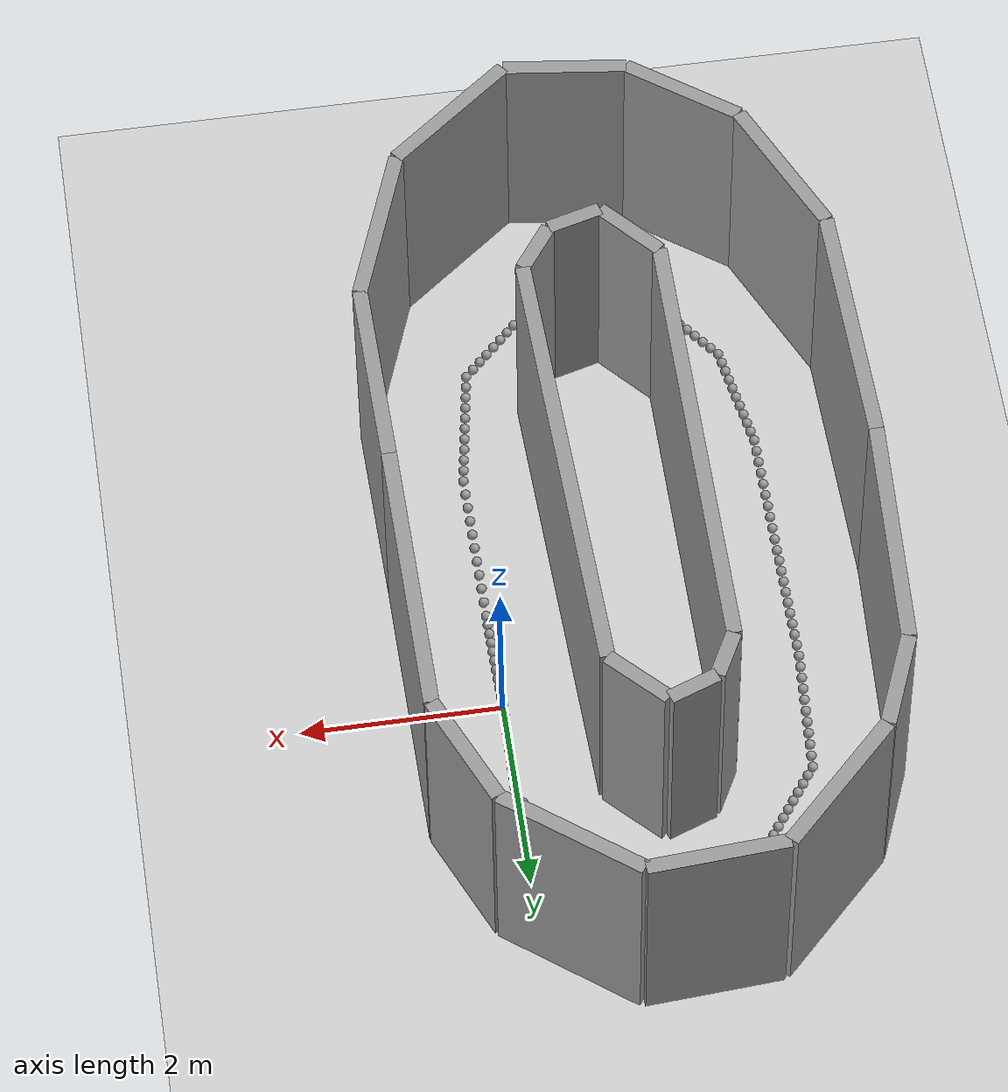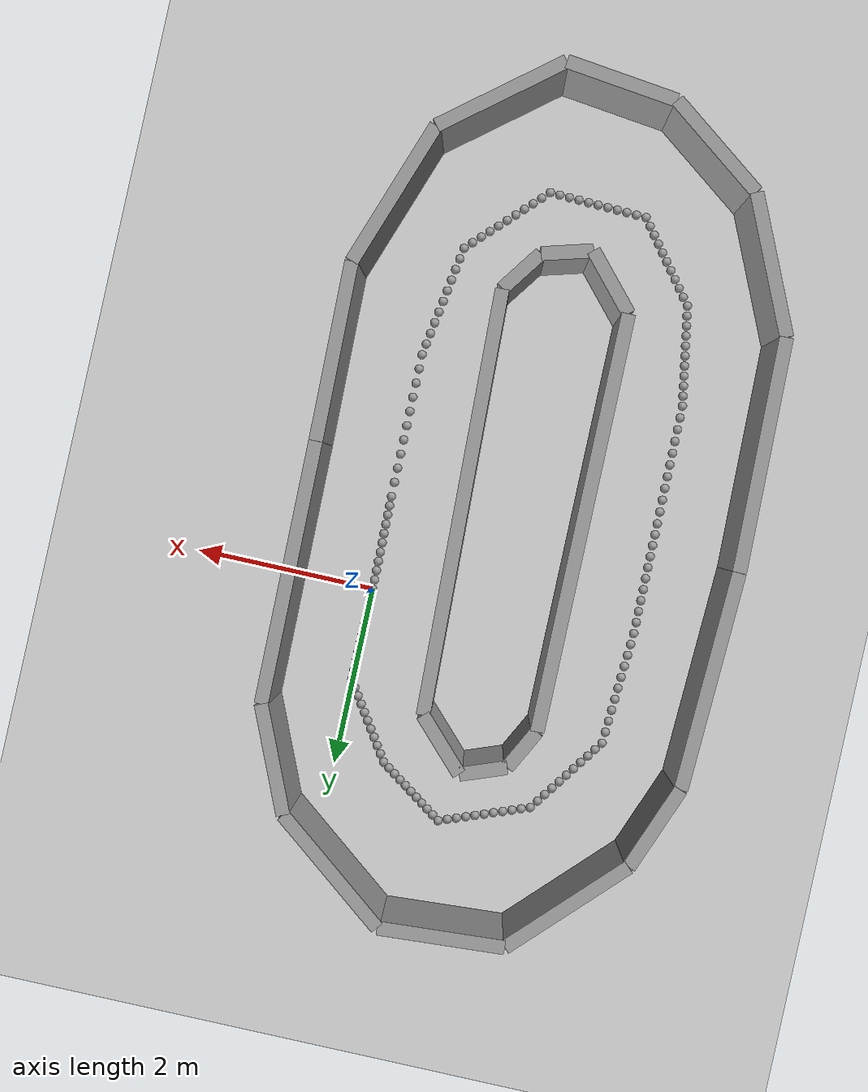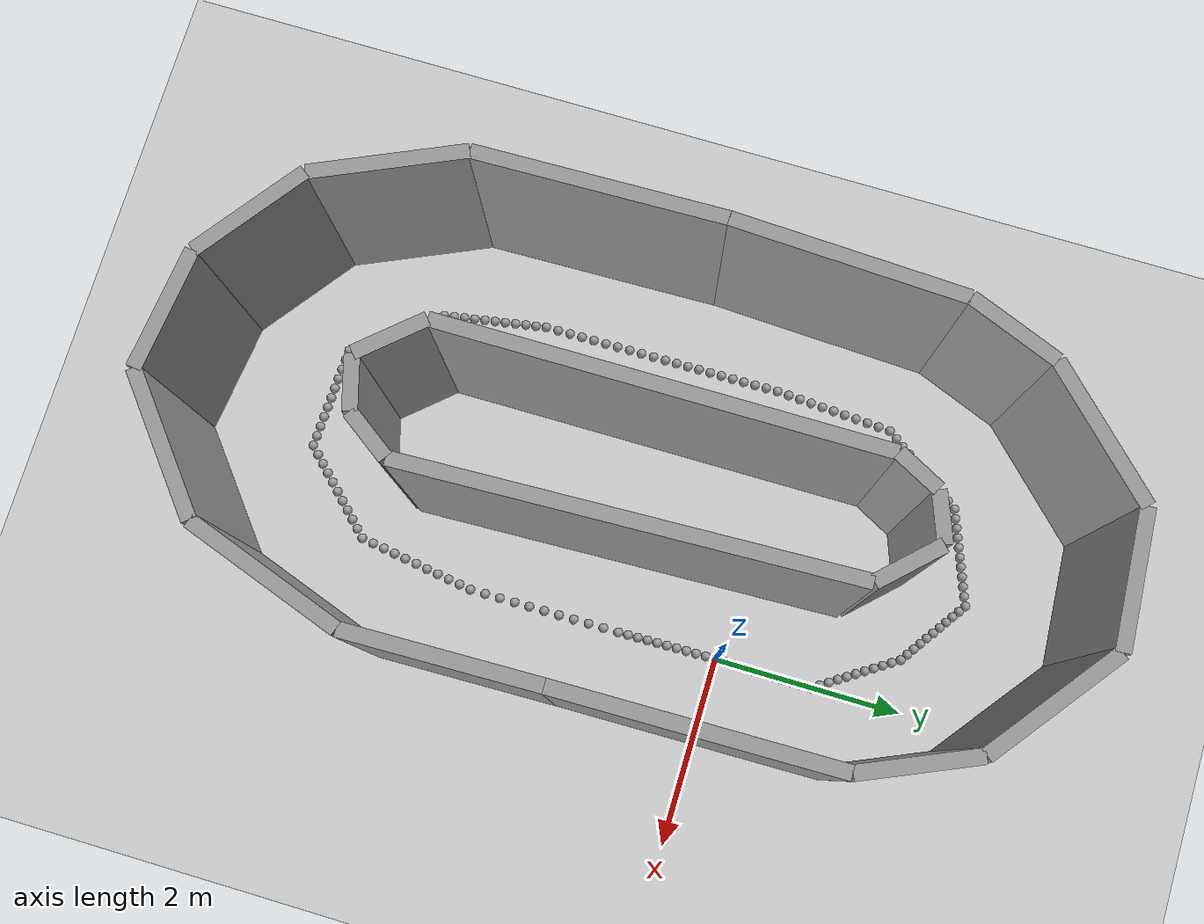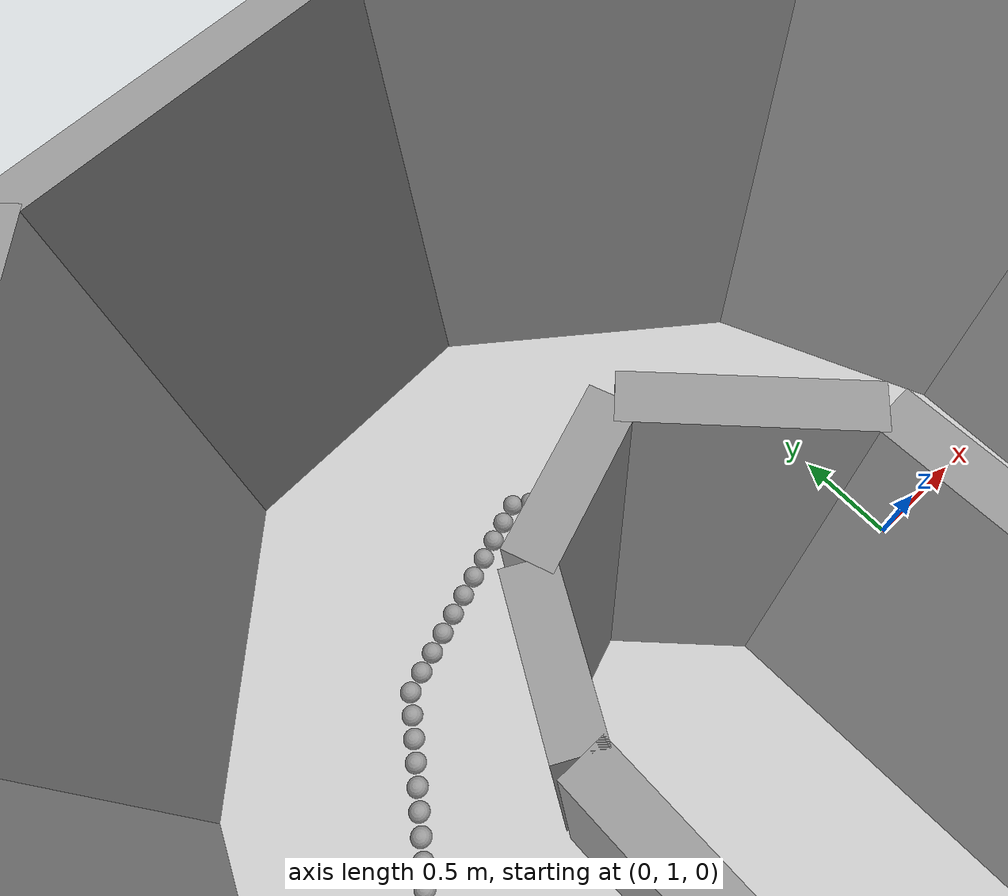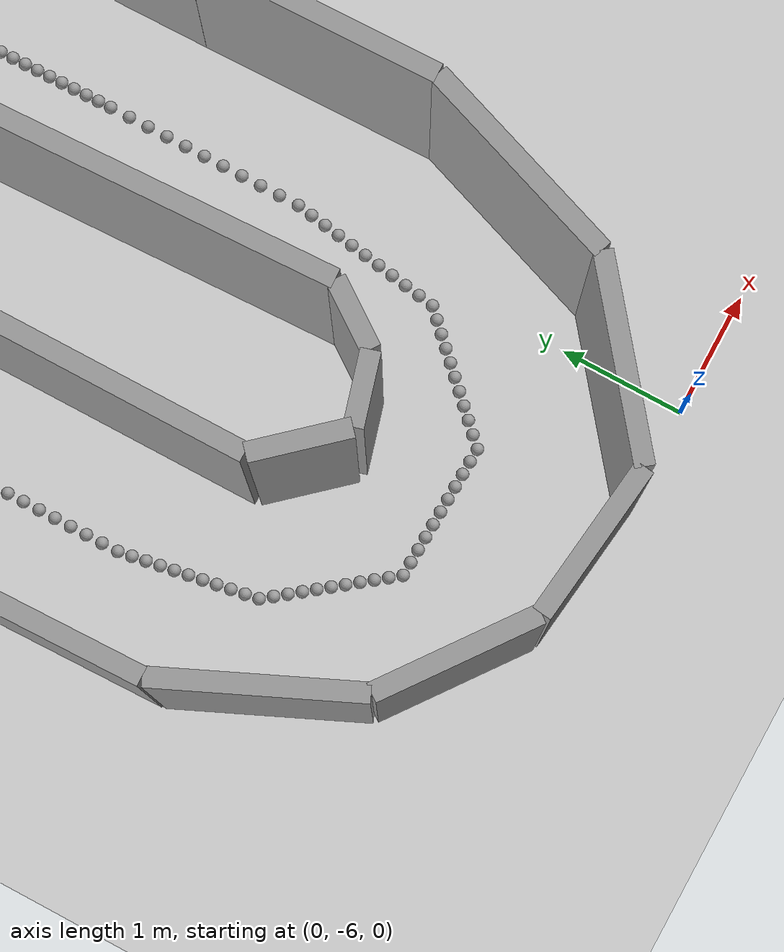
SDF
<sdf version='1.6'>
    <world name='default'>
      <light name='sun' type='directional'>
        <cast_shadows>1</cast_shadows>
        <pose frame=''>0 0 10 0 -0 0</pose>
        <diffuse>0.8 0.8 0.8 1</diffuse>
        <specular>0.2 0.2 0.2 1</specular>
        <attenuation>
          <range>1000</range>
          <constant>0.9</constant>
          <linear>0.01</linear>
          <quadratic>0.001</quadratic>
        </attenuation>
        <direction>-0.5 0.1 -0.9</direction>
      </light>
      <model name='ground_plane'>
        <static>1</static>
        <link name='link'>
          <collision name='collision'>
            <geometry>
              <plane>
                <normal>0 0 1</normal>
                <size>100 100</size>
              </plane>
            </geometry>
            <surface>
              <friction>
                <ode>
                  <mu>100</mu>
                  <mu2>50</mu2>
                </ode>
                <torsional>
                  <ode/>
                </torsional>
              </friction>
              <contact>
                <ode/>
              </contact>
              <bounce/>
            </surface>
            <max_contacts>10</max_contacts>
          </collision>
          <visual name='visual'>
            <cast_shadows>0</cast_shadows>
            <geometry>
              <plane>
                <normal>0 0 1</normal>
                <size>100 100</size>
              </plane>
            </geometry>
            <material>
              <script>
                <uri>file://media/materials/scripts/gazebo.material</uri>
                <name>Gazebo/Grey</name>
              </script>
            </material>
          </visual>
          <self_collide>0</self_collide>
          <enable_wind>0</enable_wind>
          <kinematic>0</kinematic>
        </link>
      </model>
      <gravity>0 0 -9.8</gravity>
      <magnetic_field>6e-06 2.3e-05 -4.2e-05</magnetic_field>
      <atmosphere type='adiabatic'/>
      <physics name='default_physics' default='0' type='ode'>
        <max_step_size>0.001</max_step_size>
        <real_time_factor>1</real_time_factor>
        <real_time_update_rate>1000</real_time_update_rate>
      </physics>
      <scene>
        <ambient>0.4 0.4 0.4 1</ambient>
        <background>0.7 0.7 0.7 1</background>
        <shadows>1</shadows>
      </scene>
      <wind/>
      <spherical_coordinates>
        <surface_model>EARTH_WGS84</surface_model>
        <latitude_deg>0</latitude_deg>
        <longitude_deg>0</longitude_deg>
        <elevation>0</elevation>
        <heading_deg>0</heading_deg>
      </spherical_coordinates>
      <model name='track2'>
        <pose frame=''>0 0 0 0 -0 0</pose>
        <link name='wall_000'>
                <collision name='wall_000_Collision'>
                <geometry>
                    <box>
                    <size>1.195634 0.15 2.5</size>
                    </box>
                </geometry>
                <pose frame=''>0 0 1.25 0 -0 0</pose>
                <max_contacts>10</max_contacts>
                <surface>
                    <contact>
                    <ode/>
                    </contact>
                    <bounce/>
                    <friction>
                    <torsional>
                        <ode/>
                    </torsional>
                    <ode/>
                    </friction>
                </surface>
                </collision>
                <visual name='wall_000_Visual'>
                <pose frame=''>0 0 1.25 0 -0 0</pose>
                <geometry>
                    <box>
                    <size>1.195634 0.15 2.5</size>
                    </box>
                </geometry>
                <material>
                    <script>
                    <uri>file://media/materials/scripts/gazebo.material</uri>
                    <name>Gazebo/Grey</name>
                    </script>
                    <ambient>1 1 1 1</ambient>
                </material>
                <meta>
                    <layer>0</layer>
                </meta>
                </visual>
                <pose frame=''>0.586740 1.912500 0 0 -0 -1.157576</pose>
                <self_collide>0</self_collide>
                <enable_wind>0</enable_wind>
                <kinematic>0</kinematic>
            </link>
            <link name='wall_001'>
                <collision name='wall_001_Collision'>
                <geometry>
                    <box>
                    <size>1.548632 0.15 2.5</size>
                    </box>
                </geometry>
                <pose frame=''>0 0 1.25 0 -0 0</pose>
                <max_contacts>10</max_contacts>
                <surface>
                    <contact>
                    <ode/>
                    </contact>
                    <bounce/>
                    <friction>
                    <torsional>
                        <ode/>
                    </torsional>
                    <ode/>
                    </friction>
                </surface>
                </collision>
                <visual name='wall_001_Visual'>
                <pose frame=''>0 0 1.25 0 -0 0</pose>
                <geometry>
                    <box>
                    <size>1.548632 0.15 2.5</size>
                    </box>
                </geometry>
                <material>
                    <script>
                    <uri>file://media/materials/scripts/gazebo.material</uri>
                    <name>Gazebo/Grey</name>
                    </script>
                    <ambient>1 1 1 1</ambient>
                </material>
                <meta>
                    <layer>0</layer>
                </meta>
                </visual>
                <pose frame=''>-0.266760 2.932500 0 0 -0 -0.656333</pose>
                <self_collide>0</self_collide>
                <enable_wind>0</enable_wind>
                <kinematic>0</kinematic>
            </link>
            <link name='wall_002'>
                <collision name='wall_002_Collision'>
                <geometry>
                    <box>
                    <size>1.362576 0.15 2.5</size>
                    </box>
                </geometry>
                <pose frame=''>0 0 1.25 0 -0 0</pose>
                <max_contacts>10</max_contacts>
                <surface>
                    <contact>
                    <ode/>
                    </contact>
                    <bounce/>
                    <friction>
                    <torsional>
                        <ode/>
                    </torsional>
                    <ode/>
                    </friction>
                </surface>
                </collision>
                <visual name='wall_002_Visual'>
                <pose frame=''>0 0 1.25 0 -0 0</pose>
                <geometry>
                    <box>
                    <size>1.362576 0.15 2.5</size>
                    </box>
                </geometry>
                <material>
                    <script>
                    <uri>file://media/materials/scripts/gazebo.material</uri>
                    <name>Gazebo/Grey</name>
                    </script>
                    <ambient>1 1 1 1</ambient>
                </material>
                <meta>
                    <layer>0</layer>
                </meta>
                </visual>
                <pose frame=''>-1.560000 3.360000 0 0 -0 0.066100</pose>
                <self_collide>0</self_collide>
                <enable_wind>0</enable_wind>
                <kinematic>0</kinematic>
            </link>
            <link name='wall_003'>
                <collision name='wall_003_Collision'>
                <geometry>
                    <box>
                    <size>1.558364 0.15 2.5</size>
                    </box>
                </geometry>
                <pose frame=''>0 0 1.25 0 -0 0</pose>
                <max_contacts>10</max_contacts>
                <surface>
                    <contact>
                    <ode/>
                    </contact>
                    <bounce/>
                    <friction>
                    <torsional>
                        <ode/>
                    </torsional>
                    <ode/>
                    </friction>
                </surface>
                </collision>
                <visual name='wall_003_Visual'>
                <pose frame=''>0 0 1.25 0 -0 0</pose>
                <geometry>
                    <box>
                    <size>1.558364 0.15 2.5</size>
                    </box>
                </geometry>
                <material>
                    <script>
                    <uri>file://media/materials/scripts/gazebo.material</uri>
                    <name>Gazebo/Grey</name>
                    </script>
                    <ambient>1 1 1 1</ambient>
                </material>
                <meta>
                    <layer>0</layer>
                </meta>
                </visual>
                <pose frame=''>-2.786700 2.760000 0 0 -0 0.792749</pose>
                <self_collide>0</self_collide>
                <enable_wind>0</enable_wind>
                <kinematic>0</kinematic>
            </link>
            <link name='wall_004'>
                <collision name='wall_004_Collision'>
                <geometry>
                    <box>
                    <size>0.983273 0.15 2.5</size>
                    </box>
                </geometry>
                <pose frame=''>0 0 1.25 0 -0 0</pose>
                <max_contacts>10</max_contacts>
                <surface>
                    <contact>
                    <ode/>
                    </contact>
                    <bounce/>
                    <friction>
                    <torsional>
                        <ode/>
                    </torsional>
                    <ode/>
                    </friction>
                </surface>
                </collision>
                <visual name='wall_004_Visual'>
                <pose frame=''>0 0 1.25 0 -0 0</pose>
                <geometry>
                    <box>
                    <size>0.983273 0.15 2.5</size>
                    </box>
                </geometry>
                <material>
                    <script>
                    <uri>file://media/materials/scripts/gazebo.material</uri>
                    <name>Gazebo/Grey</name>
                    </script>
                    <ambient>1 1 1 1</ambient>
                </material>
                <meta>
                    <layer>0</layer>
                </meta>
                </visual>
                <pose frame=''>-3.513600 1.747500 0 0 -0 1.195956</pose>
                <self_collide>0</self_collide>
                <enable_wind>0</enable_wind>
                <kinematic>0</kinematic>
            </link>
            <link name='wall_005'>
                <collision name='wall_005_Collision'>
                <geometry>
                    <box>
                    <size>2.372378 0.15 2.5</size>
                    </box>
                </geometry>
                <pose frame=''>0 0 1.25 0 -0 0</pose>
                <max_contacts>10</max_contacts>
                <surface>
                    <contact>
                    <ode/>
                    </contact>
                    <bounce/>
                    <friction>
                    <torsional>
                        <ode/>
                    </torsional>
                    <ode/>
                    </friction>
                </surface>
                </collision>
                <visual name='wall_005_Visual'>
                <pose frame=''>0 0 1.25 0 -0 0</pose>
                <geometry>
                    <box>
                    <size>2.372378 0.15 2.5</size>
                    </box>
                </geometry>
                <material>
                    <script>
                    <uri>file://media/materials/scripts/gazebo.material</uri>
                    <name>Gazebo/Grey</name>
                    </script>
                    <ambient>1 1 1 1</ambient>
                </material>
                <meta>
                    <layer>0</layer>
                </meta>
                </visual>
                <pose frame=''>-3.746700 0.105000 0 0 -0 1.526016</pose>
                <self_collide>0</self_collide>
                <enable_wind>0</enable_wind>
                <kinematic>0</kinematic>
            </link>
            <link name='wall_006'>
                <collision name='wall_006_Collision'>
                <geometry>
                    <box>
                    <size>2.535562 0.15 2.5</size>
                    </box>
                </geometry>
                <pose frame=''>0 0 1.25 0 -0 0</pose>
                <max_contacts>10</max_contacts>
                <surface>
                    <contact>
                    <ode/>
                    </contact>
                    <bounce/>
                    <friction>
                    <torsional>
                        <ode/>
                    </torsional>
                    <ode/>
                    </friction>
                </surface>
                </collision>
                <visual name='wall_006_Visual'>
                <pose frame=''>0 0 1.25 0 -0 0</pose>
                <geometry>
                    <box>
                    <size>2.535562 0.15 2.5</size>
                    </box>
                </geometry>
                <material>
                    <script>
                    <uri>file://media/materials/scripts/gazebo.material</uri>
                    <name>Gazebo/Grey</name>
                    </script>
                    <ambient>1 1 1 1</ambient>
                </material>
                <meta>
                    <layer>0</layer>
                </meta>
                </visual>
                <pose frame=''>-3.773100 -2.347500 0 0 -0 1.591858</pose>
                <self_collide>0</self_collide>
                <enable_wind>0</enable_wind>
                <kinematic>0</kinematic>
            </link>
            <link name='wall_007'>
                <collision name='wall_007_Collision'>
                <geometry>
                    <box>
                    <size>1.561958 0.15 2.5</size>
                    </box>
                </geometry>
                <pose frame=''>0 0 1.25 0 -0 0</pose>
                <max_contacts>10</max_contacts>
                <surface>
                    <contact>
                    <ode/>
                    </contact>
                    <bounce/>
                    <friction>
                    <torsional>
                        <ode/>
                    </torsional>
                    <ode/>
                    </friction>
                </surface>
                </collision>
                <visual name='wall_007_Visual'>
                <pose frame=''>0 0 1.25 0 -0 0</pose>
                <geometry>
                    <box>
                    <size>1.561958 0.15 2.5</size>
                    </box>
                </geometry>
                <material>
                    <script>
                    <uri>file://media/materials/scripts/gazebo.material</uri>
                    <name>Gazebo/Grey</name>
                    </script>
                    <ambient>1 1 1 1</ambient>
                </material>
                <meta>
                    <layer>0</layer>
                </meta>
                </visual>
                <pose frame=''>-3.426600 -4.327500 0 0 -0 1.992687</pose>
                <self_collide>0</self_collide>
                <enable_wind>0</enable_wind>
                <kinematic>0</kinematic>
            </link>
            <link name='wall_008'>
                <collision name='wall_008_Collision'>
                <geometry>
                    <box>
                    <size>1.280286 0.15 2.5</size>
                    </box>
                </geometry>
                <pose frame=''>0 0 1.25 0 -0 0</pose>
                <max_contacts>10</max_contacts>
                <surface>
                    <contact>
                    <ode/>
                    </contact>
                    <bounce/>
                    <friction>
                    <torsional>
                        <ode/>
                    </torsional>
                    <ode/>
                    </friction>
                </surface>
                </collision>
                <visual name='wall_008_Visual'>
                <pose frame=''>0 0 1.25 0 -0 0</pose>
                <geometry>
                    <box>
                    <size>1.280286 0.15 2.5</size>
                    </box>
                </geometry>
                <material>
                    <script>
                    <uri>file://media/materials/scripts/gazebo.material</uri>
                    <name>Gazebo/Grey</name>
                    </script>
                    <ambient>1 1 1 1</ambient>
                </material>
                <meta>
                    <layer>0</layer>
                </meta>
                </visual>
                <pose frame=''>-2.593500 -5.422500 0 0 -0 2.501185</pose>
                <self_collide>0</self_collide>
                <enable_wind>0</enable_wind>
                <kinematic>0</kinematic>
            </link>
            <link name='wall_009'>
                <collision name='wall_009_Collision'>
                <geometry>
                    <box>
                    <size>1.236135 0.15 2.5</size>
                    </box>
                </geometry>
                <pose frame=''>0 0 1.25 0 -0 0</pose>
                <max_contacts>10</max_contacts>
                <surface>
                    <contact>
                    <ode/>
                    </contact>
                    <bounce/>
                    <friction>
                    <torsional>
                        <ode/>
                    </torsional>
                    <ode/>
                    </friction>
                </surface>
                </collision>
                <visual name='wall_009_Visual'>
                <pose frame=''>0 0 1.25 0 -0 0</pose>
                <geometry>
                    <box>
                    <size>1.236135 0.15 2.5</size>
                    </box>
                </geometry>
                <material>
                    <script>
                    <uri>file://media/materials/scripts/gazebo.material</uri>
                    <name>Gazebo/Grey</name>
                    </script>
                    <ambient>1 1 1 1</ambient>
                </material>
                <meta>
                    <layer>0</layer>
                </meta>
                </visual>
                <pose frame=''>-1.466700 -5.880000 0 0 -0 3.019947</pose>
                <self_collide>0</self_collide>
                <enable_wind>0</enable_wind>
                <kinematic>0</kinematic>
            </link>
            <link name='wall_010'>
                <collision name='wall_010_Collision'>
                <geometry>
                    <box>
                    <size>1.536656 0.15 2.5</size>
                    </box>
                </geometry>
                <pose frame=''>0 0 1.25 0 -0 0</pose>
                <max_contacts>10</max_contacts>
                <surface>
                    <contact>
                    <ode/>
                    </contact>
                    <bounce/>
                    <friction>
                    <torsional>
                        <ode/>
                    </torsional>
                    <ode/>
                    </friction>
                </surface>
                </collision>
                <visual name='wall_010_Visual'>
                <pose frame=''>0 0 1.25 0 -0 0</pose>
                <geometry>
                    <box>
                    <size>1.536656 0.15 2.5</size>
                    </box>
                </geometry>
                <material>
                    <script>
                    <uri>file://media/materials/scripts/gazebo.material</uri>
                    <name>Gazebo/Grey</name>
                    </script>
                    <ambient>1 1 1 1</ambient>
                </material>
                <meta>
                    <layer>0</layer>
                </meta>
                </visual>
                <pose frame=''>-0.253260 -5.475000 0 0 -0 -2.466803</pose>
                <self_collide>0</self_collide>
                <enable_wind>0</enable_wind>
                <kinematic>0</kinematic>
            </link>
            <link name='wall_011'>
                <collision name='wall_011_Collision'>
                <geometry>
                    <box>
                    <size>1.685708 0.15 2.5</size>
                    </box>
                </geometry>
                <pose frame=''>0 0 1.25 0 -0 0</pose>
                <max_contacts>10</max_contacts>
                <surface>
                    <contact>
                    <ode/>
                    </contact>
                    <bounce/>
                    <friction>
                    <torsional>
                        <ode/>
                    </torsional>
                    <ode/>
                    </friction>
                </surface>
                </collision>
                <visual name='wall_011_Visual'>
                <pose frame=''>0 0 1.25 0 -0 0</pose>
                <geometry>
                    <box>
                    <size>1.685708 0.15 2.5</size>
                    </box>
                </geometry>
                <material>
                    <script>
                    <uri>file://media/materials/scripts/gazebo.material</uri>
                    <name>Gazebo/Grey</name>
                    </script>
                    <ambient>1 1 1 1</ambient>
                </material>
                <meta>
                    <layer>0</layer>
                </meta>
                </visual>
                <pose frame=''>0.626640 -4.200000 0 0 -0 -1.909386</pose>
                <self_collide>0</self_collide>
                <enable_wind>0</enable_wind>
                <kinematic>0</kinematic>
            </link>
            <link name='wall_012'>
                <collision name='wall_012_Collision'>
                <geometry>
                    <box>
                    <size>1.935418 0.15 2.5</size>
                    </box>
                </geometry>
                <pose frame=''>0 0 1.25 0 -0 0</pose>
                <max_contacts>10</max_contacts>
                <surface>
                    <contact>
                    <ode/>
                    </contact>
                    <bounce/>
                    <friction>
                    <torsional>
                        <ode/>
                    </torsional>
                    <ode/>
                    </friction>
                </surface>
                </collision>
                <visual name='wall_012_Visual'>
                <pose frame=''>0 0 1.25 0 -0 0</pose>
                <geometry>
                    <box>
                    <size>1.935418 0.15 2.5</size>
                    </box>
                </geometry>
                <material>
                    <script>
                    <uri>file://media/materials/scripts/gazebo.material</uri>
                    <name>Gazebo/Grey</name>
                    </script>
                    <ambient>1 1 1 1</ambient>
                </material>
                <meta>
                    <layer>0</layer>
                </meta>
                </visual>
                <pose frame=''>0.886500 -2.437500 0 0 -0 -1.550024</pose>
                <self_collide>0</self_collide>
                <enable_wind>0</enable_wind>
                <kinematic>0</kinematic>
            </link>
            <link name='wall_013'>
                <collision name='wall_013_Collision'>
                <geometry>
                    <box>
                    <size>2.835277 0.15 2.5</size>
                    </box>
                </geometry>
                <pose frame=''>0 0 1.25 0 -0 0</pose>
                <max_contacts>10</max_contacts>
                <surface>
                    <contact>
                    <ode/>
                    </contact>
                    <bounce/>
                    <friction>
                    <torsional>
                        <ode/>
                    </torsional>
                    <ode/>
                    </friction>
                </surface>
                </collision>
                <visual name='wall_013_Visual'>
                <pose frame=''>0 0 1.25 0 -0 0</pose>
                <geometry>
                    <box>
                    <size>2.835277 0.15 2.5</size>
                    </box>
                </geometry>
                <material>
                    <script>
                    <uri>file://media/materials/scripts/gazebo.material</uri>
                    <name>Gazebo/Grey</name>
                    </script>
                    <ambient>1 1 1 1</ambient>
                </material>
                <meta>
                    <layer>0</layer>
                </meta>
                </visual>
                <pose frame=''>0.846600 -0.052500 0 0 -0 -1.556829</pose>
                <self_collide>0</self_collide>
                <enable_wind>0</enable_wind>
                <kinematic>0</kinematic>
            </link>
            <link name='wall_014'>
                <collision name='wall_014_Collision'>
                <geometry>
                    <box>
                    <size>0.729845 0.15 2.5</size>
                    </box>
                </geometry>
                <pose frame=''>0 0 1.25 0 -0 0</pose>
                <max_contacts>10</max_contacts>
                <surface>
                    <contact>
                    <ode/>
                    </contact>
                    <bounce/>
                    <friction>
                    <torsional>
                        <ode/>
                    </torsional>
                    <ode/>
                    </friction>
                </surface>
                </collision>
                <visual name='wall_014_Visual'>
                <pose frame=''>0 0 1.25 0 -0 0</pose>
                <geometry>
                    <box>
                    <size>0.729845 0.15 2.5</size>
                    </box>
                </geometry>
                <material>
                    <script>
                    <uri>file://media/materials/scripts/gazebo.material</uri>
                    <name>Gazebo/Grey</name>
                    </script>
                    <ambient>1 1 1 1</ambient>
                </material>
                <meta>
                    <layer>0</layer>
                </meta>
                </visual>
                <pose frame=''>-1.119900 1.372500 0 0 -0 -0.802838</pose>
                <self_collide>0</self_collide>
                <enable_wind>0</enable_wind>
                <kinematic>0</kinematic>
            </link>
            <link name='wall_015'>
                <collision name='wall_015_Collision'>
                <geometry>
                    <box>
                    <size>0.512640 0.15 2.5</size>
                    </box>
                </geometry>
                <pose frame=''>0 0 1.25 0 -0 0</pose>
                <max_contacts>10</max_contacts>
                <surface>
                    <contact>
                    <ode/>
                    </contact>
                    <bounce/>
                    <friction>
                    <torsional>
                        <ode/>
                    </torsional>
                    <ode/>
                    </friction>
                </surface>
                </collision>
                <visual name='wall_015_Visual'>
                <pose frame=''>0 0 1.25 0 -0 0</pose>
                <geometry>
                    <box>
                    <size>0.512640 0.15 2.5</size>
                    </box>
                </geometry>
                <material>
                    <script>
                    <uri>file://media/materials/scripts/gazebo.material</uri>
                    <name>Gazebo/Grey</name>
                    </script>
                    <ambient>1 1 1 1</ambient>
                </material>
                <meta>
                    <layer>0</layer>
                </meta>
                </visual>
                <pose frame=''>-1.613400 1.545000 0 0 -0 0.358771</pose>
                <self_collide>0</self_collide>
                <enable_wind>0</enable_wind>
                <kinematic>0</kinematic>
            </link>
            <link name='wall_016'>
                <collision name='wall_016_Collision'>
                <geometry>
                    <box>
                    <size>0.490574 0.15 2.5</size>
                    </box>
                </geometry>
                <pose frame=''>0 0 1.25 0 -0 0</pose>
                <max_contacts>10</max_contacts>
                <surface>
                    <contact>
                    <ode/>
                    </contact>
                    <bounce/>
                    <friction>
                    <torsional>
                        <ode/>
                    </torsional>
                    <ode/>
                    </friction>
                </surface>
                </collision>
                <visual name='wall_016_Visual'>
                <pose frame=''>0 0 1.25 0 -0 0</pose>
                <geometry>
                    <box>
                    <size>0.490574 0.15 2.5</size>
                    </box>
                </geometry>
                <material>
                    <script>
                    <uri>file://media/materials/scripts/gazebo.material</uri>
                    <name>Gazebo/Grey</name>
                    </script>
                    <ambient>1 1 1 1</ambient>
                </material>
                <meta>
                    <layer>0</layer>
                </meta>
                </visual>
                <pose frame=''>-1.966800 1.237500 0 0 -0 1.090192</pose>
                <self_collide>0</self_collide>
                <enable_wind>0</enable_wind>
                <kinematic>0</kinematic>
            </link>
            <link name='wall_017'>
                <collision name='wall_017_Collision'>
                <geometry>
                    <box>
                    <size>4.515021 0.15 2.5</size>
                    </box>
                </geometry>
                <pose frame=''>0 0 1.25 0 -0 0</pose>
                <max_contacts>10</max_contacts>
                <surface>
                    <contact>
                    <ode/>
                    </contact>
                    <bounce/>
                    <friction>
                    <torsional>
                        <ode/>
                    </torsional>
                    <ode/>
                    </friction>
                </surface>
                </collision>
                <visual name='wall_017_Visual'>
                <pose frame=''>0 0 1.25 0 -0 0</pose>
                <geometry>
                    <box>
                    <size>4.515021 0.15 2.5</size>
                    </box>
                </geometry>
                <material>
                    <script>
                    <uri>file://media/materials/scripts/gazebo.material</uri>
                    <name>Gazebo/Grey</name>
                    </script>
                    <ambient>1 1 1 1</ambient>
                </material>
                <meta>
                    <layer>0</layer>
                </meta>
                </visual>
                <pose frame=''>-2.073300 -1.237500 0 0 -0 1.573853</pose>
                <self_collide>0</self_collide>
                <enable_wind>0</enable_wind>
                <kinematic>0</kinematic>
            </link>
            <link name='wall_018'>
                <collision name='wall_018_Collision'>
                <geometry>
                    <box>
                    <size>0.762457 0.15 2.5</size>
                    </box>
                </geometry>
                <pose frame=''>0 0 1.25 0 -0 0</pose>
                <max_contacts>10</max_contacts>
                <surface>
                    <contact>
                    <ode/>
                    </contact>
                    <bounce/>
                    <friction>
                    <torsional>
                        <ode/>
                    </torsional>
                    <ode/>
                    </friction>
                </surface>
                </collision>
                <visual name='wall_018_Visual'>
                <pose frame=''>0 0 1.25 0 -0 0</pose>
                <geometry>
                    <box>
                    <size>0.762457 0.15 2.5</size>
                    </box>
                </geometry>
                <material>
                    <script>
                    <uri>file://media/materials/scripts/gazebo.material</uri>
                    <name>Gazebo/Grey</name>
                    </script>
                    <ambient>1 1 1 1</ambient>
                </material>
                <meta>
                    <layer>0</layer>
                </meta>
                </visual>
                <pose frame=''>-1.813200 -3.780000 0 0 -0 2.297177</pose>
                <self_collide>0</self_collide>
                <enable_wind>0</enable_wind>
                <kinematic>0</kinematic>
            </link>
            <link name='wall_019'>
                <collision name='wall_019_Collision'>
                <geometry>
                    <box>
                    <size>0.554090 0.15 2.5</size>
                    </box>
                </geometry>
                <pose frame=''>0 0 1.25 0 -0 0</pose>
                <max_contacts>10</max_contacts>
                <surface>
                    <contact>
                    <ode/>
                    </contact>
                    <bounce/>
                    <friction>
                    <torsional>
                        <ode/>
                    </torsional>
                    <ode/>
                    </friction>
                </surface>
                </collision>
                <visual name='wall_019_Visual'>
                <pose frame=''>0 0 1.25 0 -0 0</pose>
                <geometry>
                    <box>
                    <size>0.554090 0.15 2.5</size>
                    </box>
                </geometry>
                <material>
                    <script>
                    <uri>file://media/materials/scripts/gazebo.material</uri>
                    <name>Gazebo/Grey</name>
                    </script>
                    <ambient>1 1 1 1</ambient>
                </material>
                <meta>
                    <layer>0</layer>
                </meta>
                </visual>
                <pose frame=''>-1.293300 -3.990000 0 0 -0 -2.867458</pose>
                <self_collide>0</self_collide>
                <enable_wind>0</enable_wind>
                <kinematic>0</kinematic>
            </link>
            <link name='wall_020'>
                <collision name='wall_020_Collision'>
                <geometry>
                    <box>
                    <size>0.552062 0.15 2.5</size>
                    </box>
                </geometry>
                <pose frame=''>0 0 1.25 0 -0 0</pose>
                <max_contacts>10</max_contacts>
                <surface>
                    <contact>
                    <ode/>
                    </contact>
                    <bounce/>
                    <friction>
                    <torsional>
                        <ode/>
                    </torsional>
                    <ode/>
                    </friction>
                </surface>
                </collision>
                <visual name='wall_020_Visual'>
                <pose frame=''>0 0 1.25 0 -0 0</pose>
                <geometry>
                    <box>
                    <size>0.552062 0.15 2.5</size>
                    </box>
                </geometry>
                <material>
                    <script>
                    <uri>file://media/materials/scripts/gazebo.material</uri>
                    <name>Gazebo/Grey</name>
                    </script>
                    <ambient>1 1 1 1</ambient>
                </material>
                <meta>
                    <layer>0</layer>
                </meta>
                </visual>
                <pose frame=''>-0.866700 -3.690000 0 0 -0 -2.188645</pose>
                <self_collide>0</self_collide>
                <enable_wind>0</enable_wind>
                <kinematic>0</kinematic>
            </link>
            <link name='wall_021'>
                <collision name='wall_021_Collision'>
                <geometry>
                    <box>
                    <size>4.577783 0.15 2.5</size>
                    </box>
                </geometry>
                <pose frame=''>0 0 1.25 0 -0 0</pose>
                <max_contacts>10</max_contacts>
                <surface>
                    <contact>
                    <ode/>
                    </contact>
                    <bounce/>
                    <friction>
                    <torsional>
                        <ode/>
                    </torsional>
                    <ode/>
                    </friction>
                </surface>
                </collision>
                <visual name='wall_021_Visual'>
                <pose frame=''>0 0 1.25 0 -0 0</pose>
                <geometry>
                    <box>
                    <size>4.577783 0.15 2.5</size>
                    </box>
                </geometry>
                <material>
                    <script>
                    <uri>file://media/materials/scripts/gazebo.material</uri>
                    <name>Gazebo/Grey</name>
                    </script>
                    <ambient>1 1 1 1</ambient>
                </material>
                <meta>
                    <layer>0</layer>
                </meta>
                </visual>
                <pose frame=''>-0.786600 -1.177500 0 0 -0 -1.535925</pose>
                <self_collide>0</self_collide>
                <enable_wind>0</enable_wind>
                <kinematic>0</kinematic>
            </link>
            <static>1</static>
      </model>
      <gui fullscreen='0'>
        <camera name='user_camera'>
          <pose frame=''>-9.88167 -5.87841 72.8661 3.14159 1.57079 3.14159</pose>
          <view_controller>orbit</view_controller>
          <projection_type>perspective</projection_type>
        </camera>
      </gui>
      <model name='unit_sphere_0_0'>
      <pose frame=''>0.000000 0.000000 0.050000 0 -0 0</pose>
      <link name='link'>
        <inertial>
          <mass>1</mass>
          <inertia>
            <ixx>0.1</ixx>
            <ixy>0</ixy>
            <ixz>0</ixz>
            <iyy>0.1</iyy>
            <iyz>0</iyz>
            <izz>0.1</izz>
          </inertia>
        </inertial>
        <collision name='collision'>
          <geometry>
            <sphere>
              <radius>0.050000</radius>
            </sphere>
          </geometry>
          <max_contacts>10</max_contacts>
          <surface>
            <contact>
              <ode/>
            </contact>
            <bounce/>
            <friction>
              <torsional>
                <ode/>
              </torsional>
              <ode/>
            </friction>
          </surface>
        </collision>
        <visual name='visual'>
          <geometry>
            <sphere>
              <radius>0.050000</radius>
            </sphere>
          </geometry>
          <material>
            <script>
              <name>Gazebo/Grey</name>
              <uri>file://media/materials/scripts/gazebo.material</uri>
            </script>
          </material>
        </visual>
        <self_collide>0</self_collide>
        <kinematic>0</kinematic>
        <gravity>1</gravity>
      </link>
    </model>
        <model name='unit_sphere_0_1'>
      <pose frame=''>0.001000 0.104000 0.050000 0 -0 0</pose>
      <link name='link'>
        <inertial>
          <mass>1</mass>
          <inertia>
            <ixx>0.1</ixx>
            <ixy>0</ixy>
            <ixz>0</ixz>
            <iyy>0.1</iyy>
            <iyz>0</iyz>
            <izz>0.1</izz>
          </inertia>
        </inertial>
        <collision name='collision'>
          <geometry>
            <sphere>
              <radius>0.050000</radius>
            </sphere>
          </geometry>
          <max_contacts>10</max_contacts>
          <surface>
            <contact>
              <ode/>
            </contact>
            <bounce/>
            <friction>
              <torsional>
                <ode/>
              </torsional>
              <ode/>
            </friction>
          </surface>
        </collision>
        <visual name='visual'>
          <geometry>
            <sphere>
              <radius>0.050000</radius>
            </sphere>
          </geometry>
          <material>
            <script>
              <name>Gazebo/Grey</name>
              <uri>file://media/materials/scripts/gazebo.material</uri>
            </script>
          </material>
        </visual>
        <self_collide>0</self_collide>
        <kinematic>0</kinematic>
        <gravity>1</gravity>
      </link>
    </model>
        <model name='unit_sphere_0_2'>
      <pose frame=''>0.002000 0.208000 0.050000 0 -0 0</pose>
      <link name='link'>
        <inertial>
          <mass>1</mass>
          <inertia>
            <ixx>0.1</ixx>
            <ixy>0</ixy>
            <ixz>0</ixz>
            <iyy>0.1</iyy>
            <iyz>0</iyz>
            <izz>0.1</izz>
          </inertia>
        </inertial>
        <collision name='collision'>
          <geometry>
            <sphere>
              <radius>0.050000</radius>
            </sphere>
          </geometry>
          <max_contacts>10</max_contacts>
          <surface>
            <contact>
              <ode/>
            </contact>
            <bounce/>
            <friction>
              <torsional>
                <ode/>
              </torsional>
              <ode/>
            </friction>
          </surface>
        </collision>
        <visual name='visual'>
          <geometry>
            <sphere>
              <radius>0.050000</radius>
            </sphere>
          </geometry>
          <material>
            <script>
              <name>Gazebo/Grey</name>
              <uri>file://media/materials/scripts/gazebo.material</uri>
            </script>
          </material>
        </visual>
        <self_collide>0</self_collide>
        <kinematic>0</kinematic>
        <gravity>1</gravity>
      </link>
    </model>
        <model name='unit_sphere_0_3'>
      <pose frame=''>0.003000 0.312000 0.050000 0 -0 0</pose>
      <link name='link'>
        <inertial>
          <mass>1</mass>
          <inertia>
            <ixx>0.1</ixx>
            <ixy>0</ixy>
            <ixz>0</ixz>
            <iyy>0.1</iyy>
            <iyz>0</iyz>
            <izz>0.1</izz>
          </inertia>
        </inertial>
        <collision name='collision'>
          <geometry>
            <sphere>
              <radius>0.050000</radius>
            </sphere>
          </geometry>
          <max_contacts>10</max_contacts>
          <surface>
            <contact>
              <ode/>
            </contact>
            <bounce/>
            <friction>
              <torsional>
                <ode/>
              </torsional>
              <ode/>
            </friction>
          </surface>
        </collision>
        <visual name='visual'>
          <geometry>
            <sphere>
              <radius>0.050000</radius>
            </sphere>
          </geometry>
          <material>
            <script>
              <name>Gazebo/Grey</name>
              <uri>file://media/materials/scripts/gazebo.material</uri>
            </script>
          </material>
        </visual>
        <self_collide>0</self_collide>
        <kinematic>0</kinematic>
        <gravity>1</gravity>
      </link>
    </model>
        <model name='unit_sphere_0_4'>
      <pose frame=''>0.004000 0.416000 0.050000 0 -0 0</pose>
      <link name='link'>
        <inertial>
          <mass>1</mass>
          <inertia>
            <ixx>0.1</ixx>
            <ixy>0</ixy>
            <ixz>0</ixz>
            <iyy>0.1</iyy>
            <iyz>0</iyz>
            <izz>0.1</izz>
          </inertia>
        </inertial>
        <collision name='collision'>
          <geometry>
            <sphere>
              <radius>0.050000</radius>
            </sphere>
          </geometry>
          <max_contacts>10</max_contacts>
          <surface>
            <contact>
              <ode/>
            </contact>
            <bounce/>
            <friction>
              <torsional>
                <ode/>
              </torsional>
              <ode/>
            </friction>
          </surface>
        </collision>
        <visual name='visual'>
          <geometry>
            <sphere>
              <radius>0.050000</radius>
            </sphere>
          </geometry>
          <material>
            <script>
              <name>Gazebo/Grey</name>
              <uri>file://media/materials/scripts/gazebo.material</uri>
            </script>
          </material>
        </visual>
        <self_collide>0</self_collide>
        <kinematic>0</kinematic>
        <gravity>1</gravity>
      </link>
    </model>
        <model name='unit_sphere_0_5'>
      <pose frame=''>0.005000 0.520000 0.050000 0 -0 0</pose>
      <link name='link'>
        <inertial>
          <mass>1</mass>
          <inertia>
            <ixx>0.1</ixx>
            <ixy>0</ixy>
            <ixz>0</ixz>
            <iyy>0.1</iyy>
            <iyz>0</iyz>
            <izz>0.1</izz>
          </inertia>
        </inertial>
        <collision name='collision'>
          <geometry>
            <sphere>
              <radius>0.050000</radius>
            </sphere>
          </geometry>
          <max_contacts>10</max_contacts>
          <surface>
            <contact>
              <ode/>
            </contact>
            <bounce/>
            <friction>
              <torsional>
                <ode/>
              </torsional>
              <ode/>
            </friction>
          </surface>
        </collision>
        <visual name='visual'>
          <geometry>
            <sphere>
              <radius>0.050000</radius>
            </sphere>
          </geometry>
          <material>
            <script>
              <name>Gazebo/Grey</name>
              <uri>file://media/materials/scripts/gazebo.material</uri>
            </script>
          </material>
        </visual>
        <self_collide>0</self_collide>
        <kinematic>0</kinematic>
        <gravity>1</gravity>
      </link>
    </model>
        <model name='unit_sphere_0_6'>
      <pose frame=''>0.006000 0.624000 0.050000 0 -0 0</pose>
      <link name='link'>
        <inertial>
          <mass>1</mass>
          <inertia>
            <ixx>0.1</ixx>
            <ixy>0</ixy>
            <ixz>0</ixz>
            <iyy>0.1</iyy>
            <iyz>0</iyz>
            <izz>0.1</izz>
          </inertia>
        </inertial>
        <collision name='collision'>
          <geometry>
            <sphere>
              <radius>0.050000</radius>
            </sphere>
          </geometry>
          <max_contacts>10</max_contacts>
          <surface>
            <contact>
              <ode/>
            </contact>
            <bounce/>
            <friction>
              <torsional>
                <ode/>
              </torsional>
              <ode/>
            </friction>
          </surface>
        </collision>
        <visual name='visual'>
          <geometry>
            <sphere>
              <radius>0.050000</radius>
            </sphere>
          </geometry>
          <material>
            <script>
              <name>Gazebo/Grey</name>
              <uri>file://media/materials/scripts/gazebo.material</uri>
            </script>
          </material>
        </visual>
        <self_collide>0</self_collide>
        <kinematic>0</kinematic>
        <gravity>1</gravity>
      </link>
    </model>
        <model name='unit_sphere_0_7'>
      <pose frame=''>0.007000 0.728000 0.050000 0 -0 0</pose>
      <link name='link'>
        <inertial>
          <mass>1</mass>
          <inertia>
            <ixx>0.1</ixx>
            <ixy>0</ixy>
            <ixz>0</ixz>
            <iyy>0.1</iyy>
            <iyz>0</iyz>
            <izz>0.1</izz>
          </inertia>
        </inertial>
        <collision name='collision'>
          <geometry>
            <sphere>
              <radius>0.050000</radius>
            </sphere>
          </geometry>
          <max_contacts>10</max_contacts>
          <surface>
            <contact>
              <ode/>
            </contact>
            <bounce/>
            <friction>
              <torsional>
                <ode/>
              </torsional>
              <ode/>
            </friction>
          </surface>
        </collision>
        <visual name='visual'>
          <geometry>
            <sphere>
              <radius>0.050000</radius>
            </sphere>
          </geometry>
          <material>
            <script>
              <name>Gazebo/Grey</name>
              <uri>file://media/materials/scripts/gazebo.material</uri>
            </script>
          </material>
        </visual>
        <self_collide>0</self_collide>
        <kinematic>0</kinematic>
        <gravity>1</gravity>
      </link>
    </model>
        <model name='unit_sphere_0_8'>
      <pose frame=''>0.008000 0.832000 0.050000 0 -0 0</pose>
      <link name='link'>
        <inertial>
          <mass>1</mass>
          <inertia>
            <ixx>0.1</ixx>
            <ixy>0</ixy>
            <ixz>0</ixz>
            <iyy>0.1</iyy>
            <iyz>0</iyz>
            <izz>0.1</izz>
          </inertia>
        </inertial>
        <collision name='collision'>
          <geometry>
            <sphere>
              <radius>0.050000</radius>
            </sphere>
          </geometry>
          <max_contacts>10</max_contacts>
          <surface>
            <contact>
              <ode/>
            </contact>
            <bounce/>
            <friction>
              <torsional>
                <ode/>
              </torsional>
              <ode/>
            </friction>
          </surface>
        </collision>
        <visual name='visual'>
          <geometry>
            <sphere>
              <radius>0.050000</radius>
            </sphere>
          </geometry>
          <material>
            <script>
              <name>Gazebo/Grey</name>
              <uri>file://media/materials/scripts/gazebo.material</uri>
            </script>
          </material>
        </visual>
        <self_collide>0</self_collide>
        <kinematic>0</kinematic>
        <gravity>1</gravity>
      </link>
    </model>
        <model name='unit_sphere_0_9'>
      <pose frame=''>0.009000 0.936000 0.050000 0 -0 0</pose>
      <link name='link'>
        <inertial>
          <mass>1</mass>
          <inertia>
            <ixx>0.1</ixx>
            <ixy>0</ixy>
            <ixz>0</ixz>
            <iyy>0.1</iyy>
            <iyz>0</iyz>
            <izz>0.1</izz>
          </inertia>
        </inertial>
        <collision name='collision'>
          <geometry>
            <sphere>
              <radius>0.050000</radius>
            </sphere>
          </geometry>
          <max_contacts>10</max_contacts>
          <surface>
            <contact>
              <ode/>
            </contact>
            <bounce/>
            <friction>
              <torsional>
                <ode/>
              </torsional>
              <ode/>
            </friction>
          </surface>
        </collision>
        <visual name='visual'>
          <geometry>
            <sphere>
              <radius>0.050000</radius>
            </sphere>
          </geometry>
          <material>
            <script>
              <name>Gazebo/Grey</name>
              <uri>file://media/materials/scripts/gazebo.material</uri>
            </script>
          </material>
        </visual>
        <self_collide>0</self_collide>
        <kinematic>0</kinematic>
        <gravity>1</gravity>
      </link>
    </model>
        <model name='unit_sphere_0_10'>
      <pose frame=''>0.010000 1.040000 0.050000 0 -0 0</pose>
      <link name='link'>
        <inertial>
          <mass>1</mass>
          <inertia>
            <ixx>0.1</ixx>
            <ixy>0</ixy>
            <ixz>0</ixz>
            <iyy>0.1</iyy>
            <iyz>0</iyz>
            <izz>0.1</izz>
          </inertia>
        </inertial>
        <collision name='collision'>
          <geometry>
            <sphere>
              <radius>0.050000</radius>
            </sphere>
          </geometry>
          <max_contacts>10</max_contacts>
          <surface>
            <contact>
              <ode/>
            </contact>
            <bounce/>
            <friction>
              <torsional>
                <ode/>
              </torsional>
              <ode/>
            </friction>
          </surface>
        </collision>
        <visual name='visual'>
          <geometry>
            <sphere>
              <radius>0.050000</radius>
            </sphere>
          </geometry>
          <material>
            <script>
              <name>Gazebo/Grey</name>
              <uri>file://media/materials/scripts/gazebo.material</uri>
            </script>
          </material>
        </visual>
        <self_collide>0</self_collide>
        <kinematic>0</kinematic>
        <gravity>1</gravity>
      </link>
    </model>
        <model name='unit_sphere_0_11'>
      <pose frame=''>-0.045000 1.123000 0.050000 0 -0 0</pose>
      <link name='link'>
        <inertial>
          <mass>1</mass>
          <inertia>
            <ixx>0.1</ixx>
            <ixy>0</ixy>
            <ixz>0</ixz>
            <iyy>0.1</iyy>
            <iyz>0</iyz>
            <izz>0.1</izz>
          </inertia>
        </inertial>
        <collision name='collision'>
          <geometry>
            <sphere>
              <radius>0.050000</radius>
            </sphere>
          </geometry>
          <max_contacts>10</max_contacts>
          <surface>
            <contact>
              <ode/>
            </contact>
            <bounce/>
            <friction>
              <torsional>
                <ode/>
              </torsional>
              <ode/>
            </friction>
          </surface>
        </collision>
        <visual name='visual'>
          <geometry>
            <sphere>
              <radius>0.050000</radius>
            </sphere>
          </geometry>
          <material>
            <script>
              <name>Gazebo/Grey</name>
              <uri>file://media/materials/scripts/gazebo.material</uri>
            </script>
          </material>
        </visual>
        <self_collide>0</self_collide>
        <kinematic>0</kinematic>
        <gravity>1</gravity>
      </link>
    </model>
        <model name='unit_sphere_0_12'>
      <pose frame=''>-0.100000 1.206000 0.050000 0 -0 0</pose>
      <link name='link'>
        <inertial>
          <mass>1</mass>
          <inertia>
            <ixx>0.1</ixx>
            <ixy>0</ixy>
            <ixz>0</ixz>
            <iyy>0.1</iyy>
            <iyz>0</iyz>
            <izz>0.1</izz>
          </inertia>
        </inertial>
        <collision name='collision'>
          <geometry>
            <sphere>
              <radius>0.050000</radius>
            </sphere>
          </geometry>
          <max_contacts>10</max_contacts>
          <surface>
            <contact>
              <ode/>
            </contact>
            <bounce/>
            <friction>
              <torsional>
                <ode/>
              </torsional>
              <ode/>
            </friction>
          </surface>
        </collision>
        <visual name='visual'>
          <geometry>
            <sphere>
              <radius>0.050000</radius>
            </sphere>
          </geometry>
          <material>
            <script>
              <name>Gazebo/Grey</name>
              <uri>file://media/materials/scripts/gazebo.material</uri>
            </script>
          </material>
        </visual>
        <self_collide>0</self_collide>
        <kinematic>0</kinematic>
        <gravity>1</gravity>
      </link>
    </model>
        <model name='unit_sphere_0_13'>
      <pose frame=''>-0.155000 1.289000 0.050000 0 -0 0</pose>
      <link name='link'>
        <inertial>
          <mass>1</mass>
          <inertia>
            <ixx>0.1</ixx>
            <ixy>0</ixy>
            <ixz>0</ixz>
            <iyy>0.1</iyy>
            <iyz>0</iyz>
            <izz>0.1</izz>
          </inertia>
        </inertial>
        <collision name='collision'>
          <geometry>
            <sphere>
              <radius>0.050000</radius>
            </sphere>
          </geometry>
          <max_contacts>10</max_contacts>
          <surface>
            <contact>
              <ode/>
            </contact>
            <bounce/>
            <friction>
              <torsional>
                <ode/>
              </torsional>
              <ode/>
            </friction>
          </surface>
        </collision>
        <visual name='visual'>
          <geometry>
            <sphere>
              <radius>0.050000</radius>
            </sphere>
          </geometry>
          <material>
            <script>
              <name>Gazebo/Grey</name>
              <uri>file://media/materials/scripts/gazebo.material</uri>
            </script>
          </material>
        </visual>
        <self_collide>0</self_collide>
        <kinematic>0</kinematic>
        <gravity>1</gravity>
      </link>
    </model>
        <model name='unit_sphere_0_14'>
      <pose frame=''>-0.210000 1.372000 0.050000 0 -0 0</pose>
      <link name='link'>
        <inertial>
          <mass>1</mass>
          <inertia>
            <ixx>0.1</ixx>
            <ixy>0</ixy>
            <ixz>0</ixz>
            <iyy>0.1</iyy>
            <iyz>0</iyz>
            <izz>0.1</izz>
          </inertia>
        </inertial>
        <collision name='collision'>
          <geometry>
            <sphere>
              <radius>0.050000</radius>
            </sphere>
          </geometry>
          <max_contacts>10</max_contacts>
          <surface>
            <contact>
              <ode/>
            </contact>
            <bounce/>
            <friction>
              <torsional>
                <ode/>
              </torsional>
              <ode/>
            </friction>
          </surface>
        </collision>
        <visual name='visual'>
          <geometry>
            <sphere>
              <radius>0.050000</radius>
            </sphere>
          </geometry>
          <material>
            <script>
              <name>Gazebo/Grey</name>
              <uri>file://media/materials/scripts/gazebo.material</uri>
            </script>
          </material>
        </visual>
        <self_collide>0</self_collide>
        <kinematic>0</kinematic>
        <gravity>1</gravity>
      </link>
    </model>
        <model name='unit_sphere_0_15'>
      <pose frame=''>-0.265000 1.455000 0.050000 0 -0 0</pose>
      <link name='link'>
        <inertial>
          <mass>1</mass>
          <inertia>
            <ixx>0.1</ixx>
            <ixy>0</ixy>
            <ixz>0</ixz>
            <iyy>0.1</iyy>
            <iyz>0</iyz>
            <izz>0.1</izz>
          </inertia>
        </inertial>
        <collision name='collision'>
          <geometry>
            <sphere>
              <radius>0.050000</radius>
            </sphere>
          </geometry>
          <max_contacts>10</max_contacts>
          <surface>
            <contact>
              <ode/>
            </contact>
            <bounce/>
            <friction>
              <torsional>
                <ode/>
              </torsional>
              <ode/>
            </friction>
          </surface>
        </collision>
        <visual name='visual'>
          <geometry>
            <sphere>
              <radius>0.050000</radius>
            </sphere>
          </geometry>
          <material>
            <script>
              <name>Gazebo/Grey</name>
              <uri>file://media/materials/scripts/gazebo.material</uri>
            </script>
          </material>
        </visual>
        <self_collide>0</self_collide>
        <kinematic>0</kinematic>
        <gravity>1</gravity>
      </link>
    </model>
        <model name='unit_sphere_0_16'>
      <pose frame=''>-0.320000 1.538000 0.050000 0 -0 0</pose>
      <link name='link'>
        <inertial>
          <mass>1</mass>
          <inertia>
            <ixx>0.1</ixx>
            <ixy>0</ixy>
            <ixz>0</ixz>
            <iyy>0.1</iyy>
            <iyz>0</iyz>
            <izz>0.1</izz>
          </inertia>
        </inertial>
        <collision name='collision'>
          <geometry>
            <sphere>
              <radius>0.050000</radius>
            </sphere>
          </geometry>
          <max_contacts>10</max_contacts>
          <surface>
            <contact>
              <ode/>
            </contact>
            <bounce/>
            <friction>
              <torsional>
                <ode/>
              </torsional>
              <ode/>
            </friction>
          </surface>
        </collision>
        <visual name='visual'>
          <geometry>
            <sphere>
              <radius>0.050000</radius>
            </sphere>
          </geometry>
          <material>
            <script>
              <name>Gazebo/Grey</name>
              <uri>file://media/materials/scripts/gazebo.material</uri>
            </script>
          </material>
        </visual>
        <self_collide>0</self_collide>
        <kinematic>0</kinematic>
        <gravity>1</gravity>
      </link>
    </model>
        <model name='unit_sphere_0_17'>
      <pose frame=''>-0.375000 1.621000 0.050000 0 -0 0</pose>
      <link name='link'>
        <inertial>
          <mass>1</mass>
          <inertia>
            <ixx>0.1</ixx>
            <ixy>0</ixy>
            <ixz>0</ixz>
            <iyy>0.1</iyy>
            <iyz>0</iyz>
            <izz>0.1</izz>
          </inertia>
        </inertial>
        <collision name='collision'>
          <geometry>
            <sphere>
              <radius>0.050000</radius>
            </sphere>
          </geometry>
          <max_contacts>10</max_contacts>
          <surface>
            <contact>
              <ode/>
            </contact>
            <bounce/>
            <friction>
              <torsional>
                <ode/>
              </torsional>
              <ode/>
            </friction>
          </surface>
        </collision>
        <visual name='visual'>
          <geometry>
            <sphere>
              <radius>0.050000</radius>
            </sphere>
          </geometry>
          <material>
            <script>
              <name>Gazebo/Grey</name>
              <uri>file://media/materials/scripts/gazebo.material</uri>
            </script>
          </material>
        </visual>
        <self_collide>0</self_collide>
        <kinematic>0</kinematic>
        <gravity>1</gravity>
      </link>
    </model>
        <model name='unit_sphere_0_18'>
      <pose frame=''>-0.430000 1.704000 0.050000 0 -0 0</pose>
      <link name='link'>
        <inertial>
          <mass>1</mass>
          <inertia>
            <ixx>0.1</ixx>
            <ixy>0</ixy>
            <ixz>0</ixz>
            <iyy>0.1</iyy>
            <iyz>0</iyz>
            <izz>0.1</izz>
          </inertia>
        </inertial>
        <collision name='collision'>
          <geometry>
            <sphere>
              <radius>0.050000</radius>
            </sphere>
          </geometry>
          <max_contacts>10</max_contacts>
          <surface>
            <contact>
              <ode/>
            </contact>
            <bounce/>
            <friction>
              <torsional>
                <ode/>
              </torsional>
              <ode/>
            </friction>
          </surface>
        </collision>
        <visual name='visual'>
          <geometry>
            <sphere>
              <radius>0.050000</radius>
            </sphere>
          </geometry>
          <material>
            <script>
              <name>Gazebo/Grey</name>
              <uri>file://media/materials/scripts/gazebo.material</uri>
            </script>
          </material>
        </visual>
        <self_collide>0</self_collide>
        <kinematic>0</kinematic>
        <gravity>1</gravity>
      </link>
    </model>
        <model name='unit_sphere_0_19'>
      <pose frame=''>-0.485000 1.787000 0.050000 0 -0 0</pose>
      <link name='link'>
        <inertial>
          <mass>1</mass>
          <inertia>
            <ixx>0.1</ixx>
            <ixy>0</ixy>
            <ixz>0</ixz>
            <iyy>0.1</iyy>
            <iyz>0</iyz>
            <izz>0.1</izz>
          </inertia>
        </inertial>
        <collision name='collision'>
          <geometry>
            <sphere>
              <radius>0.050000</radius>
            </sphere>
          </geometry>
          <max_contacts>10</max_contacts>
          <surface>
            <contact>
              <ode/>
            </contact>
            <bounce/>
            <friction>
              <torsional>
                <ode/>
              </torsional>
              <ode/>
            </friction>
          </surface>
        </collision>
        <visual name='visual'>
          <geometry>
            <sphere>
              <radius>0.050000</radius>
            </sphere>
          </geometry>
          <material>
            <script>
              <name>Gazebo/Grey</name>
              <uri>file://media/materials/scripts/gazebo.material</uri>
            </script>
          </material>
        </visual>
        <self_collide>0</self_collide>
        <kinematic>0</kinematic>
        <gravity>1</gravity>
      </link>
    </model>
        <model name='unit_sphere_0_20'>
      <pose frame=''>-0.540000 1.870000 0.050000 0 -0 0</pose>
      <link name='link'>
        <inertial>
          <mass>1</mass>
          <inertia>
            <ixx>0.1</ixx>
            <ixy>0</ixy>
            <ixz>0</ixz>
            <iyy>0.1</iyy>
            <iyz>0</iyz>
            <izz>0.1</izz>
          </inertia>
        </inertial>
        <collision name='collision'>
          <geometry>
            <sphere>
              <radius>0.050000</radius>
            </sphere>
          </geometry>
          <max_contacts>10</max_contacts>
          <surface>
            <contact>
              <ode/>
            </contact>
            <bounce/>
            <friction>
              <torsional>
                <ode/>
              </torsional>
              <ode/>
            </friction>
          </surface>
        </collision>
        <visual name='visual'>
          <geometry>
            <sphere>
              <radius>0.050000</radius>
            </sphere>
          </geometry>
          <material>
            <script>
              <name>Gazebo/Grey</name>
              <uri>file://media/materials/scripts/gazebo.material</uri>
            </script>
          </material>
        </visual>
        <self_collide>0</self_collide>
        <kinematic>0</kinematic>
        <gravity>1</gravity>
      </link>
    </model>
        <model name='unit_sphere_0_21'>
      <pose frame=''>-0.614000 1.921000 0.050000 0 -0 0</pose>
      <link name='link'>
        <inertial>
          <mass>1</mass>
          <inertia>
            <ixx>0.1</ixx>
            <ixy>0</ixy>
            <ixz>0</ixz>
            <iyy>0.1</iyy>
            <iyz>0</iyz>
            <izz>0.1</izz>
          </inertia>
        </inertial>
        <collision name='collision'>
          <geometry>
            <sphere>
              <radius>0.050000</radius>
            </sphere>
          </geometry>
          <max_contacts>10</max_contacts>
          <surface>
            <contact>
              <ode/>
            </contact>
            <bounce/>
            <friction>
              <torsional>
                <ode/>
              </torsional>
              <ode/>
            </friction>
          </surface>
        </collision>
        <visual name='visual'>
          <geometry>
            <sphere>
              <radius>0.050000</radius>
            </sphere>
          </geometry>
          <material>
            <script>
              <name>Gazebo/Grey</name>
              <uri>file://media/materials/scripts/gazebo.material</uri>
            </script>
          </material>
        </visual>
        <self_collide>0</self_collide>
        <kinematic>0</kinematic>
        <gravity>1</gravity>
      </link>
    </model>
        <model name='unit_sphere_0_22'>
      <pose frame=''>-0.688000 1.972000 0.050000 0 -0 0</pose>
      <link name='link'>
        <inertial>
          <mass>1</mass>
          <inertia>
            <ixx>0.1</ixx>
            <ixy>0</ixy>
            <ixz>0</ixz>
            <iyy>0.1</iyy>
            <iyz>0</iyz>
            <izz>0.1</izz>
          </inertia>
        </inertial>
        <collision name='collision'>
          <geometry>
            <sphere>
              <radius>0.050000</radius>
            </sphere>
          </geometry>
          <max_contacts>10</max_contacts>
          <surface>
            <contact>
              <ode/>
            </contact>
            <bounce/>
            <friction>
              <torsional>
                <ode/>
              </torsional>
              <ode/>
            </friction>
          </surface>
        </collision>
        <visual name='visual'>
          <geometry>
            <sphere>
              <radius>0.050000</radius>
            </sphere>
          </geometry>
          <material>
            <script>
              <name>Gazebo/Grey</name>
              <uri>file://media/materials/scripts/gazebo.material</uri>
            </script>
          </material>
        </visual>
        <self_collide>0</self_collide>
        <kinematic>0</kinematic>
        <gravity>1</gravity>
      </link>
    </model>
        <model name='unit_sphere_0_23'>
      <pose frame=''>-0.762000 2.023000 0.050000 0 -0 0</pose>
      <link name='link'>
        <inertial>
          <mass>1</mass>
          <inertia>
            <ixx>0.1</ixx>
            <ixy>0</ixy>
            <ixz>0</ixz>
            <iyy>0.1</iyy>
            <iyz>0</iyz>
            <izz>0.1</izz>
          </inertia>
        </inertial>
        <collision name='collision'>
          <geometry>
            <sphere>
              <radius>0.050000</radius>
            </sphere>
          </geometry>
          <max_contacts>10</max_contacts>
          <surface>
            <contact>
              <ode/>
            </contact>
            <bounce/>
            <friction>
              <torsional>
                <ode/>
              </torsional>
              <ode/>
            </friction>
          </surface>
        </collision>
        <visual name='visual'>
          <geometry>
            <sphere>
              <radius>0.050000</radius>
            </sphere>
          </geometry>
          <material>
            <script>
              <name>Gazebo/Grey</name>
              <uri>file://media/materials/scripts/gazebo.material</uri>
            </script>
          </material>
        </visual>
        <self_collide>0</self_collide>
        <kinematic>0</kinematic>
        <gravity>1</gravity>
      </link>
    </model>
        <model name='unit_sphere_0_24'>
      <pose frame=''>-0.836000 2.074000 0.050000 0 -0 0</pose>
      <link name='link'>
        <inertial>
          <mass>1</mass>
          <inertia>
            <ixx>0.1</ixx>
            <ixy>0</ixy>
            <ixz>0</ixz>
            <iyy>0.1</iyy>
            <iyz>0</iyz>
            <izz>0.1</izz>
          </inertia>
        </inertial>
        <collision name='collision'>
          <geometry>
            <sphere>
              <radius>0.050000</radius>
            </sphere>
          </geometry>
          <max_contacts>10</max_contacts>
          <surface>
            <contact>
              <ode/>
            </contact>
            <bounce/>
            <friction>
              <torsional>
                <ode/>
              </torsional>
              <ode/>
            </friction>
          </surface>
        </collision>
        <visual name='visual'>
          <geometry>
            <sphere>
              <radius>0.050000</radius>
            </sphere>
          </geometry>
          <material>
            <script>
              <name>Gazebo/Grey</name>
              <uri>file://media/materials/scripts/gazebo.material</uri>
            </script>
          </material>
        </visual>
        <self_collide>0</self_collide>
        <kinematic>0</kinematic>
        <gravity>1</gravity>
      </link>
    </model>
        <model name='unit_sphere_0_25'>
      <pose frame=''>-0.910000 2.125000 0.050000 0 -0 0</pose>
      <link name='link'>
        <inertial>
          <mass>1</mass>
          <inertia>
            <ixx>0.1</ixx>
            <ixy>0</ixy>
            <ixz>0</ixz>
            <iyy>0.1</iyy>
            <iyz>0</iyz>
            <izz>0.1</izz>
          </inertia>
        </inertial>
        <collision name='collision'>
          <geometry>
            <sphere>
              <radius>0.050000</radius>
            </sphere>
          </geometry>
          <max_contacts>10</max_contacts>
          <surface>
            <contact>
              <ode/>
            </contact>
            <bounce/>
            <friction>
              <torsional>
                <ode/>
              </torsional>
              <ode/>
            </friction>
          </surface>
        </collision>
        <visual name='visual'>
          <geometry>
            <sphere>
              <radius>0.050000</radius>
            </sphere>
          </geometry>
          <material>
            <script>
              <name>Gazebo/Grey</name>
              <uri>file://media/materials/scripts/gazebo.material</uri>
            </script>
          </material>
        </visual>
        <self_collide>0</self_collide>
        <kinematic>0</kinematic>
        <gravity>1</gravity>
      </link>
    </model>
        <model name='unit_sphere_0_26'>
      <pose frame=''>-0.984000 2.176000 0.050000 0 -0 0</pose>
      <link name='link'>
        <inertial>
          <mass>1</mass>
          <inertia>
            <ixx>0.1</ixx>
            <ixy>0</ixy>
            <ixz>0</ixz>
            <iyy>0.1</iyy>
            <iyz>0</iyz>
            <izz>0.1</izz>
          </inertia>
        </inertial>
        <collision name='collision'>
          <geometry>
            <sphere>
              <radius>0.050000</radius>
            </sphere>
          </geometry>
          <max_contacts>10</max_contacts>
          <surface>
            <contact>
              <ode/>
            </contact>
            <bounce/>
            <friction>
              <torsional>
                <ode/>
              </torsional>
              <ode/>
            </friction>
          </surface>
        </collision>
        <visual name='visual'>
          <geometry>
            <sphere>
              <radius>0.050000</radius>
            </sphere>
          </geometry>
          <material>
            <script>
              <name>Gazebo/Grey</name>
              <uri>file://media/materials/scripts/gazebo.material</uri>
            </script>
          </material>
        </visual>
        <self_collide>0</self_collide>
        <kinematic>0</kinematic>
        <gravity>1</gravity>
      </link>
    </model>
        <model name='unit_sphere_0_27'>
      <pose frame=''>-1.058000 2.227000 0.050000 0 -0 0</pose>
      <link name='link'>
        <inertial>
          <mass>1</mass>
          <inertia>
            <ixx>0.1</ixx>
            <ixy>0</ixy>
            <ixz>0</ixz>
            <iyy>0.1</iyy>
            <iyz>0</iyz>
            <izz>0.1</izz>
          </inertia>
        </inertial>
        <collision name='collision'>
          <geometry>
            <sphere>
              <radius>0.050000</radius>
            </sphere>
          </geometry>
          <max_contacts>10</max_contacts>
          <surface>
            <contact>
              <ode/>
            </contact>
            <bounce/>
            <friction>
              <torsional>
                <ode/>
              </torsional>
              <ode/>
            </friction>
          </surface>
        </collision>
        <visual name='visual'>
          <geometry>
            <sphere>
              <radius>0.050000</radius>
            </sphere>
          </geometry>
          <material>
            <script>
              <name>Gazebo/Grey</name>
              <uri>file://media/materials/scripts/gazebo.material</uri>
            </script>
          </material>
        </visual>
        <self_collide>0</self_collide>
        <kinematic>0</kinematic>
        <gravity>1</gravity>
      </link>
    </model>
        <model name='unit_sphere_0_28'>
      <pose frame=''>-1.132000 2.278000 0.050000 0 -0 0</pose>
      <link name='link'>
        <inertial>
          <mass>1</mass>
          <inertia>
            <ixx>0.1</ixx>
            <ixy>0</ixy>
            <ixz>0</ixz>
            <iyy>0.1</iyy>
            <iyz>0</iyz>
            <izz>0.1</izz>
          </inertia>
        </inertial>
        <collision name='collision'>
          <geometry>
            <sphere>
              <radius>0.050000</radius>
            </sphere>
          </geometry>
          <max_contacts>10</max_contacts>
          <surface>
            <contact>
              <ode/>
            </contact>
            <bounce/>
            <friction>
              <torsional>
                <ode/>
              </torsional>
              <ode/>
            </friction>
          </surface>
        </collision>
        <visual name='visual'>
          <geometry>
            <sphere>
              <radius>0.050000</radius>
            </sphere>
          </geometry>
          <material>
            <script>
              <name>Gazebo/Grey</name>
              <uri>file://media/materials/scripts/gazebo.material</uri>
            </script>
          </material>
        </visual>
        <self_collide>0</self_collide>
        <kinematic>0</kinematic>
        <gravity>1</gravity>
      </link>
    </model>
        <model name='unit_sphere_0_29'>
      <pose frame=''>-1.206000 2.329000 0.050000 0 -0 0</pose>
      <link name='link'>
        <inertial>
          <mass>1</mass>
          <inertia>
            <ixx>0.1</ixx>
            <ixy>0</ixy>
            <ixz>0</ixz>
            <iyy>0.1</iyy>
            <iyz>0</iyz>
            <izz>0.1</izz>
          </inertia>
        </inertial>
        <collision name='collision'>
          <geometry>
            <sphere>
              <radius>0.050000</radius>
            </sphere>
          </geometry>
          <max_contacts>10</max_contacts>
          <surface>
            <contact>
              <ode/>
            </contact>
            <bounce/>
            <friction>
              <torsional>
                <ode/>
              </torsional>
              <ode/>
            </friction>
          </surface>
        </collision>
        <visual name='visual'>
          <geometry>
            <sphere>
              <radius>0.050000</radius>
            </sphere>
          </geometry>
          <material>
            <script>
              <name>Gazebo/Grey</name>
              <uri>file://media/materials/scripts/gazebo.material</uri>
            </script>
          </material>
        </visual>
        <self_collide>0</self_collide>
        <kinematic>0</kinematic>
        <gravity>1</gravity>
      </link>
    </model>
        <model name='unit_sphere_0_30'>
      <pose frame=''>-1.280000 2.380000 0.050000 0 -0 0</pose>
      <link name='link'>
        <inertial>
          <mass>1</mass>
          <inertia>
            <ixx>0.1</ixx>
            <ixy>0</ixy>
            <ixz>0</ixz>
            <iyy>0.1</iyy>
            <iyz>0</iyz>
            <izz>0.1</izz>
          </inertia>
        </inertial>
        <collision name='collision'>
          <geometry>
            <sphere>
              <radius>0.050000</radius>
            </sphere>
          </geometry>
          <max_contacts>10</max_contacts>
          <surface>
            <contact>
              <ode/>
            </contact>
            <bounce/>
            <friction>
              <torsional>
                <ode/>
              </torsional>
              <ode/>
            </friction>
          </surface>
        </collision>
        <visual name='visual'>
          <geometry>
            <sphere>
              <radius>0.050000</radius>
            </sphere>
          </geometry>
          <material>
            <script>
              <name>Gazebo/Grey</name>
              <uri>file://media/materials/scripts/gazebo.material</uri>
            </script>
          </material>
        </visual>
        <self_collide>0</self_collide>
        <kinematic>0</kinematic>
        <gravity>1</gravity>
      </link>
    </model>
        <model name='unit_sphere_0_31'>
      <pose frame=''>-1.378000 2.343000 0.050000 0 -0 0</pose>
      <link name='link'>
        <inertial>
          <mass>1</mass>
          <inertia>
            <ixx>0.1</ixx>
            <ixy>0</ixy>
            <ixz>0</ixz>
            <iyy>0.1</iyy>
            <iyz>0</iyz>
            <izz>0.1</izz>
          </inertia>
        </inertial>
        <collision name='collision'>
          <geometry>
            <sphere>
              <radius>0.050000</radius>
            </sphere>
          </geometry>
          <max_contacts>10</max_contacts>
          <surface>
            <contact>
              <ode/>
            </contact>
            <bounce/>
            <friction>
              <torsional>
                <ode/>
              </torsional>
              <ode/>
            </friction>
          </surface>
        </collision>
        <visual name='visual'>
          <geometry>
            <sphere>
              <radius>0.050000</radius>
            </sphere>
          </geometry>
          <material>
            <script>
              <name>Gazebo/Grey</name>
              <uri>file://media/materials/scripts/gazebo.material</uri>
            </script>
          </material>
        </visual>
        <self_collide>0</self_collide>
        <kinematic>0</kinematic>
        <gravity>1</gravity>
      </link>
    </model>
        <model name='unit_sphere_0_32'>
      <pose frame=''>-1.476000 2.306000 0.050000 0 -0 0</pose>
      <link name='link'>
        <inertial>
          <mass>1</mass>
          <inertia>
            <ixx>0.1</ixx>
            <ixy>0</ixy>
            <ixz>0</ixz>
            <iyy>0.1</iyy>
            <iyz>0</iyz>
            <izz>0.1</izz>
          </inertia>
        </inertial>
        <collision name='collision'>
          <geometry>
            <sphere>
              <radius>0.050000</radius>
            </sphere>
          </geometry>
          <max_contacts>10</max_contacts>
          <surface>
            <contact>
              <ode/>
            </contact>
            <bounce/>
            <friction>
              <torsional>
                <ode/>
              </torsional>
              <ode/>
            </friction>
          </surface>
        </collision>
        <visual name='visual'>
          <geometry>
            <sphere>
              <radius>0.050000</radius>
            </sphere>
          </geometry>
          <material>
            <script>
              <name>Gazebo/Grey</name>
              <uri>file://media/materials/scripts/gazebo.material</uri>
            </script>
          </material>
        </visual>
        <self_collide>0</self_collide>
        <kinematic>0</kinematic>
        <gravity>1</gravity>
      </link>
    </model>
        <model name='unit_sphere_0_33'>
      <pose frame=''>-1.574000 2.269000 0.050000 0 -0 0</pose>
      <link name='link'>
        <inertial>
          <mass>1</mass>
          <inertia>
            <ixx>0.1</ixx>
            <ixy>0</ixy>
            <ixz>0</ixz>
            <iyy>0.1</iyy>
            <iyz>0</iyz>
            <izz>0.1</izz>
          </inertia>
        </inertial>
        <collision name='collision'>
          <geometry>
            <sphere>
              <radius>0.050000</radius>
            </sphere>
          </geometry>
          <max_contacts>10</max_contacts>
          <surface>
            <contact>
              <ode/>
            </contact>
            <bounce/>
            <friction>
              <torsional>
                <ode/>
              </torsional>
              <ode/>
            </friction>
          </surface>
        </collision>
        <visual name='visual'>
          <geometry>
            <sphere>
              <radius>0.050000</radius>
            </sphere>
          </geometry>
          <material>
            <script>
              <name>Gazebo/Grey</name>
              <uri>file://media/materials/scripts/gazebo.material</uri>
            </script>
          </material>
        </visual>
        <self_collide>0</self_collide>
        <kinematic>0</kinematic>
        <gravity>1</gravity>
      </link>
    </model>
        <model name='unit_sphere_0_34'>
      <pose frame=''>-1.672000 2.232000 0.050000 0 -0 0</pose>
      <link name='link'>
        <inertial>
          <mass>1</mass>
          <inertia>
            <ixx>0.1</ixx>
            <ixy>0</ixy>
            <ixz>0</ixz>
            <iyy>0.1</iyy>
            <iyz>0</iyz>
            <izz>0.1</izz>
          </inertia>
        </inertial>
        <collision name='collision'>
          <geometry>
            <sphere>
              <radius>0.050000</radius>
            </sphere>
          </geometry>
          <max_contacts>10</max_contacts>
          <surface>
            <contact>
              <ode/>
            </contact>
            <bounce/>
            <friction>
              <torsional>
                <ode/>
              </torsional>
              <ode/>
            </friction>
          </surface>
        </collision>
        <visual name='visual'>
          <geometry>
            <sphere>
              <radius>0.050000</radius>
            </sphere>
          </geometry>
          <material>
            <script>
              <name>Gazebo/Grey</name>
              <uri>file://media/materials/scripts/gazebo.material</uri>
            </script>
          </material>
        </visual>
        <self_collide>0</self_collide>
        <kinematic>0</kinematic>
        <gravity>1</gravity>
      </link>
    </model>
        <model name='unit_sphere_0_35'>
      <pose frame=''>-1.770000 2.195000 0.050000 0 -0 0</pose>
      <link name='link'>
        <inertial>
          <mass>1</mass>
          <inertia>
            <ixx>0.1</ixx>
            <ixy>0</ixy>
            <ixz>0</ixz>
            <iyy>0.1</iyy>
            <iyz>0</iyz>
            <izz>0.1</izz>
          </inertia>
        </inertial>
        <collision name='collision'>
          <geometry>
            <sphere>
              <radius>0.050000</radius>
            </sphere>
          </geometry>
          <max_contacts>10</max_contacts>
          <surface>
            <contact>
              <ode/>
            </contact>
            <bounce/>
            <friction>
              <torsional>
                <ode/>
              </torsional>
              <ode/>
            </friction>
          </surface>
        </collision>
        <visual name='visual'>
          <geometry>
            <sphere>
              <radius>0.050000</radius>
            </sphere>
          </geometry>
          <material>
            <script>
              <name>Gazebo/Grey</name>
              <uri>file://media/materials/scripts/gazebo.material</uri>
            </script>
          </material>
        </visual>
        <self_collide>0</self_collide>
        <kinematic>0</kinematic>
        <gravity>1</gravity>
      </link>
    </model>
        <model name='unit_sphere_0_36'>
      <pose frame=''>-1.868000 2.158000 0.050000 0 -0 0</pose>
      <link name='link'>
        <inertial>
          <mass>1</mass>
          <inertia>
            <ixx>0.1</ixx>
            <ixy>0</ixy>
            <ixz>0</ixz>
            <iyy>0.1</iyy>
            <iyz>0</iyz>
            <izz>0.1</izz>
          </inertia>
        </inertial>
        <collision name='collision'>
          <geometry>
            <sphere>
              <radius>0.050000</radius>
            </sphere>
          </geometry>
          <max_contacts>10</max_contacts>
          <surface>
            <contact>
              <ode/>
            </contact>
            <bounce/>
            <friction>
              <torsional>
                <ode/>
              </torsional>
              <ode/>
            </friction>
          </surface>
        </collision>
        <visual name='visual'>
          <geometry>
            <sphere>
              <radius>0.050000</radius>
            </sphere>
          </geometry>
          <material>
            <script>
              <name>Gazebo/Grey</name>
              <uri>file://media/materials/scripts/gazebo.material</uri>
            </script>
          </material>
        </visual>
        <self_collide>0</self_collide>
        <kinematic>0</kinematic>
        <gravity>1</gravity>
      </link>
    </model>
        <model name='unit_sphere_0_37'>
      <pose frame=''>-1.966000 2.121000 0.050000 0 -0 0</pose>
      <link name='link'>
        <inertial>
          <mass>1</mass>
          <inertia>
            <ixx>0.1</ixx>
            <ixy>0</ixy>
            <ixz>0</ixz>
            <iyy>0.1</iyy>
            <iyz>0</iyz>
            <izz>0.1</izz>
          </inertia>
        </inertial>
        <collision name='collision'>
          <geometry>
            <sphere>
              <radius>0.050000</radius>
            </sphere>
          </geometry>
          <max_contacts>10</max_contacts>
          <surface>
            <contact>
              <ode/>
            </contact>
            <bounce/>
            <friction>
              <torsional>
                <ode/>
              </torsional>
              <ode/>
            </friction>
          </surface>
        </collision>
        <visual name='visual'>
          <geometry>
            <sphere>
              <radius>0.050000</radius>
            </sphere>
          </geometry>
          <material>
            <script>
              <name>Gazebo/Grey</name>
              <uri>file://media/materials/scripts/gazebo.material</uri>
            </script>
          </material>
        </visual>
        <self_collide>0</self_collide>
        <kinematic>0</kinematic>
        <gravity>1</gravity>
      </link>
    </model>
        <model name='unit_sphere_0_38'>
      <pose frame=''>-2.064000 2.084000 0.050000 0 -0 0</pose>
      <link name='link'>
        <inertial>
          <mass>1</mass>
          <inertia>
            <ixx>0.1</ixx>
            <ixy>0</ixy>
            <ixz>0</ixz>
            <iyy>0.1</iyy>
            <iyz>0</iyz>
            <izz>0.1</izz>
          </inertia>
        </inertial>
        <collision name='collision'>
          <geometry>
            <sphere>
              <radius>0.050000</radius>
            </sphere>
          </geometry>
          <max_contacts>10</max_contacts>
          <surface>
            <contact>
              <ode/>
            </contact>
            <bounce/>
            <friction>
              <torsional>
                <ode/>
              </torsional>
              <ode/>
            </friction>
          </surface>
        </collision>
        <visual name='visual'>
          <geometry>
            <sphere>
              <radius>0.050000</radius>
            </sphere>
          </geometry>
          <material>
            <script>
              <name>Gazebo/Grey</name>
              <uri>file://media/materials/scripts/gazebo.material</uri>
            </script>
          </material>
        </visual>
        <self_collide>0</self_collide>
        <kinematic>0</kinematic>
        <gravity>1</gravity>
      </link>
    </model>
        <model name='unit_sphere_0_39'>
      <pose frame=''>-2.162000 2.047000 0.050000 0 -0 0</pose>
      <link name='link'>
        <inertial>
          <mass>1</mass>
          <inertia>
            <ixx>0.1</ixx>
            <ixy>0</ixy>
            <ixz>0</ixz>
            <iyy>0.1</iyy>
            <iyz>0</iyz>
            <izz>0.1</izz>
          </inertia>
        </inertial>
        <collision name='collision'>
          <geometry>
            <sphere>
              <radius>0.050000</radius>
            </sphere>
          </geometry>
          <max_contacts>10</max_contacts>
          <surface>
            <contact>
              <ode/>
            </contact>
            <bounce/>
            <friction>
              <torsional>
                <ode/>
              </torsional>
              <ode/>
            </friction>
          </surface>
        </collision>
        <visual name='visual'>
          <geometry>
            <sphere>
              <radius>0.050000</radius>
            </sphere>
          </geometry>
          <material>
            <script>
              <name>Gazebo/Grey</name>
              <uri>file://media/materials/scripts/gazebo.material</uri>
            </script>
          </material>
        </visual>
        <self_collide>0</self_collide>
        <kinematic>0</kinematic>
        <gravity>1</gravity>
      </link>
    </model>
        <model name='unit_sphere_0_40'>
      <pose frame=''>-2.260000 2.010000 0.050000 0 -0 0</pose>
      <link name='link'>
        <inertial>
          <mass>1</mass>
          <inertia>
            <ixx>0.1</ixx>
            <ixy>0</ixy>
            <ixz>0</ixz>
            <iyy>0.1</iyy>
            <iyz>0</iyz>
            <izz>0.1</izz>
          </inertia>
        </inertial>
        <collision name='collision'>
          <geometry>
            <sphere>
              <radius>0.050000</radius>
            </sphere>
          </geometry>
          <max_contacts>10</max_contacts>
          <surface>
            <contact>
              <ode/>
            </contact>
            <bounce/>
            <friction>
              <torsional>
                <ode/>
              </torsional>
              <ode/>
            </friction>
          </surface>
        </collision>
        <visual name='visual'>
          <geometry>
            <sphere>
              <radius>0.050000</radius>
            </sphere>
          </geometry>
          <material>
            <script>
              <name>Gazebo/Grey</name>
              <uri>file://media/materials/scripts/gazebo.material</uri>
            </script>
          </material>
        </visual>
        <self_collide>0</self_collide>
        <kinematic>0</kinematic>
        <gravity>1</gravity>
      </link>
    </model>
        <model name='unit_sphere_0_41'>
      <pose frame=''>-2.323000 1.922000 0.050000 0 -0 0</pose>
      <link name='link'>
        <inertial>
          <mass>1</mass>
          <inertia>
            <ixx>0.1</ixx>
            <ixy>0</ixy>
            <ixz>0</ixz>
            <iyy>0.1</iyy>
            <iyz>0</iyz>
            <izz>0.1</izz>
          </inertia>
        </inertial>
        <collision name='collision'>
          <geometry>
            <sphere>
              <radius>0.050000</radius>
            </sphere>
          </geometry>
          <max_contacts>10</max_contacts>
          <surface>
            <contact>
              <ode/>
            </contact>
            <bounce/>
            <friction>
              <torsional>
                <ode/>
              </torsional>
              <ode/>
            </friction>
          </surface>
        </collision>
        <visual name='visual'>
          <geometry>
            <sphere>
              <radius>0.050000</radius>
            </sphere>
          </geometry>
          <material>
            <script>
              <name>Gazebo/Grey</name>
              <uri>file://media/materials/scripts/gazebo.material</uri>
            </script>
          </material>
        </visual>
        <self_collide>0</self_collide>
        <kinematic>0</kinematic>
        <gravity>1</gravity>
      </link>
    </model>
        <model name='unit_sphere_0_42'>
      <pose frame=''>-2.386000 1.834000 0.050000 0 -0 0</pose>
      <link name='link'>
        <inertial>
          <mass>1</mass>
          <inertia>
            <ixx>0.1</ixx>
            <ixy>0</ixy>
            <ixz>0</ixz>
            <iyy>0.1</iyy>
            <iyz>0</iyz>
            <izz>0.1</izz>
          </inertia>
        </inertial>
        <collision name='collision'>
          <geometry>
            <sphere>
              <radius>0.050000</radius>
            </sphere>
          </geometry>
          <max_contacts>10</max_contacts>
          <surface>
            <contact>
              <ode/>
            </contact>
            <bounce/>
            <friction>
              <torsional>
                <ode/>
              </torsional>
              <ode/>
            </friction>
          </surface>
        </collision>
        <visual name='visual'>
          <geometry>
            <sphere>
              <radius>0.050000</radius>
            </sphere>
          </geometry>
          <material>
            <script>
              <name>Gazebo/Grey</name>
              <uri>file://media/materials/scripts/gazebo.material</uri>
            </script>
          </material>
        </visual>
        <self_collide>0</self_collide>
        <kinematic>0</kinematic>
        <gravity>1</gravity>
      </link>
    </model>
        <model name='unit_sphere_0_43'>
      <pose frame=''>-2.449000 1.746000 0.050000 0 -0 0</pose>
      <link name='link'>
        <inertial>
          <mass>1</mass>
          <inertia>
            <ixx>0.1</ixx>
            <ixy>0</ixy>
            <ixz>0</ixz>
            <iyy>0.1</iyy>
            <iyz>0</iyz>
            <izz>0.1</izz>
          </inertia>
        </inertial>
        <collision name='collision'>
          <geometry>
            <sphere>
              <radius>0.050000</radius>
            </sphere>
          </geometry>
          <max_contacts>10</max_contacts>
          <surface>
            <contact>
              <ode/>
            </contact>
            <bounce/>
            <friction>
              <torsional>
                <ode/>
              </torsional>
              <ode/>
            </friction>
          </surface>
        </collision>
        <visual name='visual'>
          <geometry>
            <sphere>
              <radius>0.050000</radius>
            </sphere>
          </geometry>
          <material>
            <script>
              <name>Gazebo/Grey</name>
              <uri>file://media/materials/scripts/gazebo.material</uri>
            </script>
          </material>
        </visual>
        <self_collide>0</self_collide>
        <kinematic>0</kinematic>
        <gravity>1</gravity>
      </link>
    </model>
        <model name='unit_sphere_0_44'>
      <pose frame=''>-2.512000 1.658000 0.050000 0 -0 0</pose>
      <link name='link'>
        <inertial>
          <mass>1</mass>
          <inertia>
            <ixx>0.1</ixx>
            <ixy>0</ixy>
            <ixz>0</ixz>
            <iyy>0.1</iyy>
            <iyz>0</iyz>
            <izz>0.1</izz>
          </inertia>
        </inertial>
        <collision name='collision'>
          <geometry>
            <sphere>
              <radius>0.050000</radius>
            </sphere>
          </geometry>
          <max_contacts>10</max_contacts>
          <surface>
            <contact>
              <ode/>
            </contact>
            <bounce/>
            <friction>
              <torsional>
                <ode/>
              </torsional>
              <ode/>
            </friction>
          </surface>
        </collision>
        <visual name='visual'>
          <geometry>
            <sphere>
              <radius>0.050000</radius>
            </sphere>
          </geometry>
          <material>
            <script>
              <name>Gazebo/Grey</name>
              <uri>file://media/materials/scripts/gazebo.material</uri>
            </script>
          </material>
        </visual>
        <self_collide>0</self_collide>
        <kinematic>0</kinematic>
        <gravity>1</gravity>
      </link>
    </model>
        <model name='unit_sphere_0_45'>
      <pose frame=''>-2.575000 1.570000 0.050000 0 -0 0</pose>
      <link name='link'>
        <inertial>
          <mass>1</mass>
          <inertia>
            <ixx>0.1</ixx>
            <ixy>0</ixy>
            <ixz>0</ixz>
            <iyy>0.1</iyy>
            <iyz>0</iyz>
            <izz>0.1</izz>
          </inertia>
        </inertial>
        <collision name='collision'>
          <geometry>
            <sphere>
              <radius>0.050000</radius>
            </sphere>
          </geometry>
          <max_contacts>10</max_contacts>
          <surface>
            <contact>
              <ode/>
            </contact>
            <bounce/>
            <friction>
              <torsional>
                <ode/>
              </torsional>
              <ode/>
            </friction>
          </surface>
        </collision>
        <visual name='visual'>
          <geometry>
            <sphere>
              <radius>0.050000</radius>
            </sphere>
          </geometry>
          <material>
            <script>
              <name>Gazebo/Grey</name>
              <uri>file://media/materials/scripts/gazebo.material</uri>
            </script>
          </material>
        </visual>
        <self_collide>0</self_collide>
        <kinematic>0</kinematic>
        <gravity>1</gravity>
      </link>
    </model>
        <model name='unit_sphere_0_46'>
      <pose frame=''>-2.638000 1.482000 0.050000 0 -0 0</pose>
      <link name='link'>
        <inertial>
          <mass>1</mass>
          <inertia>
            <ixx>0.1</ixx>
            <ixy>0</ixy>
            <ixz>0</ixz>
            <iyy>0.1</iyy>
            <iyz>0</iyz>
            <izz>0.1</izz>
          </inertia>
        </inertial>
        <collision name='collision'>
          <geometry>
            <sphere>
              <radius>0.050000</radius>
            </sphere>
          </geometry>
          <max_contacts>10</max_contacts>
          <surface>
            <contact>
              <ode/>
            </contact>
            <bounce/>
            <friction>
              <torsional>
                <ode/>
              </torsional>
              <ode/>
            </friction>
          </surface>
        </collision>
        <visual name='visual'>
          <geometry>
            <sphere>
              <radius>0.050000</radius>
            </sphere>
          </geometry>
          <material>
            <script>
              <name>Gazebo/Grey</name>
              <uri>file://media/materials/scripts/gazebo.material</uri>
            </script>
          </material>
        </visual>
        <self_collide>0</self_collide>
        <kinematic>0</kinematic>
        <gravity>1</gravity>
      </link>
    </model>
        <model name='unit_sphere_0_47'>
      <pose frame=''>-2.701000 1.394000 0.050000 0 -0 0</pose>
      <link name='link'>
        <inertial>
          <mass>1</mass>
          <inertia>
            <ixx>0.1</ixx>
            <ixy>0</ixy>
            <ixz>0</ixz>
            <iyy>0.1</iyy>
            <iyz>0</iyz>
            <izz>0.1</izz>
          </inertia>
        </inertial>
        <collision name='collision'>
          <geometry>
            <sphere>
              <radius>0.050000</radius>
            </sphere>
          </geometry>
          <max_contacts>10</max_contacts>
          <surface>
            <contact>
              <ode/>
            </contact>
            <bounce/>
            <friction>
              <torsional>
                <ode/>
              </torsional>
              <ode/>
            </friction>
          </surface>
        </collision>
        <visual name='visual'>
          <geometry>
            <sphere>
              <radius>0.050000</radius>
            </sphere>
          </geometry>
          <material>
            <script>
              <name>Gazebo/Grey</name>
              <uri>file://media/materials/scripts/gazebo.material</uri>
            </script>
          </material>
        </visual>
        <self_collide>0</self_collide>
        <kinematic>0</kinematic>
        <gravity>1</gravity>
      </link>
    </model>
        <model name='unit_sphere_0_48'>
      <pose frame=''>-2.764000 1.306000 0.050000 0 -0 0</pose>
      <link name='link'>
        <inertial>
          <mass>1</mass>
          <inertia>
            <ixx>0.1</ixx>
            <ixy>0</ixy>
            <ixz>0</ixz>
            <iyy>0.1</iyy>
            <iyz>0</iyz>
            <izz>0.1</izz>
          </inertia>
        </inertial>
        <collision name='collision'>
          <geometry>
            <sphere>
              <radius>0.050000</radius>
            </sphere>
          </geometry>
          <max_contacts>10</max_contacts>
          <surface>
            <contact>
              <ode/>
            </contact>
            <bounce/>
            <friction>
              <torsional>
                <ode/>
              </torsional>
              <ode/>
            </friction>
          </surface>
        </collision>
        <visual name='visual'>
          <geometry>
            <sphere>
              <radius>0.050000</radius>
            </sphere>
          </geometry>
          <material>
            <script>
              <name>Gazebo/Grey</name>
              <uri>file://media/materials/scripts/gazebo.material</uri>
            </script>
          </material>
        </visual>
        <self_collide>0</self_collide>
        <kinematic>0</kinematic>
        <gravity>1</gravity>
      </link>
    </model>
        <model name='unit_sphere_0_49'>
      <pose frame=''>-2.827000 1.218000 0.050000 0 -0 0</pose>
      <link name='link'>
        <inertial>
          <mass>1</mass>
          <inertia>
            <ixx>0.1</ixx>
            <ixy>0</ixy>
            <ixz>0</ixz>
            <iyy>0.1</iyy>
            <iyz>0</iyz>
            <izz>0.1</izz>
          </inertia>
        </inertial>
        <collision name='collision'>
          <geometry>
            <sphere>
              <radius>0.050000</radius>
            </sphere>
          </geometry>
          <max_contacts>10</max_contacts>
          <surface>
            <contact>
              <ode/>
            </contact>
            <bounce/>
            <friction>
              <torsional>
                <ode/>
              </torsional>
              <ode/>
            </friction>
          </surface>
        </collision>
        <visual name='visual'>
          <geometry>
            <sphere>
              <radius>0.050000</radius>
            </sphere>
          </geometry>
          <material>
            <script>
              <name>Gazebo/Grey</name>
              <uri>file://media/materials/scripts/gazebo.material</uri>
            </script>
          </material>
        </visual>
        <self_collide>0</self_collide>
        <kinematic>0</kinematic>
        <gravity>1</gravity>
      </link>
    </model>
        <model name='unit_sphere_0_50'>
      <pose frame=''>-2.890000 1.130000 0.050000 0 -0 0</pose>
      <link name='link'>
        <inertial>
          <mass>1</mass>
          <inertia>
            <ixx>0.1</ixx>
            <ixy>0</ixy>
            <ixz>0</ixz>
            <iyy>0.1</iyy>
            <iyz>0</iyz>
            <izz>0.1</izz>
          </inertia>
        </inertial>
        <collision name='collision'>
          <geometry>
            <sphere>
              <radius>0.050000</radius>
            </sphere>
          </geometry>
          <max_contacts>10</max_contacts>
          <surface>
            <contact>
              <ode/>
            </contact>
            <bounce/>
            <friction>
              <torsional>
                <ode/>
              </torsional>
              <ode/>
            </friction>
          </surface>
        </collision>
        <visual name='visual'>
          <geometry>
            <sphere>
              <radius>0.050000</radius>
            </sphere>
          </geometry>
          <material>
            <script>
              <name>Gazebo/Grey</name>
              <uri>file://media/materials/scripts/gazebo.material</uri>
            </script>
          </material>
        </visual>
        <self_collide>0</self_collide>
        <kinematic>0</kinematic>
        <gravity>1</gravity>
      </link>
    </model>
        <model name='unit_sphere_0_51'>
      <pose frame=''>-2.898000 1.002000 0.050000 0 -0 0</pose>
      <link name='link'>
        <inertial>
          <mass>1</mass>
          <inertia>
            <ixx>0.1</ixx>
            <ixy>0</ixy>
            <ixz>0</ixz>
            <iyy>0.1</iyy>
            <iyz>0</iyz>
            <izz>0.1</izz>
          </inertia>
        </inertial>
        <collision name='collision'>
          <geometry>
            <sphere>
              <radius>0.050000</radius>
            </sphere>
          </geometry>
          <max_contacts>10</max_contacts>
          <surface>
            <contact>
              <ode/>
            </contact>
            <bounce/>
            <friction>
              <torsional>
                <ode/>
              </torsional>
              <ode/>
            </friction>
          </surface>
        </collision>
        <visual name='visual'>
          <geometry>
            <sphere>
              <radius>0.050000</radius>
            </sphere>
          </geometry>
          <material>
            <script>
              <name>Gazebo/Grey</name>
              <uri>file://media/materials/scripts/gazebo.material</uri>
            </script>
          </material>
        </visual>
        <self_collide>0</self_collide>
        <kinematic>0</kinematic>
        <gravity>1</gravity>
      </link>
    </model>
        <model name='unit_sphere_0_52'>
      <pose frame=''>-2.906000 0.874000 0.050000 0 -0 0</pose>
      <link name='link'>
        <inertial>
          <mass>1</mass>
          <inertia>
            <ixx>0.1</ixx>
            <ixy>0</ixy>
            <ixz>0</ixz>
            <iyy>0.1</iyy>
            <iyz>0</iyz>
            <izz>0.1</izz>
          </inertia>
        </inertial>
        <collision name='collision'>
          <geometry>
            <sphere>
              <radius>0.050000</radius>
            </sphere>
          </geometry>
          <max_contacts>10</max_contacts>
          <surface>
            <contact>
              <ode/>
            </contact>
            <bounce/>
            <friction>
              <torsional>
                <ode/>
              </torsional>
              <ode/>
            </friction>
          </surface>
        </collision>
        <visual name='visual'>
          <geometry>
            <sphere>
              <radius>0.050000</radius>
            </sphere>
          </geometry>
          <material>
            <script>
              <name>Gazebo/Grey</name>
              <uri>file://media/materials/scripts/gazebo.material</uri>
            </script>
          </material>
        </visual>
        <self_collide>0</self_collide>
        <kinematic>0</kinematic>
        <gravity>1</gravity>
      </link>
    </model>
        <model name='unit_sphere_0_53'>
      <pose frame=''>-2.914000 0.746000 0.050000 0 -0 0</pose>
      <link name='link'>
        <inertial>
          <mass>1</mass>
          <inertia>
            <ixx>0.1</ixx>
            <ixy>0</ixy>
            <ixz>0</ixz>
            <iyy>0.1</iyy>
            <iyz>0</iyz>
            <izz>0.1</izz>
          </inertia>
        </inertial>
        <collision name='collision'>
          <geometry>
            <sphere>
              <radius>0.050000</radius>
            </sphere>
          </geometry>
          <max_contacts>10</max_contacts>
          <surface>
            <contact>
              <ode/>
            </contact>
            <bounce/>
            <friction>
              <torsional>
                <ode/>
              </torsional>
              <ode/>
            </friction>
          </surface>
        </collision>
        <visual name='visual'>
          <geometry>
            <sphere>
              <radius>0.050000</radius>
            </sphere>
          </geometry>
          <material>
            <script>
              <name>Gazebo/Grey</name>
              <uri>file://media/materials/scripts/gazebo.material</uri>
            </script>
          </material>
        </visual>
        <self_collide>0</self_collide>
        <kinematic>0</kinematic>
        <gravity>1</gravity>
      </link>
    </model>
        <model name='unit_sphere_0_54'>
      <pose frame=''>-2.922000 0.618000 0.050000 0 -0 0</pose>
      <link name='link'>
        <inertial>
          <mass>1</mass>
          <inertia>
            <ixx>0.1</ixx>
            <ixy>0</ixy>
            <ixz>0</ixz>
            <iyy>0.1</iyy>
            <iyz>0</iyz>
            <izz>0.1</izz>
          </inertia>
        </inertial>
        <collision name='collision'>
          <geometry>
            <sphere>
              <radius>0.050000</radius>
            </sphere>
          </geometry>
          <max_contacts>10</max_contacts>
          <surface>
            <contact>
              <ode/>
            </contact>
            <bounce/>
            <friction>
              <torsional>
                <ode/>
              </torsional>
              <ode/>
            </friction>
          </surface>
        </collision>
        <visual name='visual'>
          <geometry>
            <sphere>
              <radius>0.050000</radius>
            </sphere>
          </geometry>
          <material>
            <script>
              <name>Gazebo/Grey</name>
              <uri>file://media/materials/scripts/gazebo.material</uri>
            </script>
          </material>
        </visual>
        <self_collide>0</self_collide>
        <kinematic>0</kinematic>
        <gravity>1</gravity>
      </link>
    </model>
        <model name='unit_sphere_0_55'>
      <pose frame=''>-2.930000 0.490000 0.050000 0 -0 0</pose>
      <link name='link'>
        <inertial>
          <mass>1</mass>
          <inertia>
            <ixx>0.1</ixx>
            <ixy>0</ixy>
            <ixz>0</ixz>
            <iyy>0.1</iyy>
            <iyz>0</iyz>
            <izz>0.1</izz>
          </inertia>
        </inertial>
        <collision name='collision'>
          <geometry>
            <sphere>
              <radius>0.050000</radius>
            </sphere>
          </geometry>
          <max_contacts>10</max_contacts>
          <surface>
            <contact>
              <ode/>
            </contact>
            <bounce/>
            <friction>
              <torsional>
                <ode/>
              </torsional>
              <ode/>
            </friction>
          </surface>
        </collision>
        <visual name='visual'>
          <geometry>
            <sphere>
              <radius>0.050000</radius>
            </sphere>
          </geometry>
          <material>
            <script>
              <name>Gazebo/Grey</name>
              <uri>file://media/materials/scripts/gazebo.material</uri>
            </script>
          </material>
        </visual>
        <self_collide>0</self_collide>
        <kinematic>0</kinematic>
        <gravity>1</gravity>
      </link>
    </model>
        <model name='unit_sphere_0_56'>
      <pose frame=''>-2.938000 0.362000 0.050000 0 -0 0</pose>
      <link name='link'>
        <inertial>
          <mass>1</mass>
          <inertia>
            <ixx>0.1</ixx>
            <ixy>0</ixy>
            <ixz>0</ixz>
            <iyy>0.1</iyy>
            <iyz>0</iyz>
            <izz>0.1</izz>
          </inertia>
        </inertial>
        <collision name='collision'>
          <geometry>
            <sphere>
              <radius>0.050000</radius>
            </sphere>
          </geometry>
          <max_contacts>10</max_contacts>
          <surface>
            <contact>
              <ode/>
            </contact>
            <bounce/>
            <friction>
              <torsional>
                <ode/>
              </torsional>
              <ode/>
            </friction>
          </surface>
        </collision>
        <visual name='visual'>
          <geometry>
            <sphere>
              <radius>0.050000</radius>
            </sphere>
          </geometry>
          <material>
            <script>
              <name>Gazebo/Grey</name>
              <uri>file://media/materials/scripts/gazebo.material</uri>
            </script>
          </material>
        </visual>
        <self_collide>0</self_collide>
        <kinematic>0</kinematic>
        <gravity>1</gravity>
      </link>
    </model>
        <model name='unit_sphere_0_57'>
      <pose frame=''>-2.946000 0.234000 0.050000 0 -0 0</pose>
      <link name='link'>
        <inertial>
          <mass>1</mass>
          <inertia>
            <ixx>0.1</ixx>
            <ixy>0</ixy>
            <ixz>0</ixz>
            <iyy>0.1</iyy>
            <iyz>0</iyz>
            <izz>0.1</izz>
          </inertia>
        </inertial>
        <collision name='collision'>
          <geometry>
            <sphere>
              <radius>0.050000</radius>
            </sphere>
          </geometry>
          <max_contacts>10</max_contacts>
          <surface>
            <contact>
              <ode/>
            </contact>
            <bounce/>
            <friction>
              <torsional>
                <ode/>
              </torsional>
              <ode/>
            </friction>
          </surface>
        </collision>
        <visual name='visual'>
          <geometry>
            <sphere>
              <radius>0.050000</radius>
            </sphere>
          </geometry>
          <material>
            <script>
              <name>Gazebo/Grey</name>
              <uri>file://media/materials/scripts/gazebo.material</uri>
            </script>
          </material>
        </visual>
        <self_collide>0</self_collide>
        <kinematic>0</kinematic>
        <gravity>1</gravity>
      </link>
    </model>
        <model name='unit_sphere_0_58'>
      <pose frame=''>-2.954000 0.106000 0.050000 0 -0 0</pose>
      <link name='link'>
        <inertial>
          <mass>1</mass>
          <inertia>
            <ixx>0.1</ixx>
            <ixy>0</ixy>
            <ixz>0</ixz>
            <iyy>0.1</iyy>
            <iyz>0</iyz>
            <izz>0.1</izz>
          </inertia>
        </inertial>
        <collision name='collision'>
          <geometry>
            <sphere>
              <radius>0.050000</radius>
            </sphere>
          </geometry>
          <max_contacts>10</max_contacts>
          <surface>
            <contact>
              <ode/>
            </contact>
            <bounce/>
            <friction>
              <torsional>
                <ode/>
              </torsional>
              <ode/>
            </friction>
          </surface>
        </collision>
        <visual name='visual'>
          <geometry>
            <sphere>
              <radius>0.050000</radius>
            </sphere>
          </geometry>
          <material>
            <script>
              <name>Gazebo/Grey</name>
              <uri>file://media/materials/scripts/gazebo.material</uri>
            </script>
          </material>
        </visual>
        <self_collide>0</self_collide>
        <kinematic>0</kinematic>
        <gravity>1</gravity>
      </link>
    </model>
        <model name='unit_sphere_0_59'>
      <pose frame=''>-2.962000 -0.022000 0.050000 0 -0 0</pose>
      <link name='link'>
        <inertial>
          <mass>1</mass>
          <inertia>
            <ixx>0.1</ixx>
            <ixy>0</ixy>
            <ixz>0</ixz>
            <iyy>0.1</iyy>
            <iyz>0</iyz>
            <izz>0.1</izz>
          </inertia>
        </inertial>
        <collision name='collision'>
          <geometry>
            <sphere>
              <radius>0.050000</radius>
            </sphere>
          </geometry>
          <max_contacts>10</max_contacts>
          <surface>
            <contact>
              <ode/>
            </contact>
            <bounce/>
            <friction>
              <torsional>
                <ode/>
              </torsional>
              <ode/>
            </friction>
          </surface>
        </collision>
        <visual name='visual'>
          <geometry>
            <sphere>
              <radius>0.050000</radius>
            </sphere>
          </geometry>
          <material>
            <script>
              <name>Gazebo/Grey</name>
              <uri>file://media/materials/scripts/gazebo.material</uri>
            </script>
          </material>
        </visual>
        <self_collide>0</self_collide>
        <kinematic>0</kinematic>
        <gravity>1</gravity>
      </link>
    </model>
        <model name='unit_sphere_0_60'>
      <pose frame=''>-2.970000 -0.150000 0.050000 0 -0 0</pose>
      <link name='link'>
        <inertial>
          <mass>1</mass>
          <inertia>
            <ixx>0.1</ixx>
            <ixy>0</ixy>
            <ixz>0</ixz>
            <iyy>0.1</iyy>
            <iyz>0</iyz>
            <izz>0.1</izz>
          </inertia>
        </inertial>
        <collision name='collision'>
          <geometry>
            <sphere>
              <radius>0.050000</radius>
            </sphere>
          </geometry>
          <max_contacts>10</max_contacts>
          <surface>
            <contact>
              <ode/>
            </contact>
            <bounce/>
            <friction>
              <torsional>
                <ode/>
              </torsional>
              <ode/>
            </friction>
          </surface>
        </collision>
        <visual name='visual'>
          <geometry>
            <sphere>
              <radius>0.050000</radius>
            </sphere>
          </geometry>
          <material>
            <script>
              <name>Gazebo/Grey</name>
              <uri>file://media/materials/scripts/gazebo.material</uri>
            </script>
          </material>
        </visual>
        <self_collide>0</self_collide>
        <kinematic>0</kinematic>
        <gravity>1</gravity>
      </link>
    </model>
        <model name='unit_sphere_0_61'>
      <pose frame=''>-2.969000 -0.276000 0.050000 0 -0 0</pose>
      <link name='link'>
        <inertial>
          <mass>1</mass>
          <inertia>
            <ixx>0.1</ixx>
            <ixy>0</ixy>
            <ixz>0</ixz>
            <iyy>0.1</iyy>
            <iyz>0</iyz>
            <izz>0.1</izz>
          </inertia>
        </inertial>
        <collision name='collision'>
          <geometry>
            <sphere>
              <radius>0.050000</radius>
            </sphere>
          </geometry>
          <max_contacts>10</max_contacts>
          <surface>
            <contact>
              <ode/>
            </contact>
            <bounce/>
            <friction>
              <torsional>
                <ode/>
              </torsional>
              <ode/>
            </friction>
          </surface>
        </collision>
        <visual name='visual'>
          <geometry>
            <sphere>
              <radius>0.050000</radius>
            </sphere>
          </geometry>
          <material>
            <script>
              <name>Gazebo/Grey</name>
              <uri>file://media/materials/scripts/gazebo.material</uri>
            </script>
          </material>
        </visual>
        <self_collide>0</self_collide>
        <kinematic>0</kinematic>
        <gravity>1</gravity>
      </link>
    </model>
        <model name='unit_sphere_0_62'>
      <pose frame=''>-2.968000 -0.402000 0.050000 0 -0 0</pose>
      <link name='link'>
        <inertial>
          <mass>1</mass>
          <inertia>
            <ixx>0.1</ixx>
            <ixy>0</ixy>
            <ixz>0</ixz>
            <iyy>0.1</iyy>
            <iyz>0</iyz>
            <izz>0.1</izz>
          </inertia>
        </inertial>
        <collision name='collision'>
          <geometry>
            <sphere>
              <radius>0.050000</radius>
            </sphere>
          </geometry>
          <max_contacts>10</max_contacts>
          <surface>
            <contact>
              <ode/>
            </contact>
            <bounce/>
            <friction>
              <torsional>
                <ode/>
              </torsional>
              <ode/>
            </friction>
          </surface>
        </collision>
        <visual name='visual'>
          <geometry>
            <sphere>
              <radius>0.050000</radius>
            </sphere>
          </geometry>
          <material>
            <script>
              <name>Gazebo/Grey</name>
              <uri>file://media/materials/scripts/gazebo.material</uri>
            </script>
          </material>
        </visual>
        <self_collide>0</self_collide>
        <kinematic>0</kinematic>
        <gravity>1</gravity>
      </link>
    </model>
        <model name='unit_sphere_0_63'>
      <pose frame=''>-2.967000 -0.528000 0.050000 0 -0 0</pose>
      <link name='link'>
        <inertial>
          <mass>1</mass>
          <inertia>
            <ixx>0.1</ixx>
            <ixy>0</ixy>
            <ixz>0</ixz>
            <iyy>0.1</iyy>
            <iyz>0</iyz>
            <izz>0.1</izz>
          </inertia>
        </inertial>
        <collision name='collision'>
          <geometry>
            <sphere>
              <radius>0.050000</radius>
            </sphere>
          </geometry>
          <max_contacts>10</max_contacts>
          <surface>
            <contact>
              <ode/>
            </contact>
            <bounce/>
            <friction>
              <torsional>
                <ode/>
              </torsional>
              <ode/>
            </friction>
          </surface>
        </collision>
        <visual name='visual'>
          <geometry>
            <sphere>
              <radius>0.050000</radius>
            </sphere>
          </geometry>
          <material>
            <script>
              <name>Gazebo/Grey</name>
              <uri>file://media/materials/scripts/gazebo.material</uri>
            </script>
          </material>
        </visual>
        <self_collide>0</self_collide>
        <kinematic>0</kinematic>
        <gravity>1</gravity>
      </link>
    </model>
        <model name='unit_sphere_0_64'>
      <pose frame=''>-2.966000 -0.654000 0.050000 0 -0 0</pose>
      <link name='link'>
        <inertial>
          <mass>1</mass>
          <inertia>
            <ixx>0.1</ixx>
            <ixy>0</ixy>
            <ixz>0</ixz>
            <iyy>0.1</iyy>
            <iyz>0</iyz>
            <izz>0.1</izz>
          </inertia>
        </inertial>
        <collision name='collision'>
          <geometry>
            <sphere>
              <radius>0.050000</radius>
            </sphere>
          </geometry>
          <max_contacts>10</max_contacts>
          <surface>
            <contact>
              <ode/>
            </contact>
            <bounce/>
            <friction>
              <torsional>
                <ode/>
              </torsional>
              <ode/>
            </friction>
          </surface>
        </collision>
        <visual name='visual'>
          <geometry>
            <sphere>
              <radius>0.050000</radius>
            </sphere>
          </geometry>
          <material>
            <script>
              <name>Gazebo/Grey</name>
              <uri>file://media/materials/scripts/gazebo.material</uri>
            </script>
          </material>
        </visual>
        <self_collide>0</self_collide>
        <kinematic>0</kinematic>
        <gravity>1</gravity>
      </link>
    </model>
        <model name='unit_sphere_0_65'>
      <pose frame=''>-2.965000 -0.780000 0.050000 0 -0 0</pose>
      <link name='link'>
        <inertial>
          <mass>1</mass>
          <inertia>
            <ixx>0.1</ixx>
            <ixy>0</ixy>
            <ixz>0</ixz>
            <iyy>0.1</iyy>
            <iyz>0</iyz>
            <izz>0.1</izz>
          </inertia>
        </inertial>
        <collision name='collision'>
          <geometry>
            <sphere>
              <radius>0.050000</radius>
            </sphere>
          </geometry>
          <max_contacts>10</max_contacts>
          <surface>
            <contact>
              <ode/>
            </contact>
            <bounce/>
            <friction>
              <torsional>
                <ode/>
              </torsional>
              <ode/>
            </friction>
          </surface>
        </collision>
        <visual name='visual'>
          <geometry>
            <sphere>
              <radius>0.050000</radius>
            </sphere>
          </geometry>
          <material>
            <script>
              <name>Gazebo/Grey</name>
              <uri>file://media/materials/scripts/gazebo.material</uri>
            </script>
          </material>
        </visual>
        <self_collide>0</self_collide>
        <kinematic>0</kinematic>
        <gravity>1</gravity>
      </link>
    </model>
        <model name='unit_sphere_0_66'>
      <pose frame=''>-2.964000 -0.906000 0.050000 0 -0 0</pose>
      <link name='link'>
        <inertial>
          <mass>1</mass>
          <inertia>
            <ixx>0.1</ixx>
            <ixy>0</ixy>
            <ixz>0</ixz>
            <iyy>0.1</iyy>
            <iyz>0</iyz>
            <izz>0.1</izz>
          </inertia>
        </inertial>
        <collision name='collision'>
          <geometry>
            <sphere>
              <radius>0.050000</radius>
            </sphere>
          </geometry>
          <max_contacts>10</max_contacts>
          <surface>
            <contact>
              <ode/>
            </contact>
            <bounce/>
            <friction>
              <torsional>
                <ode/>
              </torsional>
              <ode/>
            </friction>
          </surface>
        </collision>
        <visual name='visual'>
          <geometry>
            <sphere>
              <radius>0.050000</radius>
            </sphere>
          </geometry>
          <material>
            <script>
              <name>Gazebo/Grey</name>
              <uri>file://media/materials/scripts/gazebo.material</uri>
            </script>
          </material>
        </visual>
        <self_collide>0</self_collide>
        <kinematic>0</kinematic>
        <gravity>1</gravity>
      </link>
    </model>
        <model name='unit_sphere_0_67'>
      <pose frame=''>-2.963000 -1.032000 0.050000 0 -0 0</pose>
      <link name='link'>
        <inertial>
          <mass>1</mass>
          <inertia>
            <ixx>0.1</ixx>
            <ixy>0</ixy>
            <ixz>0</ixz>
            <iyy>0.1</iyy>
            <iyz>0</iyz>
            <izz>0.1</izz>
          </inertia>
        </inertial>
        <collision name='collision'>
          <geometry>
            <sphere>
              <radius>0.050000</radius>
            </sphere>
          </geometry>
          <max_contacts>10</max_contacts>
          <surface>
            <contact>
              <ode/>
            </contact>
            <bounce/>
            <friction>
              <torsional>
                <ode/>
              </torsional>
              <ode/>
            </friction>
          </surface>
        </collision>
        <visual name='visual'>
          <geometry>
            <sphere>
              <radius>0.050000</radius>
            </sphere>
          </geometry>
          <material>
            <script>
              <name>Gazebo/Grey</name>
              <uri>file://media/materials/scripts/gazebo.material</uri>
            </script>
          </material>
        </visual>
        <self_collide>0</self_collide>
        <kinematic>0</kinematic>
        <gravity>1</gravity>
      </link>
    </model>
        <model name='unit_sphere_0_68'>
      <pose frame=''>-2.962000 -1.158000 0.050000 0 -0 0</pose>
      <link name='link'>
        <inertial>
          <mass>1</mass>
          <inertia>
            <ixx>0.1</ixx>
            <ixy>0</ixy>
            <ixz>0</ixz>
            <iyy>0.1</iyy>
            <iyz>0</iyz>
            <izz>0.1</izz>
          </inertia>
        </inertial>
        <collision name='collision'>
          <geometry>
            <sphere>
              <radius>0.050000</radius>
            </sphere>
          </geometry>
          <max_contacts>10</max_contacts>
          <surface>
            <contact>
              <ode/>
            </contact>
            <bounce/>
            <friction>
              <torsional>
                <ode/>
              </torsional>
              <ode/>
            </friction>
          </surface>
        </collision>
        <visual name='visual'>
          <geometry>
            <sphere>
              <radius>0.050000</radius>
            </sphere>
          </geometry>
          <material>
            <script>
              <name>Gazebo/Grey</name>
              <uri>file://media/materials/scripts/gazebo.material</uri>
            </script>
          </material>
        </visual>
        <self_collide>0</self_collide>
        <kinematic>0</kinematic>
        <gravity>1</gravity>
      </link>
    </model>
        <model name='unit_sphere_0_69'>
      <pose frame=''>-2.961000 -1.284000 0.050000 0 -0 0</pose>
      <link name='link'>
        <inertial>
          <mass>1</mass>
          <inertia>
            <ixx>0.1</ixx>
            <ixy>0</ixy>
            <ixz>0</ixz>
            <iyy>0.1</iyy>
            <iyz>0</iyz>
            <izz>0.1</izz>
          </inertia>
        </inertial>
        <collision name='collision'>
          <geometry>
            <sphere>
              <radius>0.050000</radius>
            </sphere>
          </geometry>
          <max_contacts>10</max_contacts>
          <surface>
            <contact>
              <ode/>
            </contact>
            <bounce/>
            <friction>
              <torsional>
                <ode/>
              </torsional>
              <ode/>
            </friction>
          </surface>
        </collision>
        <visual name='visual'>
          <geometry>
            <sphere>
              <radius>0.050000</radius>
            </sphere>
          </geometry>
          <material>
            <script>
              <name>Gazebo/Grey</name>
              <uri>file://media/materials/scripts/gazebo.material</uri>
            </script>
          </material>
        </visual>
        <self_collide>0</self_collide>
        <kinematic>0</kinematic>
        <gravity>1</gravity>
      </link>
    </model>
        <model name='unit_sphere_0_70'>
      <pose frame=''>-2.960000 -1.410000 0.050000 0 -0 0</pose>
      <link name='link'>
        <inertial>
          <mass>1</mass>
          <inertia>
            <ixx>0.1</ixx>
            <ixy>0</ixy>
            <ixz>0</ixz>
            <iyy>0.1</iyy>
            <iyz>0</iyz>
            <izz>0.1</izz>
          </inertia>
        </inertial>
        <collision name='collision'>
          <geometry>
            <sphere>
              <radius>0.050000</radius>
            </sphere>
          </geometry>
          <max_contacts>10</max_contacts>
          <surface>
            <contact>
              <ode/>
            </contact>
            <bounce/>
            <friction>
              <torsional>
                <ode/>
              </torsional>
              <ode/>
            </friction>
          </surface>
        </collision>
        <visual name='visual'>
          <geometry>
            <sphere>
              <radius>0.050000</radius>
            </sphere>
          </geometry>
          <material>
            <script>
              <name>Gazebo/Grey</name>
              <uri>file://media/materials/scripts/gazebo.material</uri>
            </script>
          </material>
        </visual>
        <self_collide>0</self_collide>
        <kinematic>0</kinematic>
        <gravity>1</gravity>
      </link>
    </model>
        <model name='unit_sphere_0_71'>
      <pose frame=''>-2.959000 -1.545000 0.050000 0 -0 0</pose>
      <link name='link'>
        <inertial>
          <mass>1</mass>
          <inertia>
            <ixx>0.1</ixx>
            <ixy>0</ixy>
            <ixz>0</ixz>
            <iyy>0.1</iyy>
            <iyz>0</iyz>
            <izz>0.1</izz>
          </inertia>
        </inertial>
        <collision name='collision'>
          <geometry>
            <sphere>
              <radius>0.050000</radius>
            </sphere>
          </geometry>
          <max_contacts>10</max_contacts>
          <surface>
            <contact>
              <ode/>
            </contact>
            <bounce/>
            <friction>
              <torsional>
                <ode/>
              </torsional>
              <ode/>
            </friction>
          </surface>
        </collision>
        <visual name='visual'>
          <geometry>
            <sphere>
              <radius>0.050000</radius>
            </sphere>
          </geometry>
          <material>
            <script>
              <name>Gazebo/Grey</name>
              <uri>file://media/materials/scripts/gazebo.material</uri>
            </script>
          </material>
        </visual>
        <self_collide>0</self_collide>
        <kinematic>0</kinematic>
        <gravity>1</gravity>
      </link>
    </model>
        <model name='unit_sphere_0_72'>
      <pose frame=''>-2.958000 -1.680000 0.050000 0 -0 0</pose>
      <link name='link'>
        <inertial>
          <mass>1</mass>
          <inertia>
            <ixx>0.1</ixx>
            <ixy>0</ixy>
            <ixz>0</ixz>
            <iyy>0.1</iyy>
            <iyz>0</iyz>
            <izz>0.1</izz>
          </inertia>
        </inertial>
        <collision name='collision'>
          <geometry>
            <sphere>
              <radius>0.050000</radius>
            </sphere>
          </geometry>
          <max_contacts>10</max_contacts>
          <surface>
            <contact>
              <ode/>
            </contact>
            <bounce/>
            <friction>
              <torsional>
                <ode/>
              </torsional>
              <ode/>
            </friction>
          </surface>
        </collision>
        <visual name='visual'>
          <geometry>
            <sphere>
              <radius>0.050000</radius>
            </sphere>
          </geometry>
          <material>
            <script>
              <name>Gazebo/Grey</name>
              <uri>file://media/materials/scripts/gazebo.material</uri>
            </script>
          </material>
        </visual>
        <self_collide>0</self_collide>
        <kinematic>0</kinematic>
        <gravity>1</gravity>
      </link>
    </model>
        <model name='unit_sphere_0_73'>
      <pose frame=''>-2.957000 -1.815000 0.050000 0 -0 0</pose>
      <link name='link'>
        <inertial>
          <mass>1</mass>
          <inertia>
            <ixx>0.1</ixx>
            <ixy>0</ixy>
            <ixz>0</ixz>
            <iyy>0.1</iyy>
            <iyz>0</iyz>
            <izz>0.1</izz>
          </inertia>
        </inertial>
        <collision name='collision'>
          <geometry>
            <sphere>
              <radius>0.050000</radius>
            </sphere>
          </geometry>
          <max_contacts>10</max_contacts>
          <surface>
            <contact>
              <ode/>
            </contact>
            <bounce/>
            <friction>
              <torsional>
                <ode/>
              </torsional>
              <ode/>
            </friction>
          </surface>
        </collision>
        <visual name='visual'>
          <geometry>
            <sphere>
              <radius>0.050000</radius>
            </sphere>
          </geometry>
          <material>
            <script>
              <name>Gazebo/Grey</name>
              <uri>file://media/materials/scripts/gazebo.material</uri>
            </script>
          </material>
        </visual>
        <self_collide>0</self_collide>
        <kinematic>0</kinematic>
        <gravity>1</gravity>
      </link>
    </model>
        <model name='unit_sphere_0_74'>
      <pose frame=''>-2.956000 -1.950000 0.050000 0 -0 0</pose>
      <link name='link'>
        <inertial>
          <mass>1</mass>
          <inertia>
            <ixx>0.1</ixx>
            <ixy>0</ixy>
            <ixz>0</ixz>
            <iyy>0.1</iyy>
            <iyz>0</iyz>
            <izz>0.1</izz>
          </inertia>
        </inertial>
        <collision name='collision'>
          <geometry>
            <sphere>
              <radius>0.050000</radius>
            </sphere>
          </geometry>
          <max_contacts>10</max_contacts>
          <surface>
            <contact>
              <ode/>
            </contact>
            <bounce/>
            <friction>
              <torsional>
                <ode/>
              </torsional>
              <ode/>
            </friction>
          </surface>
        </collision>
        <visual name='visual'>
          <geometry>
            <sphere>
              <radius>0.050000</radius>
            </sphere>
          </geometry>
          <material>
            <script>
              <name>Gazebo/Grey</name>
              <uri>file://media/materials/scripts/gazebo.material</uri>
            </script>
          </material>
        </visual>
        <self_collide>0</self_collide>
        <kinematic>0</kinematic>
        <gravity>1</gravity>
      </link>
    </model>
        <model name='unit_sphere_0_75'>
      <pose frame=''>-2.955000 -2.085000 0.050000 0 -0 0</pose>
      <link name='link'>
        <inertial>
          <mass>1</mass>
          <inertia>
            <ixx>0.1</ixx>
            <ixy>0</ixy>
            <ixz>0</ixz>
            <iyy>0.1</iyy>
            <iyz>0</iyz>
            <izz>0.1</izz>
          </inertia>
        </inertial>
        <collision name='collision'>
          <geometry>
            <sphere>
              <radius>0.050000</radius>
            </sphere>
          </geometry>
          <max_contacts>10</max_contacts>
          <surface>
            <contact>
              <ode/>
            </contact>
            <bounce/>
            <friction>
              <torsional>
                <ode/>
              </torsional>
              <ode/>
            </friction>
          </surface>
        </collision>
        <visual name='visual'>
          <geometry>
            <sphere>
              <radius>0.050000</radius>
            </sphere>
          </geometry>
          <material>
            <script>
              <name>Gazebo/Grey</name>
              <uri>file://media/materials/scripts/gazebo.material</uri>
            </script>
          </material>
        </visual>
        <self_collide>0</self_collide>
        <kinematic>0</kinematic>
        <gravity>1</gravity>
      </link>
    </model>
        <model name='unit_sphere_0_76'>
      <pose frame=''>-2.954000 -2.220000 0.050000 0 -0 0</pose>
      <link name='link'>
        <inertial>
          <mass>1</mass>
          <inertia>
            <ixx>0.1</ixx>
            <ixy>0</ixy>
            <ixz>0</ixz>
            <iyy>0.1</iyy>
            <iyz>0</iyz>
            <izz>0.1</izz>
          </inertia>
        </inertial>
        <collision name='collision'>
          <geometry>
            <sphere>
              <radius>0.050000</radius>
            </sphere>
          </geometry>
          <max_contacts>10</max_contacts>
          <surface>
            <contact>
              <ode/>
            </contact>
            <bounce/>
            <friction>
              <torsional>
                <ode/>
              </torsional>
              <ode/>
            </friction>
          </surface>
        </collision>
        <visual name='visual'>
          <geometry>
            <sphere>
              <radius>0.050000</radius>
            </sphere>
          </geometry>
          <material>
            <script>
              <name>Gazebo/Grey</name>
              <uri>file://media/materials/scripts/gazebo.material</uri>
            </script>
          </material>
        </visual>
        <self_collide>0</self_collide>
        <kinematic>0</kinematic>
        <gravity>1</gravity>
      </link>
    </model>
        <model name='unit_sphere_0_77'>
      <pose frame=''>-2.953000 -2.355000 0.050000 0 -0 0</pose>
      <link name='link'>
        <inertial>
          <mass>1</mass>
          <inertia>
            <ixx>0.1</ixx>
            <ixy>0</ixy>
            <ixz>0</ixz>
            <iyy>0.1</iyy>
            <iyz>0</iyz>
            <izz>0.1</izz>
          </inertia>
        </inertial>
        <collision name='collision'>
          <geometry>
            <sphere>
              <radius>0.050000</radius>
            </sphere>
          </geometry>
          <max_contacts>10</max_contacts>
          <surface>
            <contact>
              <ode/>
            </contact>
            <bounce/>
            <friction>
              <torsional>
                <ode/>
              </torsional>
              <ode/>
            </friction>
          </surface>
        </collision>
        <visual name='visual'>
          <geometry>
            <sphere>
              <radius>0.050000</radius>
            </sphere>
          </geometry>
          <material>
            <script>
              <name>Gazebo/Grey</name>
              <uri>file://media/materials/scripts/gazebo.material</uri>
            </script>
          </material>
        </visual>
        <self_collide>0</self_collide>
        <kinematic>0</kinematic>
        <gravity>1</gravity>
      </link>
    </model>
        <model name='unit_sphere_0_78'>
      <pose frame=''>-2.952000 -2.490000 0.050000 0 -0 0</pose>
      <link name='link'>
        <inertial>
          <mass>1</mass>
          <inertia>
            <ixx>0.1</ixx>
            <ixy>0</ixy>
            <ixz>0</ixz>
            <iyy>0.1</iyy>
            <iyz>0</iyz>
            <izz>0.1</izz>
          </inertia>
        </inertial>
        <collision name='collision'>
          <geometry>
            <sphere>
              <radius>0.050000</radius>
            </sphere>
          </geometry>
          <max_contacts>10</max_contacts>
          <surface>
            <contact>
              <ode/>
            </contact>
            <bounce/>
            <friction>
              <torsional>
                <ode/>
              </torsional>
              <ode/>
            </friction>
          </surface>
        </collision>
        <visual name='visual'>
          <geometry>
            <sphere>
              <radius>0.050000</radius>
            </sphere>
          </geometry>
          <material>
            <script>
              <name>Gazebo/Grey</name>
              <uri>file://media/materials/scripts/gazebo.material</uri>
            </script>
          </material>
        </visual>
        <self_collide>0</self_collide>
        <kinematic>0</kinematic>
        <gravity>1</gravity>
      </link>
    </model>
        <model name='unit_sphere_0_79'>
      <pose frame=''>-2.951000 -2.625000 0.050000 0 -0 0</pose>
      <link name='link'>
        <inertial>
          <mass>1</mass>
          <inertia>
            <ixx>0.1</ixx>
            <ixy>0</ixy>
            <ixz>0</ixz>
            <iyy>0.1</iyy>
            <iyz>0</iyz>
            <izz>0.1</izz>
          </inertia>
        </inertial>
        <collision name='collision'>
          <geometry>
            <sphere>
              <radius>0.050000</radius>
            </sphere>
          </geometry>
          <max_contacts>10</max_contacts>
          <surface>
            <contact>
              <ode/>
            </contact>
            <bounce/>
            <friction>
              <torsional>
                <ode/>
              </torsional>
              <ode/>
            </friction>
          </surface>
        </collision>
        <visual name='visual'>
          <geometry>
            <sphere>
              <radius>0.050000</radius>
            </sphere>
          </geometry>
          <material>
            <script>
              <name>Gazebo/Grey</name>
              <uri>file://media/materials/scripts/gazebo.material</uri>
            </script>
          </material>
        </visual>
        <self_collide>0</self_collide>
        <kinematic>0</kinematic>
        <gravity>1</gravity>
      </link>
    </model>
        <model name='unit_sphere_0_80'>
      <pose frame=''>-2.950000 -2.760000 0.050000 0 -0 0</pose>
      <link name='link'>
        <inertial>
          <mass>1</mass>
          <inertia>
            <ixx>0.1</ixx>
            <ixy>0</ixy>
            <ixz>0</ixz>
            <iyy>0.1</iyy>
            <iyz>0</iyz>
            <izz>0.1</izz>
          </inertia>
        </inertial>
        <collision name='collision'>
          <geometry>
            <sphere>
              <radius>0.050000</radius>
            </sphere>
          </geometry>
          <max_contacts>10</max_contacts>
          <surface>
            <contact>
              <ode/>
            </contact>
            <bounce/>
            <friction>
              <torsional>
                <ode/>
              </torsional>
              <ode/>
            </friction>
          </surface>
        </collision>
        <visual name='visual'>
          <geometry>
            <sphere>
              <radius>0.050000</radius>
            </sphere>
          </geometry>
          <material>
            <script>
              <name>Gazebo/Grey</name>
              <uri>file://media/materials/scripts/gazebo.material</uri>
            </script>
          </material>
        </visual>
        <self_collide>0</self_collide>
        <kinematic>0</kinematic>
        <gravity>1</gravity>
      </link>
    </model>
        <model name='unit_sphere_0_81'>
      <pose frame=''>-2.931000 -2.871000 0.050000 0 -0 0</pose>
      <link name='link'>
        <inertial>
          <mass>1</mass>
          <inertia>
            <ixx>0.1</ixx>
            <ixy>0</ixy>
            <ixz>0</ixz>
            <iyy>0.1</iyy>
            <iyz>0</iyz>
            <izz>0.1</izz>
          </inertia>
        </inertial>
        <collision name='collision'>
          <geometry>
            <sphere>
              <radius>0.050000</radius>
            </sphere>
          </geometry>
          <max_contacts>10</max_contacts>
          <surface>
            <contact>
              <ode/>
            </contact>
            <bounce/>
            <friction>
              <torsional>
                <ode/>
              </torsional>
              <ode/>
            </friction>
          </surface>
        </collision>
        <visual name='visual'>
          <geometry>
            <sphere>
              <radius>0.050000</radius>
            </sphere>
          </geometry>
          <material>
            <script>
              <name>Gazebo/Grey</name>
              <uri>file://media/materials/scripts/gazebo.material</uri>
            </script>
          </material>
        </visual>
        <self_collide>0</self_collide>
        <kinematic>0</kinematic>
        <gravity>1</gravity>
      </link>
    </model>
        <model name='unit_sphere_0_82'>
      <pose frame=''>-2.912000 -2.982000 0.050000 0 -0 0</pose>
      <link name='link'>
        <inertial>
          <mass>1</mass>
          <inertia>
            <ixx>0.1</ixx>
            <ixy>0</ixy>
            <ixz>0</ixz>
            <iyy>0.1</iyy>
            <iyz>0</iyz>
            <izz>0.1</izz>
          </inertia>
        </inertial>
        <collision name='collision'>
          <geometry>
            <sphere>
              <radius>0.050000</radius>
            </sphere>
          </geometry>
          <max_contacts>10</max_contacts>
          <surface>
            <contact>
              <ode/>
            </contact>
            <bounce/>
            <friction>
              <torsional>
                <ode/>
              </torsional>
              <ode/>
            </friction>
          </surface>
        </collision>
        <visual name='visual'>
          <geometry>
            <sphere>
              <radius>0.050000</radius>
            </sphere>
          </geometry>
          <material>
            <script>
              <name>Gazebo/Grey</name>
              <uri>file://media/materials/scripts/gazebo.material</uri>
            </script>
          </material>
        </visual>
        <self_collide>0</self_collide>
        <kinematic>0</kinematic>
        <gravity>1</gravity>
      </link>
    </model>
        <model name='unit_sphere_0_83'>
      <pose frame=''>-2.893000 -3.093000 0.050000 0 -0 0</pose>
      <link name='link'>
        <inertial>
          <mass>1</mass>
          <inertia>
            <ixx>0.1</ixx>
            <ixy>0</ixy>
            <ixz>0</ixz>
            <iyy>0.1</iyy>
            <iyz>0</iyz>
            <izz>0.1</izz>
          </inertia>
        </inertial>
        <collision name='collision'>
          <geometry>
            <sphere>
              <radius>0.050000</radius>
            </sphere>
          </geometry>
          <max_contacts>10</max_contacts>
          <surface>
            <contact>
              <ode/>
            </contact>
            <bounce/>
            <friction>
              <torsional>
                <ode/>
              </torsional>
              <ode/>
            </friction>
          </surface>
        </collision>
        <visual name='visual'>
          <geometry>
            <sphere>
              <radius>0.050000</radius>
            </sphere>
          </geometry>
          <material>
            <script>
              <name>Gazebo/Grey</name>
              <uri>file://media/materials/scripts/gazebo.material</uri>
            </script>
          </material>
        </visual>
        <self_collide>0</self_collide>
        <kinematic>0</kinematic>
        <gravity>1</gravity>
      </link>
    </model>
        <model name='unit_sphere_0_84'>
      <pose frame=''>-2.874000 -3.204000 0.050000 0 -0 0</pose>
      <link name='link'>
        <inertial>
          <mass>1</mass>
          <inertia>
            <ixx>0.1</ixx>
            <ixy>0</ixy>
            <ixz>0</ixz>
            <iyy>0.1</iyy>
            <iyz>0</iyz>
            <izz>0.1</izz>
          </inertia>
        </inertial>
        <collision name='collision'>
          <geometry>
            <sphere>
              <radius>0.050000</radius>
            </sphere>
          </geometry>
          <max_contacts>10</max_contacts>
          <surface>
            <contact>
              <ode/>
            </contact>
            <bounce/>
            <friction>
              <torsional>
                <ode/>
              </torsional>
              <ode/>
            </friction>
          </surface>
        </collision>
        <visual name='visual'>
          <geometry>
            <sphere>
              <radius>0.050000</radius>
            </sphere>
          </geometry>
          <material>
            <script>
              <name>Gazebo/Grey</name>
              <uri>file://media/materials/scripts/gazebo.material</uri>
            </script>
          </material>
        </visual>
        <self_collide>0</self_collide>
        <kinematic>0</kinematic>
        <gravity>1</gravity>
      </link>
    </model>
        <model name='unit_sphere_0_85'>
      <pose frame=''>-2.855000 -3.315000 0.050000 0 -0 0</pose>
      <link name='link'>
        <inertial>
          <mass>1</mass>
          <inertia>
            <ixx>0.1</ixx>
            <ixy>0</ixy>
            <ixz>0</ixz>
            <iyy>0.1</iyy>
            <iyz>0</iyz>
            <izz>0.1</izz>
          </inertia>
        </inertial>
        <collision name='collision'>
          <geometry>
            <sphere>
              <radius>0.050000</radius>
            </sphere>
          </geometry>
          <max_contacts>10</max_contacts>
          <surface>
            <contact>
              <ode/>
            </contact>
            <bounce/>
            <friction>
              <torsional>
                <ode/>
              </torsional>
              <ode/>
            </friction>
          </surface>
        </collision>
        <visual name='visual'>
          <geometry>
            <sphere>
              <radius>0.050000</radius>
            </sphere>
          </geometry>
          <material>
            <script>
              <name>Gazebo/Grey</name>
              <uri>file://media/materials/scripts/gazebo.material</uri>
            </script>
          </material>
        </visual>
        <self_collide>0</self_collide>
        <kinematic>0</kinematic>
        <gravity>1</gravity>
      </link>
    </model>
        <model name='unit_sphere_0_86'>
      <pose frame=''>-2.836000 -3.426000 0.050000 0 -0 0</pose>
      <link name='link'>
        <inertial>
          <mass>1</mass>
          <inertia>
            <ixx>0.1</ixx>
            <ixy>0</ixy>
            <ixz>0</ixz>
            <iyy>0.1</iyy>
            <iyz>0</iyz>
            <izz>0.1</izz>
          </inertia>
        </inertial>
        <collision name='collision'>
          <geometry>
            <sphere>
              <radius>0.050000</radius>
            </sphere>
          </geometry>
          <max_contacts>10</max_contacts>
          <surface>
            <contact>
              <ode/>
            </contact>
            <bounce/>
            <friction>
              <torsional>
                <ode/>
              </torsional>
              <ode/>
            </friction>
          </surface>
        </collision>
        <visual name='visual'>
          <geometry>
            <sphere>
              <radius>0.050000</radius>
            </sphere>
          </geometry>
          <material>
            <script>
              <name>Gazebo/Grey</name>
              <uri>file://media/materials/scripts/gazebo.material</uri>
            </script>
          </material>
        </visual>
        <self_collide>0</self_collide>
        <kinematic>0</kinematic>
        <gravity>1</gravity>
      </link>
    </model>
        <model name='unit_sphere_0_87'>
      <pose frame=''>-2.817000 -3.537000 0.050000 0 -0 0</pose>
      <link name='link'>
        <inertial>
          <mass>1</mass>
          <inertia>
            <ixx>0.1</ixx>
            <ixy>0</ixy>
            <ixz>0</ixz>
            <iyy>0.1</iyy>
            <iyz>0</iyz>
            <izz>0.1</izz>
          </inertia>
        </inertial>
        <collision name='collision'>
          <geometry>
            <sphere>
              <radius>0.050000</radius>
            </sphere>
          </geometry>
          <max_contacts>10</max_contacts>
          <surface>
            <contact>
              <ode/>
            </contact>
            <bounce/>
            <friction>
              <torsional>
                <ode/>
              </torsional>
              <ode/>
            </friction>
          </surface>
        </collision>
        <visual name='visual'>
          <geometry>
            <sphere>
              <radius>0.050000</radius>
            </sphere>
          </geometry>
          <material>
            <script>
              <name>Gazebo/Grey</name>
              <uri>file://media/materials/scripts/gazebo.material</uri>
            </script>
          </material>
        </visual>
        <self_collide>0</self_collide>
        <kinematic>0</kinematic>
        <gravity>1</gravity>
      </link>
    </model>
        <model name='unit_sphere_0_88'>
      <pose frame=''>-2.798000 -3.648000 0.050000 0 -0 0</pose>
      <link name='link'>
        <inertial>
          <mass>1</mass>
          <inertia>
            <ixx>0.1</ixx>
            <ixy>0</ixy>
            <ixz>0</ixz>
            <iyy>0.1</iyy>
            <iyz>0</iyz>
            <izz>0.1</izz>
          </inertia>
        </inertial>
        <collision name='collision'>
          <geometry>
            <sphere>
              <radius>0.050000</radius>
            </sphere>
          </geometry>
          <max_contacts>10</max_contacts>
          <surface>
            <contact>
              <ode/>
            </contact>
            <bounce/>
            <friction>
              <torsional>
                <ode/>
              </torsional>
              <ode/>
            </friction>
          </surface>
        </collision>
        <visual name='visual'>
          <geometry>
            <sphere>
              <radius>0.050000</radius>
            </sphere>
          </geometry>
          <material>
            <script>
              <name>Gazebo/Grey</name>
              <uri>file://media/materials/scripts/gazebo.material</uri>
            </script>
          </material>
        </visual>
        <self_collide>0</self_collide>
        <kinematic>0</kinematic>
        <gravity>1</gravity>
      </link>
    </model>
        <model name='unit_sphere_0_89'>
      <pose frame=''>-2.779000 -3.759000 0.050000 0 -0 0</pose>
      <link name='link'>
        <inertial>
          <mass>1</mass>
          <inertia>
            <ixx>0.1</ixx>
            <ixy>0</ixy>
            <ixz>0</ixz>
            <iyy>0.1</iyy>
            <iyz>0</iyz>
            <izz>0.1</izz>
          </inertia>
        </inertial>
        <collision name='collision'>
          <geometry>
            <sphere>
              <radius>0.050000</radius>
            </sphere>
          </geometry>
          <max_contacts>10</max_contacts>
          <surface>
            <contact>
              <ode/>
            </contact>
            <bounce/>
            <friction>
              <torsional>
                <ode/>
              </torsional>
              <ode/>
            </friction>
          </surface>
        </collision>
        <visual name='visual'>
          <geometry>
            <sphere>
              <radius>0.050000</radius>
            </sphere>
          </geometry>
          <material>
            <script>
              <name>Gazebo/Grey</name>
              <uri>file://media/materials/scripts/gazebo.material</uri>
            </script>
          </material>
        </visual>
        <self_collide>0</self_collide>
        <kinematic>0</kinematic>
        <gravity>1</gravity>
      </link>
    </model>
        <model name='unit_sphere_0_90'>
      <pose frame=''>-2.760000 -3.870000 0.050000 0 -0 0</pose>
      <link name='link'>
        <inertial>
          <mass>1</mass>
          <inertia>
            <ixx>0.1</ixx>
            <ixy>0</ixy>
            <ixz>0</ixz>
            <iyy>0.1</iyy>
            <iyz>0</iyz>
            <izz>0.1</izz>
          </inertia>
        </inertial>
        <collision name='collision'>
          <geometry>
            <sphere>
              <radius>0.050000</radius>
            </sphere>
          </geometry>
          <max_contacts>10</max_contacts>
          <surface>
            <contact>
              <ode/>
            </contact>
            <bounce/>
            <friction>
              <torsional>
                <ode/>
              </torsional>
              <ode/>
            </friction>
          </surface>
        </collision>
        <visual name='visual'>
          <geometry>
            <sphere>
              <radius>0.050000</radius>
            </sphere>
          </geometry>
          <material>
            <script>
              <name>Gazebo/Grey</name>
              <uri>file://media/materials/scripts/gazebo.material</uri>
            </script>
          </material>
        </visual>
        <self_collide>0</self_collide>
        <kinematic>0</kinematic>
        <gravity>1</gravity>
      </link>
    </model>
        <model name='unit_sphere_0_91'>
      <pose frame=''>-2.693000 -3.957000 0.050000 0 -0 0</pose>
      <link name='link'>
        <inertial>
          <mass>1</mass>
          <inertia>
            <ixx>0.1</ixx>
            <ixy>0</ixy>
            <ixz>0</ixz>
            <iyy>0.1</iyy>
            <iyz>0</iyz>
            <izz>0.1</izz>
          </inertia>
        </inertial>
        <collision name='collision'>
          <geometry>
            <sphere>
              <radius>0.050000</radius>
            </sphere>
          </geometry>
          <max_contacts>10</max_contacts>
          <surface>
            <contact>
              <ode/>
            </contact>
            <bounce/>
            <friction>
              <torsional>
                <ode/>
              </torsional>
              <ode/>
            </friction>
          </surface>
        </collision>
        <visual name='visual'>
          <geometry>
            <sphere>
              <radius>0.050000</radius>
            </sphere>
          </geometry>
          <material>
            <script>
              <name>Gazebo/Grey</name>
              <uri>file://media/materials/scripts/gazebo.material</uri>
            </script>
          </material>
        </visual>
        <self_collide>0</self_collide>
        <kinematic>0</kinematic>
        <gravity>1</gravity>
      </link>
    </model>
        <model name='unit_sphere_0_92'>
      <pose frame=''>-2.626000 -4.044000 0.050000 0 -0 0</pose>
      <link name='link'>
        <inertial>
          <mass>1</mass>
          <inertia>
            <ixx>0.1</ixx>
            <ixy>0</ixy>
            <ixz>0</ixz>
            <iyy>0.1</iyy>
            <iyz>0</iyz>
            <izz>0.1</izz>
          </inertia>
        </inertial>
        <collision name='collision'>
          <geometry>
            <sphere>
              <radius>0.050000</radius>
            </sphere>
          </geometry>
          <max_contacts>10</max_contacts>
          <surface>
            <contact>
              <ode/>
            </contact>
            <bounce/>
            <friction>
              <torsional>
                <ode/>
              </torsional>
              <ode/>
            </friction>
          </surface>
        </collision>
        <visual name='visual'>
          <geometry>
            <sphere>
              <radius>0.050000</radius>
            </sphere>
          </geometry>
          <material>
            <script>
              <name>Gazebo/Grey</name>
              <uri>file://media/materials/scripts/gazebo.material</uri>
            </script>
          </material>
        </visual>
        <self_collide>0</self_collide>
        <kinematic>0</kinematic>
        <gravity>1</gravity>
      </link>
    </model>
        <model name='unit_sphere_0_93'>
      <pose frame=''>-2.559000 -4.131000 0.050000 0 -0 0</pose>
      <link name='link'>
        <inertial>
          <mass>1</mass>
          <inertia>
            <ixx>0.1</ixx>
            <ixy>0</ixy>
            <ixz>0</ixz>
            <iyy>0.1</iyy>
            <iyz>0</iyz>
            <izz>0.1</izz>
          </inertia>
        </inertial>
        <collision name='collision'>
          <geometry>
            <sphere>
              <radius>0.050000</radius>
            </sphere>
          </geometry>
          <max_contacts>10</max_contacts>
          <surface>
            <contact>
              <ode/>
            </contact>
            <bounce/>
            <friction>
              <torsional>
                <ode/>
              </torsional>
              <ode/>
            </friction>
          </surface>
        </collision>
        <visual name='visual'>
          <geometry>
            <sphere>
              <radius>0.050000</radius>
            </sphere>
          </geometry>
          <material>
            <script>
              <name>Gazebo/Grey</name>
              <uri>file://media/materials/scripts/gazebo.material</uri>
            </script>
          </material>
        </visual>
        <self_collide>0</self_collide>
        <kinematic>0</kinematic>
        <gravity>1</gravity>
      </link>
    </model>
        <model name='unit_sphere_0_94'>
      <pose frame=''>-2.492000 -4.218000 0.050000 0 -0 0</pose>
      <link name='link'>
        <inertial>
          <mass>1</mass>
          <inertia>
            <ixx>0.1</ixx>
            <ixy>0</ixy>
            <ixz>0</ixz>
            <iyy>0.1</iyy>
            <iyz>0</iyz>
            <izz>0.1</izz>
          </inertia>
        </inertial>
        <collision name='collision'>
          <geometry>
            <sphere>
              <radius>0.050000</radius>
            </sphere>
          </geometry>
          <max_contacts>10</max_contacts>
          <surface>
            <contact>
              <ode/>
            </contact>
            <bounce/>
            <friction>
              <torsional>
                <ode/>
              </torsional>
              <ode/>
            </friction>
          </surface>
        </collision>
        <visual name='visual'>
          <geometry>
            <sphere>
              <radius>0.050000</radius>
            </sphere>
          </geometry>
          <material>
            <script>
              <name>Gazebo/Grey</name>
              <uri>file://media/materials/scripts/gazebo.material</uri>
            </script>
          </material>
        </visual>
        <self_collide>0</self_collide>
        <kinematic>0</kinematic>
        <gravity>1</gravity>
      </link>
    </model>
        <model name='unit_sphere_0_95'>
      <pose frame=''>-2.425000 -4.305000 0.050000 0 -0 0</pose>
      <link name='link'>
        <inertial>
          <mass>1</mass>
          <inertia>
            <ixx>0.1</ixx>
            <ixy>0</ixy>
            <ixz>0</ixz>
            <iyy>0.1</iyy>
            <iyz>0</iyz>
            <izz>0.1</izz>
          </inertia>
        </inertial>
        <collision name='collision'>
          <geometry>
            <sphere>
              <radius>0.050000</radius>
            </sphere>
          </geometry>
          <max_contacts>10</max_contacts>
          <surface>
            <contact>
              <ode/>
            </contact>
            <bounce/>
            <friction>
              <torsional>
                <ode/>
              </torsional>
              <ode/>
            </friction>
          </surface>
        </collision>
        <visual name='visual'>
          <geometry>
            <sphere>
              <radius>0.050000</radius>
            </sphere>
          </geometry>
          <material>
            <script>
              <name>Gazebo/Grey</name>
              <uri>file://media/materials/scripts/gazebo.material</uri>
            </script>
          </material>
        </visual>
        <self_collide>0</self_collide>
        <kinematic>0</kinematic>
        <gravity>1</gravity>
      </link>
    </model>
        <model name='unit_sphere_0_96'>
      <pose frame=''>-2.358000 -4.392000 0.050000 0 -0 0</pose>
      <link name='link'>
        <inertial>
          <mass>1</mass>
          <inertia>
            <ixx>0.1</ixx>
            <ixy>0</ixy>
            <ixz>0</ixz>
            <iyy>0.1</iyy>
            <iyz>0</iyz>
            <izz>0.1</izz>
          </inertia>
        </inertial>
        <collision name='collision'>
          <geometry>
            <sphere>
              <radius>0.050000</radius>
            </sphere>
          </geometry>
          <max_contacts>10</max_contacts>
          <surface>
            <contact>
              <ode/>
            </contact>
            <bounce/>
            <friction>
              <torsional>
                <ode/>
              </torsional>
              <ode/>
            </friction>
          </surface>
        </collision>
        <visual name='visual'>
          <geometry>
            <sphere>
              <radius>0.050000</radius>
            </sphere>
          </geometry>
          <material>
            <script>
              <name>Gazebo/Grey</name>
              <uri>file://media/materials/scripts/gazebo.material</uri>
            </script>
          </material>
        </visual>
        <self_collide>0</self_collide>
        <kinematic>0</kinematic>
        <gravity>1</gravity>
      </link>
    </model>
        <model name='unit_sphere_0_97'>
      <pose frame=''>-2.291000 -4.479000 0.050000 0 -0 0</pose>
      <link name='link'>
        <inertial>
          <mass>1</mass>
          <inertia>
            <ixx>0.1</ixx>
            <ixy>0</ixy>
            <ixz>0</ixz>
            <iyy>0.1</iyy>
            <iyz>0</iyz>
            <izz>0.1</izz>
          </inertia>
        </inertial>
        <collision name='collision'>
          <geometry>
            <sphere>
              <radius>0.050000</radius>
            </sphere>
          </geometry>
          <max_contacts>10</max_contacts>
          <surface>
            <contact>
              <ode/>
            </contact>
            <bounce/>
            <friction>
              <torsional>
                <ode/>
              </torsional>
              <ode/>
            </friction>
          </surface>
        </collision>
        <visual name='visual'>
          <geometry>
            <sphere>
              <radius>0.050000</radius>
            </sphere>
          </geometry>
          <material>
            <script>
              <name>Gazebo/Grey</name>
              <uri>file://media/materials/scripts/gazebo.material</uri>
            </script>
          </material>
        </visual>
        <self_collide>0</self_collide>
        <kinematic>0</kinematic>
        <gravity>1</gravity>
      </link>
    </model>
        <model name='unit_sphere_0_98'>
      <pose frame=''>-2.224000 -4.566000 0.050000 0 -0 0</pose>
      <link name='link'>
        <inertial>
          <mass>1</mass>
          <inertia>
            <ixx>0.1</ixx>
            <ixy>0</ixy>
            <ixz>0</ixz>
            <iyy>0.1</iyy>
            <iyz>0</iyz>
            <izz>0.1</izz>
          </inertia>
        </inertial>
        <collision name='collision'>
          <geometry>
            <sphere>
              <radius>0.050000</radius>
            </sphere>
          </geometry>
          <max_contacts>10</max_contacts>
          <surface>
            <contact>
              <ode/>
            </contact>
            <bounce/>
            <friction>
              <torsional>
                <ode/>
              </torsional>
              <ode/>
            </friction>
          </surface>
        </collision>
        <visual name='visual'>
          <geometry>
            <sphere>
              <radius>0.050000</radius>
            </sphere>
          </geometry>
          <material>
            <script>
              <name>Gazebo/Grey</name>
              <uri>file://media/materials/scripts/gazebo.material</uri>
            </script>
          </material>
        </visual>
        <self_collide>0</self_collide>
        <kinematic>0</kinematic>
        <gravity>1</gravity>
      </link>
    </model>
        <model name='unit_sphere_0_99'>
      <pose frame=''>-2.157000 -4.653000 0.050000 0 -0 0</pose>
      <link name='link'>
        <inertial>
          <mass>1</mass>
          <inertia>
            <ixx>0.1</ixx>
            <ixy>0</ixy>
            <ixz>0</ixz>
            <iyy>0.1</iyy>
            <iyz>0</iyz>
            <izz>0.1</izz>
          </inertia>
        </inertial>
        <collision name='collision'>
          <geometry>
            <sphere>
              <radius>0.050000</radius>
            </sphere>
          </geometry>
          <max_contacts>10</max_contacts>
          <surface>
            <contact>
              <ode/>
            </contact>
            <bounce/>
            <friction>
              <torsional>
                <ode/>
              </torsional>
              <ode/>
            </friction>
          </surface>
        </collision>
        <visual name='visual'>
          <geometry>
            <sphere>
              <radius>0.050000</radius>
            </sphere>
          </geometry>
          <material>
            <script>
              <name>Gazebo/Grey</name>
              <uri>file://media/materials/scripts/gazebo.material</uri>
            </script>
          </material>
        </visual>
        <self_collide>0</self_collide>
        <kinematic>0</kinematic>
        <gravity>1</gravity>
      </link>
    </model>
        <model name='unit_sphere_0_100'>
      <pose frame=''>-2.090000 -4.740000 0.050000 0 -0 0</pose>
      <link name='link'>
        <inertial>
          <mass>1</mass>
          <inertia>
            <ixx>0.1</ixx>
            <ixy>0</ixy>
            <ixz>0</ixz>
            <iyy>0.1</iyy>
            <iyz>0</iyz>
            <izz>0.1</izz>
          </inertia>
        </inertial>
        <collision name='collision'>
          <geometry>
            <sphere>
              <radius>0.050000</radius>
            </sphere>
          </geometry>
          <max_contacts>10</max_contacts>
          <surface>
            <contact>
              <ode/>
            </contact>
            <bounce/>
            <friction>
              <torsional>
                <ode/>
              </torsional>
              <ode/>
            </friction>
          </surface>
        </collision>
        <visual name='visual'>
          <geometry>
            <sphere>
              <radius>0.050000</radius>
            </sphere>
          </geometry>
          <material>
            <script>
              <name>Gazebo/Grey</name>
              <uri>file://media/materials/scripts/gazebo.material</uri>
            </script>
          </material>
        </visual>
        <self_collide>0</self_collide>
        <kinematic>0</kinematic>
        <gravity>1</gravity>
      </link>
    </model>
        <model name='unit_sphere_0_101'>
      <pose frame=''>-1.979000 -4.744000 0.050000 0 -0 0</pose>
      <link name='link'>
        <inertial>
          <mass>1</mass>
          <inertia>
            <ixx>0.1</ixx>
            <ixy>0</ixy>
            <ixz>0</ixz>
            <iyy>0.1</iyy>
            <iyz>0</iyz>
            <izz>0.1</izz>
          </inertia>
        </inertial>
        <collision name='collision'>
          <geometry>
            <sphere>
              <radius>0.050000</radius>
            </sphere>
          </geometry>
          <max_contacts>10</max_contacts>
          <surface>
            <contact>
              <ode/>
            </contact>
            <bounce/>
            <friction>
              <torsional>
                <ode/>
              </torsional>
              <ode/>
            </friction>
          </surface>
        </collision>
        <visual name='visual'>
          <geometry>
            <sphere>
              <radius>0.050000</radius>
            </sphere>
          </geometry>
          <material>
            <script>
              <name>Gazebo/Grey</name>
              <uri>file://media/materials/scripts/gazebo.material</uri>
            </script>
          </material>
        </visual>
        <self_collide>0</self_collide>
        <kinematic>0</kinematic>
        <gravity>1</gravity>
      </link>
    </model>
        <model name='unit_sphere_0_102'>
      <pose frame=''>-1.868000 -4.748000 0.050000 0 -0 0</pose>
      <link name='link'>
        <inertial>
          <mass>1</mass>
          <inertia>
            <ixx>0.1</ixx>
            <ixy>0</ixy>
            <ixz>0</ixz>
            <iyy>0.1</iyy>
            <iyz>0</iyz>
            <izz>0.1</izz>
          </inertia>
        </inertial>
        <collision name='collision'>
          <geometry>
            <sphere>
              <radius>0.050000</radius>
            </sphere>
          </geometry>
          <max_contacts>10</max_contacts>
          <surface>
            <contact>
              <ode/>
            </contact>
            <bounce/>
            <friction>
              <torsional>
                <ode/>
              </torsional>
              <ode/>
            </friction>
          </surface>
        </collision>
        <visual name='visual'>
          <geometry>
            <sphere>
              <radius>0.050000</radius>
            </sphere>
          </geometry>
          <material>
            <script>
              <name>Gazebo/Grey</name>
              <uri>file://media/materials/scripts/gazebo.material</uri>
            </script>
          </material>
        </visual>
        <self_collide>0</self_collide>
        <kinematic>0</kinematic>
        <gravity>1</gravity>
      </link>
    </model>
        <model name='unit_sphere_0_103'>
      <pose frame=''>-1.757000 -4.752000 0.050000 0 -0 0</pose>
      <link name='link'>
        <inertial>
          <mass>1</mass>
          <inertia>
            <ixx>0.1</ixx>
            <ixy>0</ixy>
            <ixz>0</ixz>
            <iyy>0.1</iyy>
            <iyz>0</iyz>
            <izz>0.1</izz>
          </inertia>
        </inertial>
        <collision name='collision'>
          <geometry>
            <sphere>
              <radius>0.050000</radius>
            </sphere>
          </geometry>
          <max_contacts>10</max_contacts>
          <surface>
            <contact>
              <ode/>
            </contact>
            <bounce/>
            <friction>
              <torsional>
                <ode/>
              </torsional>
              <ode/>
            </friction>
          </surface>
        </collision>
        <visual name='visual'>
          <geometry>
            <sphere>
              <radius>0.050000</radius>
            </sphere>
          </geometry>
          <material>
            <script>
              <name>Gazebo/Grey</name>
              <uri>file://media/materials/scripts/gazebo.material</uri>
            </script>
          </material>
        </visual>
        <self_collide>0</self_collide>
        <kinematic>0</kinematic>
        <gravity>1</gravity>
      </link>
    </model>
        <model name='unit_sphere_0_104'>
      <pose frame=''>-1.646000 -4.756000 0.050000 0 -0 0</pose>
      <link name='link'>
        <inertial>
          <mass>1</mass>
          <inertia>
            <ixx>0.1</ixx>
            <ixy>0</ixy>
            <ixz>0</ixz>
            <iyy>0.1</iyy>
            <iyz>0</iyz>
            <izz>0.1</izz>
          </inertia>
        </inertial>
        <collision name='collision'>
          <geometry>
            <sphere>
              <radius>0.050000</radius>
            </sphere>
          </geometry>
          <max_contacts>10</max_contacts>
          <surface>
            <contact>
              <ode/>
            </contact>
            <bounce/>
            <friction>
              <torsional>
                <ode/>
              </torsional>
              <ode/>
            </friction>
          </surface>
        </collision>
        <visual name='visual'>
          <geometry>
            <sphere>
              <radius>0.050000</radius>
            </sphere>
          </geometry>
          <material>
            <script>
              <name>Gazebo/Grey</name>
              <uri>file://media/materials/scripts/gazebo.material</uri>
            </script>
          </material>
        </visual>
        <self_collide>0</self_collide>
        <kinematic>0</kinematic>
        <gravity>1</gravity>
      </link>
    </model>
        <model name='unit_sphere_0_105'>
      <pose frame=''>-1.535000 -4.760000 0.050000 0 -0 0</pose>
      <link name='link'>
        <inertial>
          <mass>1</mass>
          <inertia>
            <ixx>0.1</ixx>
            <ixy>0</ixy>
            <ixz>0</ixz>
            <iyy>0.1</iyy>
            <iyz>0</iyz>
            <izz>0.1</izz>
          </inertia>
        </inertial>
        <collision name='collision'>
          <geometry>
            <sphere>
              <radius>0.050000</radius>
            </sphere>
          </geometry>
          <max_contacts>10</max_contacts>
          <surface>
            <contact>
              <ode/>
            </contact>
            <bounce/>
            <friction>
              <torsional>
                <ode/>
              </torsional>
              <ode/>
            </friction>
          </surface>
        </collision>
        <visual name='visual'>
          <geometry>
            <sphere>
              <radius>0.050000</radius>
            </sphere>
          </geometry>
          <material>
            <script>
              <name>Gazebo/Grey</name>
              <uri>file://media/materials/scripts/gazebo.material</uri>
            </script>
          </material>
        </visual>
        <self_collide>0</self_collide>
        <kinematic>0</kinematic>
        <gravity>1</gravity>
      </link>
    </model>
        <model name='unit_sphere_0_106'>
      <pose frame=''>-1.424000 -4.764000 0.050000 0 -0 0</pose>
      <link name='link'>
        <inertial>
          <mass>1</mass>
          <inertia>
            <ixx>0.1</ixx>
            <ixy>0</ixy>
            <ixz>0</ixz>
            <iyy>0.1</iyy>
            <iyz>0</iyz>
            <izz>0.1</izz>
          </inertia>
        </inertial>
        <collision name='collision'>
          <geometry>
            <sphere>
              <radius>0.050000</radius>
            </sphere>
          </geometry>
          <max_contacts>10</max_contacts>
          <surface>
            <contact>
              <ode/>
            </contact>
            <bounce/>
            <friction>
              <torsional>
                <ode/>
              </torsional>
              <ode/>
            </friction>
          </surface>
        </collision>
        <visual name='visual'>
          <geometry>
            <sphere>
              <radius>0.050000</radius>
            </sphere>
          </geometry>
          <material>
            <script>
              <name>Gazebo/Grey</name>
              <uri>file://media/materials/scripts/gazebo.material</uri>
            </script>
          </material>
        </visual>
        <self_collide>0</self_collide>
        <kinematic>0</kinematic>
        <gravity>1</gravity>
      </link>
    </model>
        <model name='unit_sphere_0_107'>
      <pose frame=''>-1.313000 -4.768000 0.050000 0 -0 0</pose>
      <link name='link'>
        <inertial>
          <mass>1</mass>
          <inertia>
            <ixx>0.1</ixx>
            <ixy>0</ixy>
            <ixz>0</ixz>
            <iyy>0.1</iyy>
            <iyz>0</iyz>
            <izz>0.1</izz>
          </inertia>
        </inertial>
        <collision name='collision'>
          <geometry>
            <sphere>
              <radius>0.050000</radius>
            </sphere>
          </geometry>
          <max_contacts>10</max_contacts>
          <surface>
            <contact>
              <ode/>
            </contact>
            <bounce/>
            <friction>
              <torsional>
                <ode/>
              </torsional>
              <ode/>
            </friction>
          </surface>
        </collision>
        <visual name='visual'>
          <geometry>
            <sphere>
              <radius>0.050000</radius>
            </sphere>
          </geometry>
          <material>
            <script>
              <name>Gazebo/Grey</name>
              <uri>file://media/materials/scripts/gazebo.material</uri>
            </script>
          </material>
        </visual>
        <self_collide>0</self_collide>
        <kinematic>0</kinematic>
        <gravity>1</gravity>
      </link>
    </model>
        <model name='unit_sphere_0_108'>
      <pose frame=''>-1.202000 -4.772000 0.050000 0 -0 0</pose>
      <link name='link'>
        <inertial>
          <mass>1</mass>
          <inertia>
            <ixx>0.1</ixx>
            <ixy>0</ixy>
            <ixz>0</ixz>
            <iyy>0.1</iyy>
            <iyz>0</iyz>
            <izz>0.1</izz>
          </inertia>
        </inertial>
        <collision name='collision'>
          <geometry>
            <sphere>
              <radius>0.050000</radius>
            </sphere>
          </geometry>
          <max_contacts>10</max_contacts>
          <surface>
            <contact>
              <ode/>
            </contact>
            <bounce/>
            <friction>
              <torsional>
                <ode/>
              </torsional>
              <ode/>
            </friction>
          </surface>
        </collision>
        <visual name='visual'>
          <geometry>
            <sphere>
              <radius>0.050000</radius>
            </sphere>
          </geometry>
          <material>
            <script>
              <name>Gazebo/Grey</name>
              <uri>file://media/materials/scripts/gazebo.material</uri>
            </script>
          </material>
        </visual>
        <self_collide>0</self_collide>
        <kinematic>0</kinematic>
        <gravity>1</gravity>
      </link>
    </model>
        <model name='unit_sphere_0_109'>
      <pose frame=''>-1.091000 -4.776000 0.050000 0 -0 0</pose>
      <link name='link'>
        <inertial>
          <mass>1</mass>
          <inertia>
            <ixx>0.1</ixx>
            <ixy>0</ixy>
            <ixz>0</ixz>
            <iyy>0.1</iyy>
            <iyz>0</iyz>
            <izz>0.1</izz>
          </inertia>
        </inertial>
        <collision name='collision'>
          <geometry>
            <sphere>
              <radius>0.050000</radius>
            </sphere>
          </geometry>
          <max_contacts>10</max_contacts>
          <surface>
            <contact>
              <ode/>
            </contact>
            <bounce/>
            <friction>
              <torsional>
                <ode/>
              </torsional>
              <ode/>
            </friction>
          </surface>
        </collision>
        <visual name='visual'>
          <geometry>
            <sphere>
              <radius>0.050000</radius>
            </sphere>
          </geometry>
          <material>
            <script>
              <name>Gazebo/Grey</name>
              <uri>file://media/materials/scripts/gazebo.material</uri>
            </script>
          </material>
        </visual>
        <self_collide>0</self_collide>
        <kinematic>0</kinematic>
        <gravity>1</gravity>
      </link>
    </model>
        <model name='unit_sphere_0_110'>
      <pose frame=''>-0.980000 -4.780000 0.050000 0 -0 0</pose>
      <link name='link'>
        <inertial>
          <mass>1</mass>
          <inertia>
            <ixx>0.1</ixx>
            <ixy>0</ixy>
            <ixz>0</ixz>
            <iyy>0.1</iyy>
            <iyz>0</iyz>
            <izz>0.1</izz>
          </inertia>
        </inertial>
        <collision name='collision'>
          <geometry>
            <sphere>
              <radius>0.050000</radius>
            </sphere>
          </geometry>
          <max_contacts>10</max_contacts>
          <surface>
            <contact>
              <ode/>
            </contact>
            <bounce/>
            <friction>
              <torsional>
                <ode/>
              </torsional>
              <ode/>
            </friction>
          </surface>
        </collision>
        <visual name='visual'>
          <geometry>
            <sphere>
              <radius>0.050000</radius>
            </sphere>
          </geometry>
          <material>
            <script>
              <name>Gazebo/Grey</name>
              <uri>file://media/materials/scripts/gazebo.material</uri>
            </script>
          </material>
        </visual>
        <self_collide>0</self_collide>
        <kinematic>0</kinematic>
        <gravity>1</gravity>
      </link>
    </model>
        <model name='unit_sphere_0_111'>
      <pose frame=''>-0.899000 -4.698000 0.050000 0 -0 0</pose>
      <link name='link'>
        <inertial>
          <mass>1</mass>
          <inertia>
            <ixx>0.1</ixx>
            <ixy>0</ixy>
            <ixz>0</ixz>
            <iyy>0.1</iyy>
            <iyz>0</iyz>
            <izz>0.1</izz>
          </inertia>
        </inertial>
        <collision name='collision'>
          <geometry>
            <sphere>
              <radius>0.050000</radius>
            </sphere>
          </geometry>
          <max_contacts>10</max_contacts>
          <surface>
            <contact>
              <ode/>
            </contact>
            <bounce/>
            <friction>
              <torsional>
                <ode/>
              </torsional>
              <ode/>
            </friction>
          </surface>
        </collision>
        <visual name='visual'>
          <geometry>
            <sphere>
              <radius>0.050000</radius>
            </sphere>
          </geometry>
          <material>
            <script>
              <name>Gazebo/Grey</name>
              <uri>file://media/materials/scripts/gazebo.material</uri>
            </script>
          </material>
        </visual>
        <self_collide>0</self_collide>
        <kinematic>0</kinematic>
        <gravity>1</gravity>
      </link>
    </model>
        <model name='unit_sphere_0_112'>
      <pose frame=''>-0.818000 -4.616000 0.050000 0 -0 0</pose>
      <link name='link'>
        <inertial>
          <mass>1</mass>
          <inertia>
            <ixx>0.1</ixx>
            <ixy>0</ixy>
            <ixz>0</ixz>
            <iyy>0.1</iyy>
            <iyz>0</iyz>
            <izz>0.1</izz>
          </inertia>
        </inertial>
        <collision name='collision'>
          <geometry>
            <sphere>
              <radius>0.050000</radius>
            </sphere>
          </geometry>
          <max_contacts>10</max_contacts>
          <surface>
            <contact>
              <ode/>
            </contact>
            <bounce/>
            <friction>
              <torsional>
                <ode/>
              </torsional>
              <ode/>
            </friction>
          </surface>
        </collision>
        <visual name='visual'>
          <geometry>
            <sphere>
              <radius>0.050000</radius>
            </sphere>
          </geometry>
          <material>
            <script>
              <name>Gazebo/Grey</name>
              <uri>file://media/materials/scripts/gazebo.material</uri>
            </script>
          </material>
        </visual>
        <self_collide>0</self_collide>
        <kinematic>0</kinematic>
        <gravity>1</gravity>
      </link>
    </model>
        <model name='unit_sphere_0_113'>
      <pose frame=''>-0.737000 -4.534000 0.050000 0 -0 0</pose>
      <link name='link'>
        <inertial>
          <mass>1</mass>
          <inertia>
            <ixx>0.1</ixx>
            <ixy>0</ixy>
            <ixz>0</ixz>
            <iyy>0.1</iyy>
            <iyz>0</iyz>
            <izz>0.1</izz>
          </inertia>
        </inertial>
        <collision name='collision'>
          <geometry>
            <sphere>
              <radius>0.050000</radius>
            </sphere>
          </geometry>
          <max_contacts>10</max_contacts>
          <surface>
            <contact>
              <ode/>
            </contact>
            <bounce/>
            <friction>
              <torsional>
                <ode/>
              </torsional>
              <ode/>
            </friction>
          </surface>
        </collision>
        <visual name='visual'>
          <geometry>
            <sphere>
              <radius>0.050000</radius>
            </sphere>
          </geometry>
          <material>
            <script>
              <name>Gazebo/Grey</name>
              <uri>file://media/materials/scripts/gazebo.material</uri>
            </script>
          </material>
        </visual>
        <self_collide>0</self_collide>
        <kinematic>0</kinematic>
        <gravity>1</gravity>
      </link>
    </model>
        <model name='unit_sphere_0_114'>
      <pose frame=''>-0.656000 -4.452000 0.050000 0 -0 0</pose>
      <link name='link'>
        <inertial>
          <mass>1</mass>
          <inertia>
            <ixx>0.1</ixx>
            <ixy>0</ixy>
            <ixz>0</ixz>
            <iyy>0.1</iyy>
            <iyz>0</iyz>
            <izz>0.1</izz>
          </inertia>
        </inertial>
        <collision name='collision'>
          <geometry>
            <sphere>
              <radius>0.050000</radius>
            </sphere>
          </geometry>
          <max_contacts>10</max_contacts>
          <surface>
            <contact>
              <ode/>
            </contact>
            <bounce/>
            <friction>
              <torsional>
                <ode/>
              </torsional>
              <ode/>
            </friction>
          </surface>
        </collision>
        <visual name='visual'>
          <geometry>
            <sphere>
              <radius>0.050000</radius>
            </sphere>
          </geometry>
          <material>
            <script>
              <name>Gazebo/Grey</name>
              <uri>file://media/materials/scripts/gazebo.material</uri>
            </script>
          </material>
        </visual>
        <self_collide>0</self_collide>
        <kinematic>0</kinematic>
        <gravity>1</gravity>
      </link>
    </model>
        <model name='unit_sphere_0_115'>
      <pose frame=''>-0.575000 -4.370000 0.050000 0 -0 0</pose>
      <link name='link'>
        <inertial>
          <mass>1</mass>
          <inertia>
            <ixx>0.1</ixx>
            <ixy>0</ixy>
            <ixz>0</ixz>
            <iyy>0.1</iyy>
            <iyz>0</iyz>
            <izz>0.1</izz>
          </inertia>
        </inertial>
        <collision name='collision'>
          <geometry>
            <sphere>
              <radius>0.050000</radius>
            </sphere>
          </geometry>
          <max_contacts>10</max_contacts>
          <surface>
            <contact>
              <ode/>
            </contact>
            <bounce/>
            <friction>
              <torsional>
                <ode/>
              </torsional>
              <ode/>
            </friction>
          </surface>
        </collision>
        <visual name='visual'>
          <geometry>
            <sphere>
              <radius>0.050000</radius>
            </sphere>
          </geometry>
          <material>
            <script>
              <name>Gazebo/Grey</name>
              <uri>file://media/materials/scripts/gazebo.material</uri>
            </script>
          </material>
        </visual>
        <self_collide>0</self_collide>
        <kinematic>0</kinematic>
        <gravity>1</gravity>
      </link>
    </model>
        <model name='unit_sphere_0_116'>
      <pose frame=''>-0.494000 -4.288000 0.050000 0 -0 0</pose>
      <link name='link'>
        <inertial>
          <mass>1</mass>
          <inertia>
            <ixx>0.1</ixx>
            <ixy>0</ixy>
            <ixz>0</ixz>
            <iyy>0.1</iyy>
            <iyz>0</iyz>
            <izz>0.1</izz>
          </inertia>
        </inertial>
        <collision name='collision'>
          <geometry>
            <sphere>
              <radius>0.050000</radius>
            </sphere>
          </geometry>
          <max_contacts>10</max_contacts>
          <surface>
            <contact>
              <ode/>
            </contact>
            <bounce/>
            <friction>
              <torsional>
                <ode/>
              </torsional>
              <ode/>
            </friction>
          </surface>
        </collision>
        <visual name='visual'>
          <geometry>
            <sphere>
              <radius>0.050000</radius>
            </sphere>
          </geometry>
          <material>
            <script>
              <name>Gazebo/Grey</name>
              <uri>file://media/materials/scripts/gazebo.material</uri>
            </script>
          </material>
        </visual>
        <self_collide>0</self_collide>
        <kinematic>0</kinematic>
        <gravity>1</gravity>
      </link>
    </model>
        <model name='unit_sphere_0_117'>
      <pose frame=''>-0.413000 -4.206000 0.050000 0 -0 0</pose>
      <link name='link'>
        <inertial>
          <mass>1</mass>
          <inertia>
            <ixx>0.1</ixx>
            <ixy>0</ixy>
            <ixz>0</ixz>
            <iyy>0.1</iyy>
            <iyz>0</iyz>
            <izz>0.1</izz>
          </inertia>
        </inertial>
        <collision name='collision'>
          <geometry>
            <sphere>
              <radius>0.050000</radius>
            </sphere>
          </geometry>
          <max_contacts>10</max_contacts>
          <surface>
            <contact>
              <ode/>
            </contact>
            <bounce/>
            <friction>
              <torsional>
                <ode/>
              </torsional>
              <ode/>
            </friction>
          </surface>
        </collision>
        <visual name='visual'>
          <geometry>
            <sphere>
              <radius>0.050000</radius>
            </sphere>
          </geometry>
          <material>
            <script>
              <name>Gazebo/Grey</name>
              <uri>file://media/materials/scripts/gazebo.material</uri>
            </script>
          </material>
        </visual>
        <self_collide>0</self_collide>
        <kinematic>0</kinematic>
        <gravity>1</gravity>
      </link>
    </model>
        <model name='unit_sphere_0_118'>
      <pose frame=''>-0.332000 -4.124000 0.050000 0 -0 0</pose>
      <link name='link'>
        <inertial>
          <mass>1</mass>
          <inertia>
            <ixx>0.1</ixx>
            <ixy>0</ixy>
            <ixz>0</ixz>
            <iyy>0.1</iyy>
            <iyz>0</iyz>
            <izz>0.1</izz>
          </inertia>
        </inertial>
        <collision name='collision'>
          <geometry>
            <sphere>
              <radius>0.050000</radius>
            </sphere>
          </geometry>
          <max_contacts>10</max_contacts>
          <surface>
            <contact>
              <ode/>
            </contact>
            <bounce/>
            <friction>
              <torsional>
                <ode/>
              </torsional>
              <ode/>
            </friction>
          </surface>
        </collision>
        <visual name='visual'>
          <geometry>
            <sphere>
              <radius>0.050000</radius>
            </sphere>
          </geometry>
          <material>
            <script>
              <name>Gazebo/Grey</name>
              <uri>file://media/materials/scripts/gazebo.material</uri>
            </script>
          </material>
        </visual>
        <self_collide>0</self_collide>
        <kinematic>0</kinematic>
        <gravity>1</gravity>
      </link>
    </model>
        <model name='unit_sphere_0_119'>
      <pose frame=''>-0.251000 -4.042000 0.050000 0 -0 0</pose>
      <link name='link'>
        <inertial>
          <mass>1</mass>
          <inertia>
            <ixx>0.1</ixx>
            <ixy>0</ixy>
            <ixz>0</ixz>
            <iyy>0.1</iyy>
            <iyz>0</iyz>
            <izz>0.1</izz>
          </inertia>
        </inertial>
        <collision name='collision'>
          <geometry>
            <sphere>
              <radius>0.050000</radius>
            </sphere>
          </geometry>
          <max_contacts>10</max_contacts>
          <surface>
            <contact>
              <ode/>
            </contact>
            <bounce/>
            <friction>
              <torsional>
                <ode/>
              </torsional>
              <ode/>
            </friction>
          </surface>
        </collision>
        <visual name='visual'>
          <geometry>
            <sphere>
              <radius>0.050000</radius>
            </sphere>
          </geometry>
          <material>
            <script>
              <name>Gazebo/Grey</name>
              <uri>file://media/materials/scripts/gazebo.material</uri>
            </script>
          </material>
        </visual>
        <self_collide>0</self_collide>
        <kinematic>0</kinematic>
        <gravity>1</gravity>
      </link>
    </model>
        <model name='unit_sphere_0_120'>
      <pose frame=''>-0.170000 -3.960000 0.050000 0 -0 0</pose>
      <link name='link'>
        <inertial>
          <mass>1</mass>
          <inertia>
            <ixx>0.1</ixx>
            <ixy>0</ixy>
            <ixz>0</ixz>
            <iyy>0.1</iyy>
            <iyz>0</iyz>
            <izz>0.1</izz>
          </inertia>
        </inertial>
        <collision name='collision'>
          <geometry>
            <sphere>
              <radius>0.050000</radius>
            </sphere>
          </geometry>
          <max_contacts>10</max_contacts>
          <surface>
            <contact>
              <ode/>
            </contact>
            <bounce/>
            <friction>
              <torsional>
                <ode/>
              </torsional>
              <ode/>
            </friction>
          </surface>
        </collision>
        <visual name='visual'>
          <geometry>
            <sphere>
              <radius>0.050000</radius>
            </sphere>
          </geometry>
          <material>
            <script>
              <name>Gazebo/Grey</name>
              <uri>file://media/materials/scripts/gazebo.material</uri>
            </script>
          </material>
        </visual>
        <self_collide>0</self_collide>
        <kinematic>0</kinematic>
        <gravity>1</gravity>
      </link>
    </model>
        <model name='unit_sphere_0_121'>
      <pose frame=''>-0.150000 -3.833000 0.050000 0 -0 0</pose>
      <link name='link'>
        <inertial>
          <mass>1</mass>
          <inertia>
            <ixx>0.1</ixx>
            <ixy>0</ixy>
            <ixz>0</ixz>
            <iyy>0.1</iyy>
            <iyz>0</iyz>
            <izz>0.1</izz>
          </inertia>
        </inertial>
        <collision name='collision'>
          <geometry>
            <sphere>
              <radius>0.050000</radius>
            </sphere>
          </geometry>
          <max_contacts>10</max_contacts>
          <surface>
            <contact>
              <ode/>
            </contact>
            <bounce/>
            <friction>
              <torsional>
                <ode/>
              </torsional>
              <ode/>
            </friction>
          </surface>
        </collision>
        <visual name='visual'>
          <geometry>
            <sphere>
              <radius>0.050000</radius>
            </sphere>
          </geometry>
          <material>
            <script>
              <name>Gazebo/Grey</name>
              <uri>file://media/materials/scripts/gazebo.material</uri>
            </script>
          </material>
        </visual>
        <self_collide>0</self_collide>
        <kinematic>0</kinematic>
        <gravity>1</gravity>
      </link>
    </model>
        <model name='unit_sphere_0_122'>
      <pose frame=''>-0.130000 -3.706000 0.050000 0 -0 0</pose>
      <link name='link'>
        <inertial>
          <mass>1</mass>
          <inertia>
            <ixx>0.1</ixx>
            <ixy>0</ixy>
            <ixz>0</ixz>
            <iyy>0.1</iyy>
            <iyz>0</iyz>
            <izz>0.1</izz>
          </inertia>
        </inertial>
        <collision name='collision'>
          <geometry>
            <sphere>
              <radius>0.050000</radius>
            </sphere>
          </geometry>
          <max_contacts>10</max_contacts>
          <surface>
            <contact>
              <ode/>
            </contact>
            <bounce/>
            <friction>
              <torsional>
                <ode/>
              </torsional>
              <ode/>
            </friction>
          </surface>
        </collision>
        <visual name='visual'>
          <geometry>
            <sphere>
              <radius>0.050000</radius>
            </sphere>
          </geometry>
          <material>
            <script>
              <name>Gazebo/Grey</name>
              <uri>file://media/materials/scripts/gazebo.material</uri>
            </script>
          </material>
        </visual>
        <self_collide>0</self_collide>
        <kinematic>0</kinematic>
        <gravity>1</gravity>
      </link>
    </model>
        <model name='unit_sphere_0_123'>
      <pose frame=''>-0.110000 -3.579000 0.050000 0 -0 0</pose>
      <link name='link'>
        <inertial>
          <mass>1</mass>
          <inertia>
            <ixx>0.1</ixx>
            <ixy>0</ixy>
            <ixz>0</ixz>
            <iyy>0.1</iyy>
            <iyz>0</iyz>
            <izz>0.1</izz>
          </inertia>
        </inertial>
        <collision name='collision'>
          <geometry>
            <sphere>
              <radius>0.050000</radius>
            </sphere>
          </geometry>
          <max_contacts>10</max_contacts>
          <surface>
            <contact>
              <ode/>
            </contact>
            <bounce/>
            <friction>
              <torsional>
                <ode/>
              </torsional>
              <ode/>
            </friction>
          </surface>
        </collision>
        <visual name='visual'>
          <geometry>
            <sphere>
              <radius>0.050000</radius>
            </sphere>
          </geometry>
          <material>
            <script>
              <name>Gazebo/Grey</name>
              <uri>file://media/materials/scripts/gazebo.material</uri>
            </script>
          </material>
        </visual>
        <self_collide>0</self_collide>
        <kinematic>0</kinematic>
        <gravity>1</gravity>
      </link>
    </model>
        <model name='unit_sphere_0_124'>
      <pose frame=''>-0.090000 -3.452000 0.050000 0 -0 0</pose>
      <link name='link'>
        <inertial>
          <mass>1</mass>
          <inertia>
            <ixx>0.1</ixx>
            <ixy>0</ixy>
            <ixz>0</ixz>
            <iyy>0.1</iyy>
            <iyz>0</iyz>
            <izz>0.1</izz>
          </inertia>
        </inertial>
        <collision name='collision'>
          <geometry>
            <sphere>
              <radius>0.050000</radius>
            </sphere>
          </geometry>
          <max_contacts>10</max_contacts>
          <surface>
            <contact>
              <ode/>
            </contact>
            <bounce/>
            <friction>
              <torsional>
                <ode/>
              </torsional>
              <ode/>
            </friction>
          </surface>
        </collision>
        <visual name='visual'>
          <geometry>
            <sphere>
              <radius>0.050000</radius>
            </sphere>
          </geometry>
          <material>
            <script>
              <name>Gazebo/Grey</name>
              <uri>file://media/materials/scripts/gazebo.material</uri>
            </script>
          </material>
        </visual>
        <self_collide>0</self_collide>
        <kinematic>0</kinematic>
        <gravity>1</gravity>
      </link>
    </model>
        <model name='unit_sphere_0_125'>
      <pose frame=''>-0.070000 -3.325000 0.050000 0 -0 0</pose>
      <link name='link'>
        <inertial>
          <mass>1</mass>
          <inertia>
            <ixx>0.1</ixx>
            <ixy>0</ixy>
            <ixz>0</ixz>
            <iyy>0.1</iyy>
            <iyz>0</iyz>
            <izz>0.1</izz>
          </inertia>
        </inertial>
        <collision name='collision'>
          <geometry>
            <sphere>
              <radius>0.050000</radius>
            </sphere>
          </geometry>
          <max_contacts>10</max_contacts>
          <surface>
            <contact>
              <ode/>
            </contact>
            <bounce/>
            <friction>
              <torsional>
                <ode/>
              </torsional>
              <ode/>
            </friction>
          </surface>
        </collision>
        <visual name='visual'>
          <geometry>
            <sphere>
              <radius>0.050000</radius>
            </sphere>
          </geometry>
          <material>
            <script>
              <name>Gazebo/Grey</name>
              <uri>file://media/materials/scripts/gazebo.material</uri>
            </script>
          </material>
        </visual>
        <self_collide>0</self_collide>
        <kinematic>0</kinematic>
        <gravity>1</gravity>
      </link>
    </model>
        <model name='unit_sphere_0_126'>
      <pose frame=''>-0.050000 -3.198000 0.050000 0 -0 0</pose>
      <link name='link'>
        <inertial>
          <mass>1</mass>
          <inertia>
            <ixx>0.1</ixx>
            <ixy>0</ixy>
            <ixz>0</ixz>
            <iyy>0.1</iyy>
            <iyz>0</iyz>
            <izz>0.1</izz>
          </inertia>
        </inertial>
        <collision name='collision'>
          <geometry>
            <sphere>
              <radius>0.050000</radius>
            </sphere>
          </geometry>
          <max_contacts>10</max_contacts>
          <surface>
            <contact>
              <ode/>
            </contact>
            <bounce/>
            <friction>
              <torsional>
                <ode/>
              </torsional>
              <ode/>
            </friction>
          </surface>
        </collision>
        <visual name='visual'>
          <geometry>
            <sphere>
              <radius>0.050000</radius>
            </sphere>
          </geometry>
          <material>
            <script>
              <name>Gazebo/Grey</name>
              <uri>file://media/materials/scripts/gazebo.material</uri>
            </script>
          </material>
        </visual>
        <self_collide>0</self_collide>
        <kinematic>0</kinematic>
        <gravity>1</gravity>
      </link>
    </model>
        <model name='unit_sphere_0_127'>
      <pose frame=''>-0.030000 -3.071000 0.050000 0 -0 0</pose>
      <link name='link'>
        <inertial>
          <mass>1</mass>
          <inertia>
            <ixx>0.1</ixx>
            <ixy>0</ixy>
            <ixz>0</ixz>
            <iyy>0.1</iyy>
            <iyz>0</iyz>
            <izz>0.1</izz>
          </inertia>
        </inertial>
        <collision name='collision'>
          <geometry>
            <sphere>
              <radius>0.050000</radius>
            </sphere>
          </geometry>
          <max_contacts>10</max_contacts>
          <surface>
            <contact>
              <ode/>
            </contact>
            <bounce/>
            <friction>
              <torsional>
                <ode/>
              </torsional>
              <ode/>
            </friction>
          </surface>
        </collision>
        <visual name='visual'>
          <geometry>
            <sphere>
              <radius>0.050000</radius>
            </sphere>
          </geometry>
          <material>
            <script>
              <name>Gazebo/Grey</name>
              <uri>file://media/materials/scripts/gazebo.material</uri>
            </script>
          </material>
        </visual>
        <self_collide>0</self_collide>
        <kinematic>0</kinematic>
        <gravity>1</gravity>
      </link>
    </model>
        <model name='unit_sphere_0_128'>
      <pose frame=''>-0.010000 -2.944000 0.050000 0 -0 0</pose>
      <link name='link'>
        <inertial>
          <mass>1</mass>
          <inertia>
            <ixx>0.1</ixx>
            <ixy>0</ixy>
            <ixz>0</ixz>
            <iyy>0.1</iyy>
            <iyz>0</iyz>
            <izz>0.1</izz>
          </inertia>
        </inertial>
        <collision name='collision'>
          <geometry>
            <sphere>
              <radius>0.050000</radius>
            </sphere>
          </geometry>
          <max_contacts>10</max_contacts>
          <surface>
            <contact>
              <ode/>
            </contact>
            <bounce/>
            <friction>
              <torsional>
                <ode/>
              </torsional>
              <ode/>
            </friction>
          </surface>
        </collision>
        <visual name='visual'>
          <geometry>
            <sphere>
              <radius>0.050000</radius>
            </sphere>
          </geometry>
          <material>
            <script>
              <name>Gazebo/Grey</name>
              <uri>file://media/materials/scripts/gazebo.material</uri>
            </script>
          </material>
        </visual>
        <self_collide>0</self_collide>
        <kinematic>0</kinematic>
        <gravity>1</gravity>
      </link>
    </model>
        <model name='unit_sphere_0_129'>
      <pose frame=''>0.010000 -2.817000 0.050000 0 -0 0</pose>
      <link name='link'>
        <inertial>
          <mass>1</mass>
          <inertia>
            <ixx>0.1</ixx>
            <ixy>0</ixy>
            <ixz>0</ixz>
            <iyy>0.1</iyy>
            <iyz>0</iyz>
            <izz>0.1</izz>
          </inertia>
        </inertial>
        <collision name='collision'>
          <geometry>
            <sphere>
              <radius>0.050000</radius>
            </sphere>
          </geometry>
          <max_contacts>10</max_contacts>
          <surface>
            <contact>
              <ode/>
            </contact>
            <bounce/>
            <friction>
              <torsional>
                <ode/>
              </torsional>
              <ode/>
            </friction>
          </surface>
        </collision>
        <visual name='visual'>
          <geometry>
            <sphere>
              <radius>0.050000</radius>
            </sphere>
          </geometry>
          <material>
            <script>
              <name>Gazebo/Grey</name>
              <uri>file://media/materials/scripts/gazebo.material</uri>
            </script>
          </material>
        </visual>
        <self_collide>0</self_collide>
        <kinematic>0</kinematic>
        <gravity>1</gravity>
      </link>
    </model>
        <model name='unit_sphere_0_130'>
      <pose frame=''>0.030000 -2.690000 0.050000 0 -0 0</pose>
      <link name='link'>
        <inertial>
          <mass>1</mass>
          <inertia>
            <ixx>0.1</ixx>
            <ixy>0</ixy>
            <ixz>0</ixz>
            <iyy>0.1</iyy>
            <iyz>0</iyz>
            <izz>0.1</izz>
          </inertia>
        </inertial>
        <collision name='collision'>
          <geometry>
            <sphere>
              <radius>0.050000</radius>
            </sphere>
          </geometry>
          <max_contacts>10</max_contacts>
          <surface>
            <contact>
              <ode/>
            </contact>
            <bounce/>
            <friction>
              <torsional>
                <ode/>
              </torsional>
              <ode/>
            </friction>
          </surface>
        </collision>
        <visual name='visual'>
          <geometry>
            <sphere>
              <radius>0.050000</radius>
            </sphere>
          </geometry>
          <material>
            <script>
              <name>Gazebo/Grey</name>
              <uri>file://media/materials/scripts/gazebo.material</uri>
            </script>
          </material>
        </visual>
        <self_collide>0</self_collide>
        <kinematic>0</kinematic>
        <gravity>1</gravity>
      </link>
    </model>
        <model name='unit_sphere_0_131'>
      <pose frame=''>0.029000 -2.527000 0.050000 0 -0 0</pose>
      <link name='link'>
        <inertial>
          <mass>1</mass>
          <inertia>
            <ixx>0.1</ixx>
            <ixy>0</ixy>
            <ixz>0</ixz>
            <iyy>0.1</iyy>
            <iyz>0</iyz>
            <izz>0.1</izz>
          </inertia>
        </inertial>
        <collision name='collision'>
          <geometry>
            <sphere>
              <radius>0.050000</radius>
            </sphere>
          </geometry>
          <max_contacts>10</max_contacts>
          <surface>
            <contact>
              <ode/>
            </contact>
            <bounce/>
            <friction>
              <torsional>
                <ode/>
              </torsional>
              <ode/>
            </friction>
          </surface>
        </collision>
        <visual name='visual'>
          <geometry>
            <sphere>
              <radius>0.050000</radius>
            </sphere>
          </geometry>
          <material>
            <script>
              <name>Gazebo/Grey</name>
              <uri>file://media/materials/scripts/gazebo.material</uri>
            </script>
          </material>
        </visual>
        <self_collide>0</self_collide>
        <kinematic>0</kinematic>
        <gravity>1</gravity>
      </link>
    </model>
        <model name='unit_sphere_0_132'>
      <pose frame=''>0.028000 -2.364000 0.050000 0 -0 0</pose>
      <link name='link'>
        <inertial>
          <mass>1</mass>
          <inertia>
            <ixx>0.1</ixx>
            <ixy>0</ixy>
            <ixz>0</ixz>
            <iyy>0.1</iyy>
            <iyz>0</iyz>
            <izz>0.1</izz>
          </inertia>
        </inertial>
        <collision name='collision'>
          <geometry>
            <sphere>
              <radius>0.050000</radius>
            </sphere>
          </geometry>
          <max_contacts>10</max_contacts>
          <surface>
            <contact>
              <ode/>
            </contact>
            <bounce/>
            <friction>
              <torsional>
                <ode/>
              </torsional>
              <ode/>
            </friction>
          </surface>
        </collision>
        <visual name='visual'>
          <geometry>
            <sphere>
              <radius>0.050000</radius>
            </sphere>
          </geometry>
          <material>
            <script>
              <name>Gazebo/Grey</name>
              <uri>file://media/materials/scripts/gazebo.material</uri>
            </script>
          </material>
        </visual>
        <self_collide>0</self_collide>
        <kinematic>0</kinematic>
        <gravity>1</gravity>
      </link>
    </model>
        <model name='unit_sphere_0_133'>
      <pose frame=''>0.027000 -2.201000 0.050000 0 -0 0</pose>
      <link name='link'>
        <inertial>
          <mass>1</mass>
          <inertia>
            <ixx>0.1</ixx>
            <ixy>0</ixy>
            <ixz>0</ixz>
            <iyy>0.1</iyy>
            <iyz>0</iyz>
            <izz>0.1</izz>
          </inertia>
        </inertial>
        <collision name='collision'>
          <geometry>
            <sphere>
              <radius>0.050000</radius>
            </sphere>
          </geometry>
          <max_contacts>10</max_contacts>
          <surface>
            <contact>
              <ode/>
            </contact>
            <bounce/>
            <friction>
              <torsional>
                <ode/>
              </torsional>
              <ode/>
            </friction>
          </surface>
        </collision>
        <visual name='visual'>
          <geometry>
            <sphere>
              <radius>0.050000</radius>
            </sphere>
          </geometry>
          <material>
            <script>
              <name>Gazebo/Grey</name>
              <uri>file://media/materials/scripts/gazebo.material</uri>
            </script>
          </material>
        </visual>
        <self_collide>0</self_collide>
        <kinematic>0</kinematic>
        <gravity>1</gravity>
      </link>
    </model>
        <model name='unit_sphere_0_134'>
      <pose frame=''>0.026000 -2.038000 0.050000 0 -0 0</pose>
      <link name='link'>
        <inertial>
          <mass>1</mass>
          <inertia>
            <ixx>0.1</ixx>
            <ixy>0</ixy>
            <ixz>0</ixz>
            <iyy>0.1</iyy>
            <iyz>0</iyz>
            <izz>0.1</izz>
          </inertia>
        </inertial>
        <collision name='collision'>
          <geometry>
            <sphere>
              <radius>0.050000</radius>
            </sphere>
          </geometry>
          <max_contacts>10</max_contacts>
          <surface>
            <contact>
              <ode/>
            </contact>
            <bounce/>
            <friction>
              <torsional>
                <ode/>
              </torsional>
              <ode/>
            </friction>
          </surface>
        </collision>
        <visual name='visual'>
          <geometry>
            <sphere>
              <radius>0.050000</radius>
            </sphere>
          </geometry>
          <material>
            <script>
              <name>Gazebo/Grey</name>
              <uri>file://media/materials/scripts/gazebo.material</uri>
            </script>
          </material>
        </visual>
        <self_collide>0</self_collide>
        <kinematic>0</kinematic>
        <gravity>1</gravity>
      </link>
    </model>
        <model name='unit_sphere_0_135'>
      <pose frame=''>0.025000 -1.875000 0.050000 0 -0 0</pose>
      <link name='link'>
        <inertial>
          <mass>1</mass>
          <inertia>
            <ixx>0.1</ixx>
            <ixy>0</ixy>
            <ixz>0</ixz>
            <iyy>0.1</iyy>
            <iyz>0</iyz>
            <izz>0.1</izz>
          </inertia>
        </inertial>
        <collision name='collision'>
          <geometry>
            <sphere>
              <radius>0.050000</radius>
            </sphere>
          </geometry>
          <max_contacts>10</max_contacts>
          <surface>
            <contact>
              <ode/>
            </contact>
            <bounce/>
            <friction>
              <torsional>
                <ode/>
              </torsional>
              <ode/>
            </friction>
          </surface>
        </collision>
        <visual name='visual'>
          <geometry>
            <sphere>
              <radius>0.050000</radius>
            </sphere>
          </geometry>
          <material>
            <script>
              <name>Gazebo/Grey</name>
              <uri>file://media/materials/scripts/gazebo.material</uri>
            </script>
          </material>
        </visual>
        <self_collide>0</self_collide>
        <kinematic>0</kinematic>
        <gravity>1</gravity>
      </link>
    </model>
        <model name='unit_sphere_0_136'>
      <pose frame=''>0.024000 -1.712000 0.050000 0 -0 0</pose>
      <link name='link'>
        <inertial>
          <mass>1</mass>
          <inertia>
            <ixx>0.1</ixx>
            <ixy>0</ixy>
            <ixz>0</ixz>
            <iyy>0.1</iyy>
            <iyz>0</iyz>
            <izz>0.1</izz>
          </inertia>
        </inertial>
        <collision name='collision'>
          <geometry>
            <sphere>
              <radius>0.050000</radius>
            </sphere>
          </geometry>
          <max_contacts>10</max_contacts>
          <surface>
            <contact>
              <ode/>
            </contact>
            <bounce/>
            <friction>
              <torsional>
                <ode/>
              </torsional>
              <ode/>
            </friction>
          </surface>
        </collision>
        <visual name='visual'>
          <geometry>
            <sphere>
              <radius>0.050000</radius>
            </sphere>
          </geometry>
          <material>
            <script>
              <name>Gazebo/Grey</name>
              <uri>file://media/materials/scripts/gazebo.material</uri>
            </script>
          </material>
        </visual>
        <self_collide>0</self_collide>
        <kinematic>0</kinematic>
        <gravity>1</gravity>
      </link>
    </model>
        <model name='unit_sphere_0_137'>
      <pose frame=''>0.023000 -1.549000 0.050000 0 -0 0</pose>
      <link name='link'>
        <inertial>
          <mass>1</mass>
          <inertia>
            <ixx>0.1</ixx>
            <ixy>0</ixy>
            <ixz>0</ixz>
            <iyy>0.1</iyy>
            <iyz>0</iyz>
            <izz>0.1</izz>
          </inertia>
        </inertial>
        <collision name='collision'>
          <geometry>
            <sphere>
              <radius>0.050000</radius>
            </sphere>
          </geometry>
          <max_contacts>10</max_contacts>
          <surface>
            <contact>
              <ode/>
            </contact>
            <bounce/>
            <friction>
              <torsional>
                <ode/>
              </torsional>
              <ode/>
            </friction>
          </surface>
        </collision>
        <visual name='visual'>
          <geometry>
            <sphere>
              <radius>0.050000</radius>
            </sphere>
          </geometry>
          <material>
            <script>
              <name>Gazebo/Grey</name>
              <uri>file://media/materials/scripts/gazebo.material</uri>
            </script>
          </material>
        </visual>
        <self_collide>0</self_collide>
        <kinematic>0</kinematic>
        <gravity>1</gravity>
      </link>
    </model>
        <model name='unit_sphere_0_138'>
      <pose frame=''>0.022000 -1.386000 0.050000 0 -0 0</pose>
      <link name='link'>
        <inertial>
          <mass>1</mass>
          <inertia>
            <ixx>0.1</ixx>
            <ixy>0</ixy>
            <ixz>0</ixz>
            <iyy>0.1</iyy>
            <iyz>0</iyz>
            <izz>0.1</izz>
          </inertia>
        </inertial>
        <collision name='collision'>
          <geometry>
            <sphere>
              <radius>0.050000</radius>
            </sphere>
          </geometry>
          <max_contacts>10</max_contacts>
          <surface>
            <contact>
              <ode/>
            </contact>
            <bounce/>
            <friction>
              <torsional>
                <ode/>
              </torsional>
              <ode/>
            </friction>
          </surface>
        </collision>
        <visual name='visual'>
          <geometry>
            <sphere>
              <radius>0.050000</radius>
            </sphere>
          </geometry>
          <material>
            <script>
              <name>Gazebo/Grey</name>
              <uri>file://media/materials/scripts/gazebo.material</uri>
            </script>
          </material>
        </visual>
        <self_collide>0</self_collide>
        <kinematic>0</kinematic>
        <gravity>1</gravity>
      </link>
    </model>
        <model name='unit_sphere_0_139'>
      <pose frame=''>0.021000 -1.223000 0.050000 0 -0 0</pose>
      <link name='link'>
        <inertial>
          <mass>1</mass>
          <inertia>
            <ixx>0.1</ixx>
            <ixy>0</ixy>
            <ixz>0</ixz>
            <iyy>0.1</iyy>
            <iyz>0</iyz>
            <izz>0.1</izz>
          </inertia>
        </inertial>
        <collision name='collision'>
          <geometry>
            <sphere>
              <radius>0.050000</radius>
            </sphere>
          </geometry>
          <max_contacts>10</max_contacts>
          <surface>
            <contact>
              <ode/>
            </contact>
            <bounce/>
            <friction>
              <torsional>
                <ode/>
              </torsional>
              <ode/>
            </friction>
          </surface>
        </collision>
        <visual name='visual'>
          <geometry>
            <sphere>
              <radius>0.050000</radius>
            </sphere>
          </geometry>
          <material>
            <script>
              <name>Gazebo/Grey</name>
              <uri>file://media/materials/scripts/gazebo.material</uri>
            </script>
          </material>
        </visual>
        <self_collide>0</self_collide>
        <kinematic>0</kinematic>
        <gravity>1</gravity>
      </link>
    </model>
        <model name='unit_sphere_0_140'>
      <pose frame=''>0.020000 -1.060000 0.050000 0 -0 0</pose>
      <link name='link'>
        <inertial>
          <mass>1</mass>
          <inertia>
            <ixx>0.1</ixx>
            <ixy>0</ixy>
            <ixz>0</ixz>
            <iyy>0.1</iyy>
            <iyz>0</iyz>
            <izz>0.1</izz>
          </inertia>
        </inertial>
        <collision name='collision'>
          <geometry>
            <sphere>
              <radius>0.050000</radius>
            </sphere>
          </geometry>
          <max_contacts>10</max_contacts>
          <surface>
            <contact>
              <ode/>
            </contact>
            <bounce/>
            <friction>
              <torsional>
                <ode/>
              </torsional>
              <ode/>
            </friction>
          </surface>
        </collision>
        <visual name='visual'>
          <geometry>
            <sphere>
              <radius>0.050000</radius>
            </sphere>
          </geometry>
          <material>
            <script>
              <name>Gazebo/Grey</name>
              <uri>file://media/materials/scripts/gazebo.material</uri>
            </script>
          </material>
        </visual>
        <self_collide>0</self_collide>
        <kinematic>0</kinematic>
        <gravity>1</gravity>
      </link>
    </model>
        <model name='unit_sphere_0_141'>
      <pose frame=''>0.018000 -0.954000 0.050000 0 -0 0</pose>
      <link name='link'>
        <inertial>
          <mass>1</mass>
          <inertia>
            <ixx>0.1</ixx>
            <ixy>0</ixy>
            <ixz>0</ixz>
            <iyy>0.1</iyy>
            <iyz>0</iyz>
            <izz>0.1</izz>
          </inertia>
        </inertial>
        <collision name='collision'>
          <geometry>
            <sphere>
              <radius>0.050000</radius>
            </sphere>
          </geometry>
          <max_contacts>10</max_contacts>
          <surface>
            <contact>
              <ode/>
            </contact>
            <bounce/>
            <friction>
              <torsional>
                <ode/>
              </torsional>
              <ode/>
            </friction>
          </surface>
        </collision>
        <visual name='visual'>
          <geometry>
            <sphere>
              <radius>0.050000</radius>
            </sphere>
          </geometry>
          <material>
            <script>
              <name>Gazebo/Grey</name>
              <uri>file://media/materials/scripts/gazebo.material</uri>
            </script>
          </material>
        </visual>
        <self_collide>0</self_collide>
        <kinematic>0</kinematic>
        <gravity>1</gravity>
      </link>
    </model>
        <model name='unit_sphere_0_142'>
      <pose frame=''>0.016000 -0.848000 0.050000 0 -0 0</pose>
      <link name='link'>
        <inertial>
          <mass>1</mass>
          <inertia>
            <ixx>0.1</ixx>
            <ixy>0</ixy>
            <ixz>0</ixz>
            <iyy>0.1</iyy>
            <iyz>0</iyz>
            <izz>0.1</izz>
          </inertia>
        </inertial>
        <collision name='collision'>
          <geometry>
            <sphere>
              <radius>0.050000</radius>
            </sphere>
          </geometry>
          <max_contacts>10</max_contacts>
          <surface>
            <contact>
              <ode/>
            </contact>
            <bounce/>
            <friction>
              <torsional>
                <ode/>
              </torsional>
              <ode/>
            </friction>
          </surface>
        </collision>
        <visual name='visual'>
          <geometry>
            <sphere>
              <radius>0.050000</radius>
            </sphere>
          </geometry>
          <material>
            <script>
              <name>Gazebo/Grey</name>
              <uri>file://media/materials/scripts/gazebo.material</uri>
            </script>
          </material>
        </visual>
        <self_collide>0</self_collide>
        <kinematic>0</kinematic>
        <gravity>1</gravity>
      </link>
    </model>
        <model name='unit_sphere_0_143'>
      <pose frame=''>0.014000 -0.742000 0.050000 0 -0 0</pose>
      <link name='link'>
        <inertial>
          <mass>1</mass>
          <inertia>
            <ixx>0.1</ixx>
            <ixy>0</ixy>
            <ixz>0</ixz>
            <iyy>0.1</iyy>
            <iyz>0</iyz>
            <izz>0.1</izz>
          </inertia>
        </inertial>
        <collision name='collision'>
          <geometry>
            <sphere>
              <radius>0.050000</radius>
            </sphere>
          </geometry>
          <max_contacts>10</max_contacts>
          <surface>
            <contact>
              <ode/>
            </contact>
            <bounce/>
            <friction>
              <torsional>
                <ode/>
              </torsional>
              <ode/>
            </friction>
          </surface>
        </collision>
        <visual name='visual'>
          <geometry>
            <sphere>
              <radius>0.050000</radius>
            </sphere>
          </geometry>
          <material>
            <script>
              <name>Gazebo/Grey</name>
              <uri>file://media/materials/scripts/gazebo.material</uri>
            </script>
          </material>
        </visual>
        <self_collide>0</self_collide>
        <kinematic>0</kinematic>
        <gravity>1</gravity>
      </link>
    </model>
        <model name='unit_sphere_0_144'>
      <pose frame=''>0.012000 -0.636000 0.050000 0 -0 0</pose>
      <link name='link'>
        <inertial>
          <mass>1</mass>
          <inertia>
            <ixx>0.1</ixx>
            <ixy>0</ixy>
            <ixz>0</ixz>
            <iyy>0.1</iyy>
            <iyz>0</iyz>
            <izz>0.1</izz>
          </inertia>
        </inertial>
        <collision name='collision'>
          <geometry>
            <sphere>
              <radius>0.050000</radius>
            </sphere>
          </geometry>
          <max_contacts>10</max_contacts>
          <surface>
            <contact>
              <ode/>
            </contact>
            <bounce/>
            <friction>
              <torsional>
                <ode/>
              </torsional>
              <ode/>
            </friction>
          </surface>
        </collision>
        <visual name='visual'>
          <geometry>
            <sphere>
              <radius>0.050000</radius>
            </sphere>
          </geometry>
          <material>
            <script>
              <name>Gazebo/Grey</name>
              <uri>file://media/materials/scripts/gazebo.material</uri>
            </script>
          </material>
        </visual>
        <self_collide>0</self_collide>
        <kinematic>0</kinematic>
        <gravity>1</gravity>
      </link>
    </model>
        <model name='unit_sphere_0_145'>
      <pose frame=''>0.010000 -0.530000 0.050000 0 -0 0</pose>
      <link name='link'>
        <inertial>
          <mass>1</mass>
          <inertia>
            <ixx>0.1</ixx>
            <ixy>0</ixy>
            <ixz>0</ixz>
            <iyy>0.1</iyy>
            <iyz>0</iyz>
            <izz>0.1</izz>
          </inertia>
        </inertial>
        <collision name='collision'>
          <geometry>
            <sphere>
              <radius>0.050000</radius>
            </sphere>
          </geometry>
          <max_contacts>10</max_contacts>
          <surface>
            <contact>
              <ode/>
            </contact>
            <bounce/>
            <friction>
              <torsional>
                <ode/>
              </torsional>
              <ode/>
            </friction>
          </surface>
        </collision>
        <visual name='visual'>
          <geometry>
            <sphere>
              <radius>0.050000</radius>
            </sphere>
          </geometry>
          <material>
            <script>
              <name>Gazebo/Grey</name>
              <uri>file://media/materials/scripts/gazebo.material</uri>
            </script>
          </material>
        </visual>
        <self_collide>0</self_collide>
        <kinematic>0</kinematic>
        <gravity>1</gravity>
      </link>
    </model>
        <model name='unit_sphere_0_146'>
      <pose frame=''>0.008000 -0.424000 0.050000 0 -0 0</pose>
      <link name='link'>
        <inertial>
          <mass>1</mass>
          <inertia>
            <ixx>0.1</ixx>
            <ixy>0</ixy>
            <ixz>0</ixz>
            <iyy>0.1</iyy>
            <iyz>0</iyz>
            <izz>0.1</izz>
          </inertia>
        </inertial>
        <collision name='collision'>
          <geometry>
            <sphere>
              <radius>0.050000</radius>
            </sphere>
          </geometry>
          <max_contacts>10</max_contacts>
          <surface>
            <contact>
              <ode/>
            </contact>
            <bounce/>
            <friction>
              <torsional>
                <ode/>
              </torsional>
              <ode/>
            </friction>
          </surface>
        </collision>
        <visual name='visual'>
          <geometry>
            <sphere>
              <radius>0.050000</radius>
            </sphere>
          </geometry>
          <material>
            <script>
              <name>Gazebo/Grey</name>
              <uri>file://media/materials/scripts/gazebo.material</uri>
            </script>
          </material>
        </visual>
        <self_collide>0</self_collide>
        <kinematic>0</kinematic>
        <gravity>1</gravity>
      </link>
    </model>
        <model name='unit_sphere_0_147'>
      <pose frame=''>0.006000 -0.318000 0.050000 0 -0 0</pose>
      <link name='link'>
        <inertial>
          <mass>1</mass>
          <inertia>
            <ixx>0.1</ixx>
            <ixy>0</ixy>
            <ixz>0</ixz>
            <iyy>0.1</iyy>
            <iyz>0</iyz>
            <izz>0.1</izz>
          </inertia>
        </inertial>
        <collision name='collision'>
          <geometry>
            <sphere>
              <radius>0.050000</radius>
            </sphere>
          </geometry>
          <max_contacts>10</max_contacts>
          <surface>
            <contact>
              <ode/>
            </contact>
            <bounce/>
            <friction>
              <torsional>
                <ode/>
              </torsional>
              <ode/>
            </friction>
          </surface>
        </collision>
        <visual name='visual'>
          <geometry>
            <sphere>
              <radius>0.050000</radius>
            </sphere>
          </geometry>
          <material>
            <script>
              <name>Gazebo/Grey</name>
              <uri>file://media/materials/scripts/gazebo.material</uri>
            </script>
          </material>
        </visual>
        <self_collide>0</self_collide>
        <kinematic>0</kinematic>
        <gravity>1</gravity>
      </link>
    </model>
        <model name='unit_sphere_0_148'>
      <pose frame=''>0.004000 -0.212000 0.050000 0 -0 0</pose>
      <link name='link'>
        <inertial>
          <mass>1</mass>
          <inertia>
            <ixx>0.1</ixx>
            <ixy>0</ixy>
            <ixz>0</ixz>
            <iyy>0.1</iyy>
            <iyz>0</iyz>
            <izz>0.1</izz>
          </inertia>
        </inertial>
        <collision name='collision'>
          <geometry>
            <sphere>
              <radius>0.050000</radius>
            </sphere>
          </geometry>
          <max_contacts>10</max_contacts>
          <surface>
            <contact>
              <ode/>
            </contact>
            <bounce/>
            <friction>
              <torsional>
                <ode/>
              </torsional>
              <ode/>
            </friction>
          </surface>
        </collision>
        <visual name='visual'>
          <geometry>
            <sphere>
              <radius>0.050000</radius>
            </sphere>
          </geometry>
          <material>
            <script>
              <name>Gazebo/Grey</name>
              <uri>file://media/materials/scripts/gazebo.material</uri>
            </script>
          </material>
        </visual>
        <self_collide>0</self_collide>
        <kinematic>0</kinematic>
        <gravity>1</gravity>
      </link>
    </model>
        <model name='unit_sphere_0_149'>
      <pose frame=''>0.002000 -0.106000 0.050000 0 -0 0</pose>
      <link name='link'>
        <inertial>
          <mass>1</mass>
          <inertia>
            <ixx>0.1</ixx>
            <ixy>0</ixy>
            <ixz>0</ixz>
            <iyy>0.1</iyy>
            <iyz>0</iyz>
            <izz>0.1</izz>
          </inertia>
        </inertial>
        <collision name='collision'>
          <geometry>
            <sphere>
              <radius>0.050000</radius>
            </sphere>
          </geometry>
          <max_contacts>10</max_contacts>
          <surface>
            <contact>
              <ode/>
            </contact>
            <bounce/>
            <friction>
              <torsional>
                <ode/>
              </torsional>
              <ode/>
            </friction>
          </surface>
        </collision>
        <visual name='visual'>
          <geometry>
            <sphere>
              <radius>0.050000</radius>
            </sphere>
          </geometry>
          <material>
            <script>
              <name>Gazebo/Grey</name>
              <uri>file://media/materials/scripts/gazebo.material</uri>
            </script>
          </material>
        </visual>
        <self_collide>0</self_collide>
        <kinematic>0</kinematic>
        <gravity>1</gravity>
      </link>
    </model>
        </world>
  </sdf>
